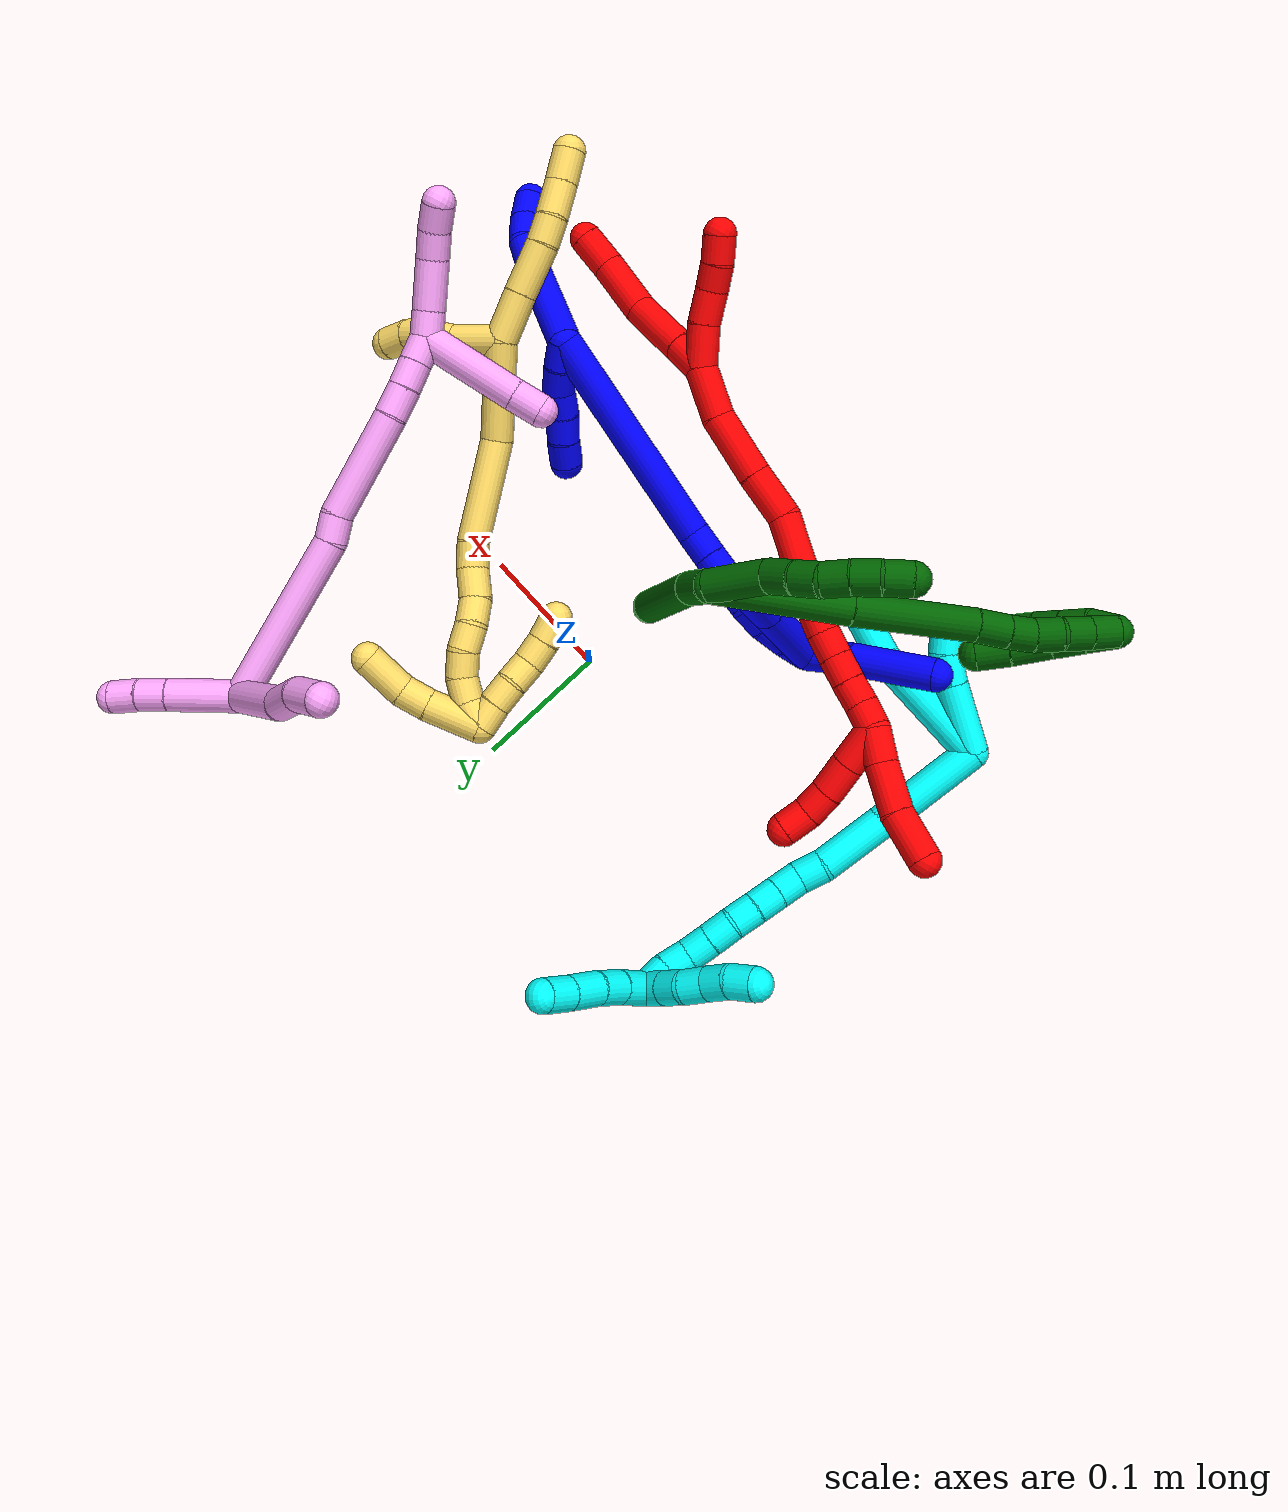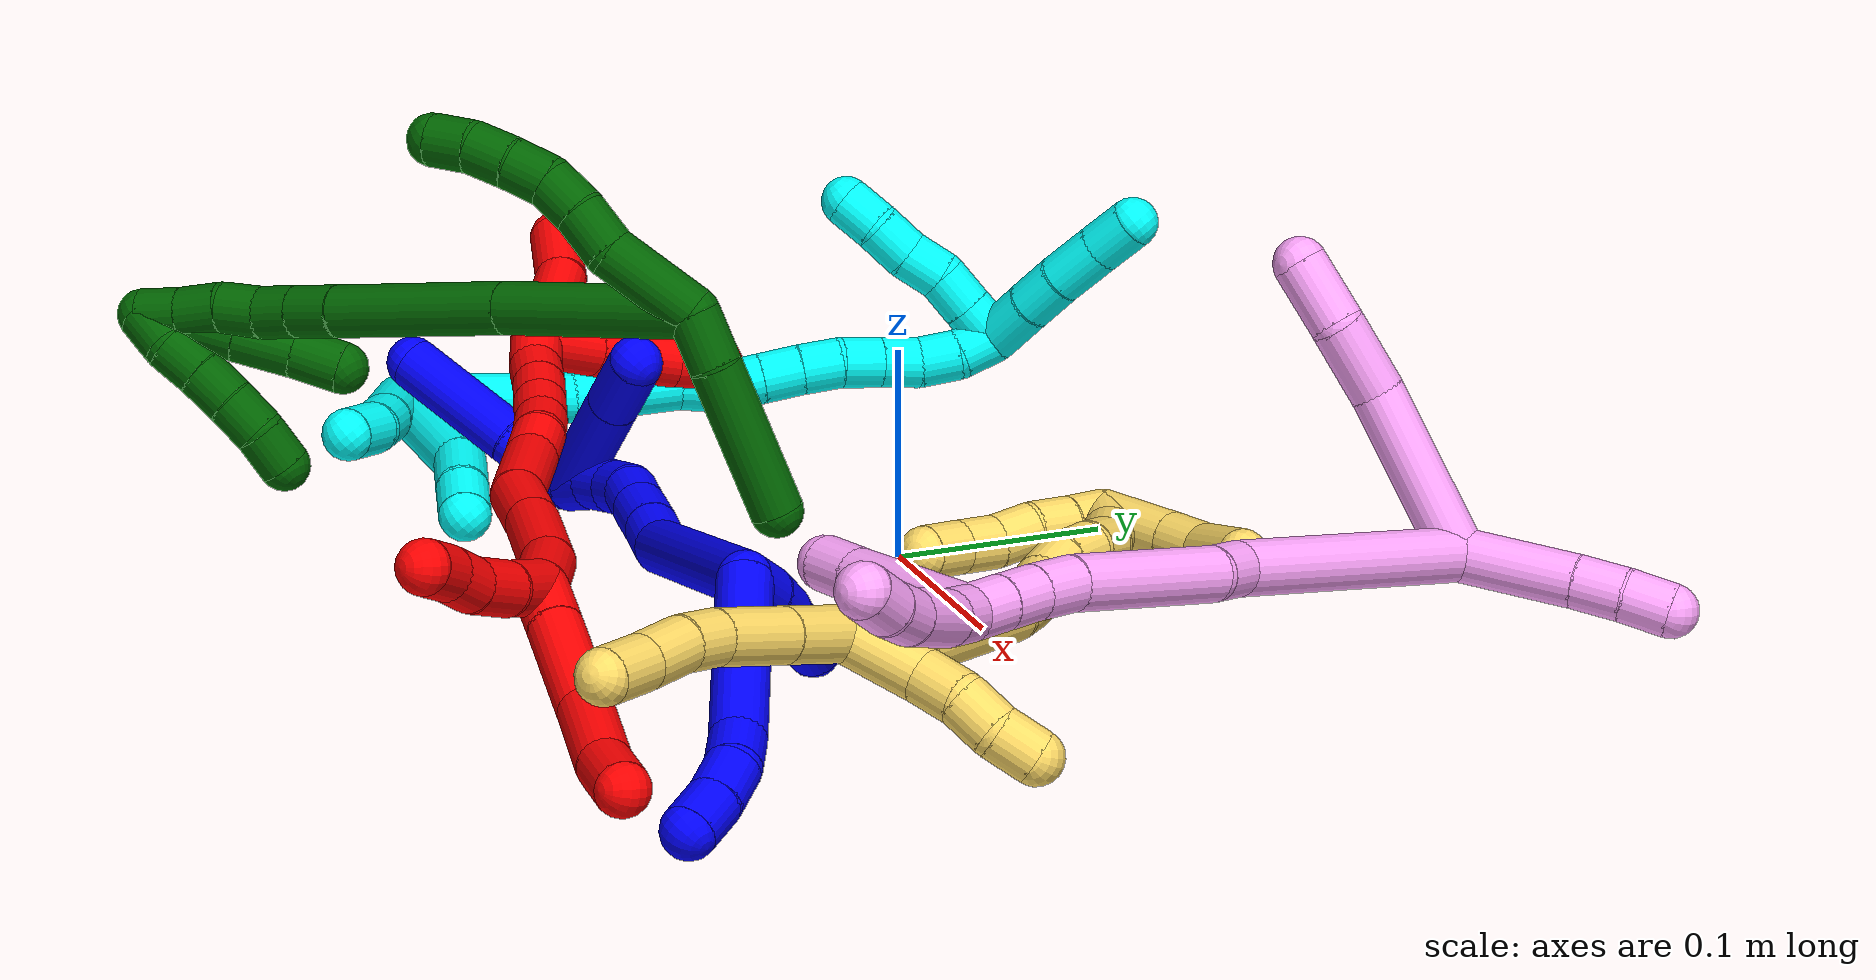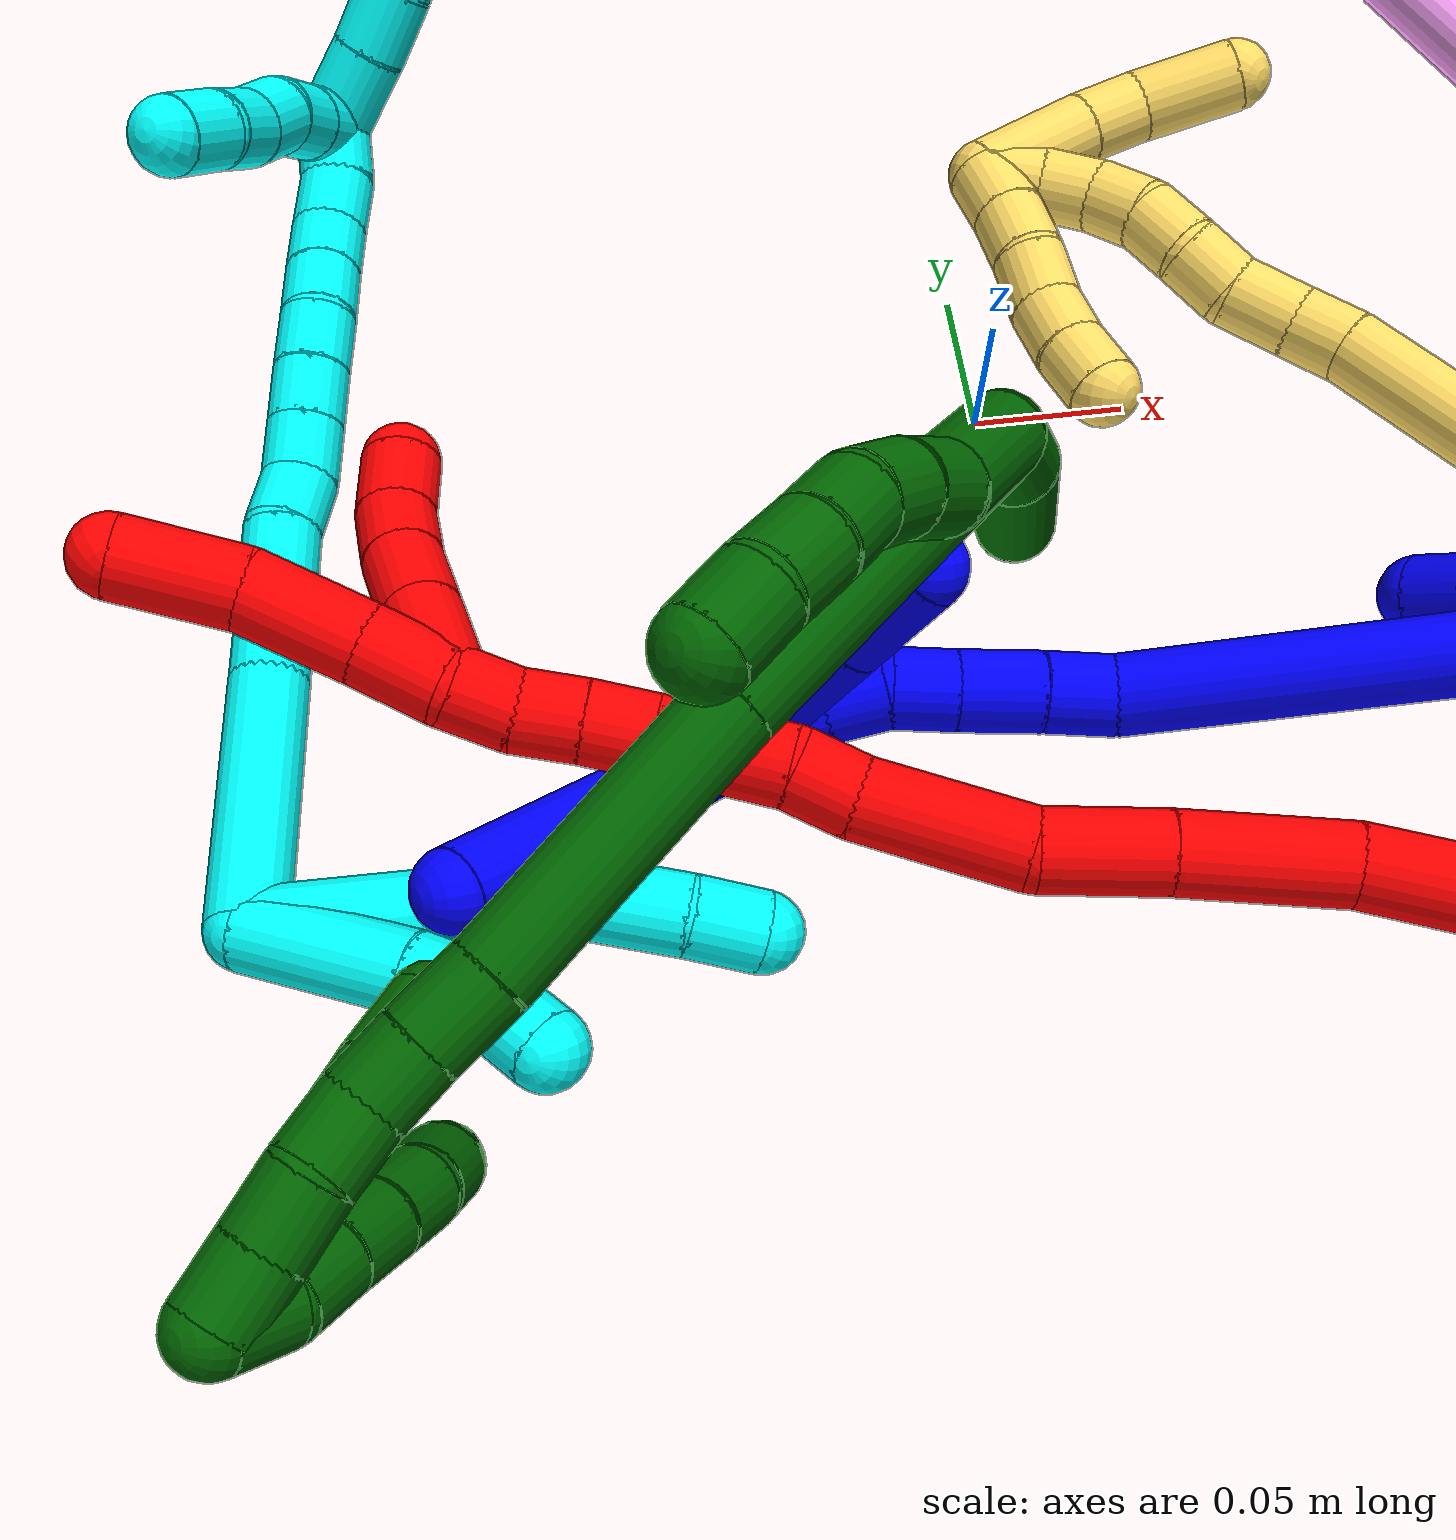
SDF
<sdf version="1.7">
 <world name="default">
  <plugin name="TubeGeneratorPlugin" filename="libtube_generator_plugin.so"/>
  <model name="photoneo_s_sensor">
   <static>1</static>
   <pose>0 0 2 1.57079 1.57079 3.14159</pose>
   <link name="link">
    <inertial><mass>0.1</mass></inertial>
    <sensor name="sensor" type="depth">
     <update_rate>30</update_rate>
     <camera>
      <horizontal_fov>1.22</horizontal_fov>
      <image><width>1920</width><height>1200</height><format>B8G8R8</format></image>
      <clip><near>0.1</near><far>4</far></clip>
      <depth_camera><output>points</output></depth_camera>
     </camera>
     <plugin name="camera_plugin" filename="libgazebo_ros_depth_camera.so">
      <baseline>0.2</baseline>
      <alwaysOn>1</alwaysOn>
      <updateRate>0.0</updateRate>
      <cameraName>camera_ir</cameraName>
      <imageTopicName>/camera/color/image_raw</imageTopicName>
      <cameraInfoTopicName>/camera/color/camera_info</cameraInfoTopicName>
      <depthImageTopicName>/camera/depth/image_raw</depthImageTopicName>
      <depthImageCameraInfoTopicName>/camera/depth/camera_info</depthImageCameraInfoTopicName>
      <pointCloudTopicName>/camera/depth/points</pointCloudTopicName>
      <frameName>fr_optical</frameName>
      <pointCloudCutoff>0.1</pointCloudCutoff>
      <pointCloudCutoffMax>2.0</pointCloudCutoffMax>
      <distortionK1>0</distortionK1>
      <distortionK2>0</distortionK2>
      <distortionK3>0</distortionK3>
      <distortionT1>0</distortionT1>
      <distortionT2>0</distortionT2>
      <CxPrime>0</CxPrime>
      <Cx>0</Cx>
      <Cy>0</Cy>
      <focalLength>0</focalLength>
      <hackBaseline>0</hackBaseline>
     </plugin>
    </sensor>
   </link>
  </model>
  <gravity>0 0 -9.8</gravity>
  <magnetic_field>6e-06 2.3e-05 -4.2e-05</magnetic_field>
  <atmosphere type="adiabatic"/>
  <physics name="default_physics" default="0" type="ode">
   <max_step_size>0.003</max_step_size>
   <real_time_factor>1</real_time_factor>
   <real_time_update_rate>1000</real_time_update_rate>
   <max_contacts>10000</max_contacts>
   <ode>
    <solver>
     <type>quick</type>
     <iters>100</iters>
     <sor>1.3</sor>
     <use_dynamic_moi_rescaling>0</use_dynamic_moi_rescaling>
    </solver>
    <constraints>
     <contact_max_correcting_vel>0</contact_max_correcting_vel>
     <contact_surface_layer>0.001</contact_surface_layer>
     <cfm>0</cfm>
     <erp>0.2</erp>
    </constraints>
   </ode>
  </physics>
  <scene><ambient>0.4 0.4 0.4 1</ambient><background>0.7 0.7 0.7 1</background><shadows>0</shadows></scene>
  <audio><device>default</device></audio>
  <spherical_coordinates>
   <surface_model>EARTH_WGS84</surface_model>
   <latitude_deg>0</latitude_deg>
   <longitude_deg>0</longitude_deg>
   <elevation>0</elevation>
   <heading_deg>0</heading_deg>
  </spherical_coordinates>
  <model name="bin">
   <static>1</static>
   <link name="bottom">
    <collision name="collision-bottom">
     <pose>0 0 -0.01 0 -0 0</pose>
     <geometry><box><size>0.8 0.6 0.02</size></box></geometry>
     <surface>
      <friction><ode><mu>100</mu><mu2>100</mu2></ode></friction>
      <contact><collide_bitmask>65535</collide_bitmask></contact>
     </surface>
    </collision>
   </link>
   <link name="west_wall">
    <collision name="collision-west_wall">
     <pose>-0.41 0 0.1 0 -0 0</pose>
     <geometry><box><size>0.02 0.6 0.2</size></box></geometry>
     <surface>
      <friction><ode><mu>100</mu><mu2>100</mu2></ode></friction>
      <contact><collide_bitmask>65535</collide_bitmask></contact>
     </surface>
    </collision>
   </link>
   <link name="east_wall">
    <collision name="collision-east_wall">
     <pose>0.41 0 0.1 0 -0 0</pose>
     <geometry><box><size>0.02 0.6 0.2</size></box></geometry>
     <surface>
      <friction><ode><mu>100</mu><mu2>100</mu2></ode></friction>
      <contact><collide_bitmask>65535</collide_bitmask></contact>
     </surface>
    </collision>
   </link>
   <link name="south_wall">
    <collision name="collision-south_wall">
     <pose>0 -0.31 0.1 0 -0 0</pose>
     <geometry><box><size>0.8 0.02 0.2</size></box></geometry>
     <surface>
      <friction><ode><mu>100</mu><mu2>100</mu2></ode></friction>
      <contact><collide_bitmask>65535</collide_bitmask></contact>
     </surface>
    </collision>
   </link>
   <link name="north_wall">
    <collision name="collision-north_wall">
     <pose>0 0.31 0.1 0 -0 0</pose>
     <geometry><box><size>0.8 0.02 0.2</size></box></geometry>
     <surface>
      <friction><ode><mu>100</mu><mu2>100</mu2></ode></friction>
      <contact><collide_bitmask>65535</collide_bitmask></contact>
     </surface>
    </collision>
   </link>
  </model>
  <model name="1">
   <static>0</static>
   <link name="1">
    <collision name="collision-cylinder-e_1_2_8">
     <pose>0.000642 0.02818 0.033808 -0.694857 0.014585 -0.005281</pose>
     <geometry><cylinder><radius>0.0125</radius><length>0.088034</length></cylinder></geometry>
     <surface>
      <friction><ode><mu>1.16</mu><mu2>1.16</mu2><slip1>0</slip1><slip2>0</slip2></ode></friction>
      <contact><ode><kp>1e+06</kp><kd>1</kd><max_vel>0</max_vel><min_depth>0.001</min_depth></ode></contact>
     </surface>
    </collision>
    <visual name="visual-cylinder-e_1_2_8">
     <pose>0.000642 0.02818 0.033808 -0.694857 0.014585 -0.005281</pose>
     <geometry><cylinder><radius>0.0125</radius><length>0.088034</length></cylinder></geometry>
     <material><ambient>0 0 1 1</ambient></material>
    </visual>
    <collision name="collision-cylinder-e_2_8_9">
     <pose>0.00405 0.063169 0.074747 -0.762281 0.273451 -0.110158</pose>
     <geometry><cylinder><radius>0.0125</radius><length>0.020482</length></cylinder></geometry>
     <surface>
      <friction><ode><mu>1.16</mu><mu2>1.16</mu2><slip1>0</slip1><slip2>0</slip2></ode></friction>
      <contact><ode><kp>1e+06</kp><kd>1</kd><max_vel>0</max_vel><min_depth>0.001</min_depth></ode></contact>
     </surface>
    </collision>
    <visual name="visual-cylinder-e_2_8_9">
     <pose>0.00405 0.063169 0.074747 -0.762281 0.273451 -0.110158</pose>
     <geometry><cylinder><radius>0.0125</radius><length>0.020482</length></cylinder></geometry>
     <material><ambient>0 0 1 1</ambient></material>
    </visual>
    <collision name="collision-cylinder-e_3_9_10">
     <pose>0.007851 0.07888 0.087102 -1.04013 0.099994 -0.057293</pose>
     <geometry><cylinder><radius>0.0125</radius><length>0.020744</length></cylinder></geometry>
     <surface>
      <friction><ode><mu>1.16</mu><mu2>1.16</mu2><slip1>0</slip1><slip2>0</slip2></ode></friction>
      <contact><ode><kp>1e+06</kp><kd>1</kd><max_vel>0</max_vel><min_depth>0.001</min_depth></ode></contact>
     </surface>
    </collision>
    <visual name="visual-cylinder-e_3_9_10">
     <pose>0.007851 0.07888 0.087102 -1.04013 0.099994 -0.057293</pose>
     <geometry><cylinder><radius>0.0125</radius><length>0.020744</length></cylinder></geometry>
     <material><ambient>0 0 1 1</ambient></material>
    </visual>
    <collision name="collision-cylinder-e_4_10_6">
     <pose>0.010407 0.097293 0.096165 -1.18717 0.147187 -0.099413</pose>
     <geometry><cylinder><radius>0.0125</radius><length>0.02074</length></cylinder></geometry>
     <surface>
      <friction><ode><mu>1.16</mu><mu2>1.16</mu2><slip1>0</slip1><slip2>0</slip2></ode></friction>
      <contact><ode><kp>1e+06</kp><kd>1</kd><max_vel>0</max_vel><min_depth>0.001</min_depth></ode></contact>
     </surface>
    </collision>
    <visual name="visual-cylinder-e_4_10_6">
     <pose>0.010407 0.097293 0.096165 -1.18717 0.147187 -0.099413</pose>
     <geometry><cylinder><radius>0.0125</radius><length>0.02074</length></cylinder></geometry>
     <material><ambient>0 0 1 1</ambient></material>
    </visual>
    <collision name="collision-cylinder-e_1_2_11">
     <pose>-0.008407 -0.005401 0.000381 1.50029 -0.998659 -0.94048</pose>
     <geometry><cylinder><radius>0.0125</radius><length>0.02</length></cylinder></geometry>
     <surface>
      <friction><ode><mu>1.16</mu><mu2>1.16</mu2><slip1>0</slip1><slip2>0</slip2></ode></friction>
      <contact><ode><kp>1e+06</kp><kd>1</kd><max_vel>0</max_vel><min_depth>0.001</min_depth></ode></contact>
     </surface>
    </collision>
    <visual name="visual-cylinder-e_1_2_11">
     <pose>-0.008407 -0.005401 0.000381 1.50029 -0.998659 -0.94048</pose>
     <geometry><cylinder><radius>0.0125</radius><length>0.02</length></cylinder></geometry>
     <material><ambient>0 0 1 1</ambient></material>
    </visual>
    <collision name="collision-cylinder-e_2_11_12">
     <pose>-0.025829 -0.015125 0.001004 1.51519 -1.12299 -1.07346</pose>
     <geometry><cylinder><radius>0.0125</radius><length>0.02</length></cylinder></geometry>
     <surface>
      <friction><ode><mu>1.16</mu><mu2>1.16</mu2><slip1>0</slip1><slip2>0</slip2></ode></friction>
      <contact><ode><kp>1e+06</kp><kd>1</kd><max_vel>0</max_vel><min_depth>0.001</min_depth></ode></contact>
     </surface>
    </collision>
    <visual name="visual-cylinder-e_2_11_12">
     <pose>-0.025829 -0.015125 0.001004 1.51519 -1.12299 -1.07346</pose>
     <geometry><cylinder><radius>0.0125</radius><length>0.02</length></cylinder></geometry>
     <material><ambient>0 0 1 1</ambient></material>
    </visual>
    <collision name="collision-cylinder-e_3_12_13">
     <pose>-0.043945 -0.023023 -0.000846 2.09995 -1.14385 -1.68573</pose>
     <geometry><cylinder><radius>0.0125</radius><length>0.02</length></cylinder></geometry>
     <surface>
      <friction><ode><mu>1.16</mu><mu2>1.16</mu2><slip1>0</slip1><slip2>0</slip2></ode></friction>
      <contact><ode><kp>1e+06</kp><kd>1</kd><max_vel>0</max_vel><min_depth>0.001</min_depth></ode></contact>
     </surface>
    </collision>
    <visual name="visual-cylinder-e_3_12_13">
     <pose>-0.043945 -0.023023 -0.000846 2.09995 -1.14385 -1.68573</pose>
     <geometry><cylinder><radius>0.0125</radius><length>0.02</length></cylinder></geometry>
     <material><ambient>0 0 1 1</ambient></material>
    </visual>
    <collision name="collision-cylinder-e_4_13_14">
     <pose>-0.061617 -0.031546 -0.004378 1.85433 -1.0293 -1.29182</pose>
     <geometry><cylinder><radius>0.0125</radius><length>0.02</length></cylinder></geometry>
     <surface>
      <friction><ode><mu>1.16</mu><mu2>1.16</mu2><slip1>0</slip1><slip2>0</slip2></ode></friction>
      <contact><ode><kp>1e+06</kp><kd>1</kd><max_vel>0</max_vel><min_depth>0.001</min_depth></ode></contact>
     </surface>
    </collision>
    <visual name="visual-cylinder-e_4_13_14">
     <pose>-0.061617 -0.031546 -0.004378 1.85433 -1.0293 -1.29182</pose>
     <geometry><cylinder><radius>0.0125</radius><length>0.02</length></cylinder></geometry>
     <material><ambient>0 0 1 1</ambient></material>
    </visual>
    <collision name="collision-cylinder-e_5_14_5">
     <pose>-0.079403 -0.040044 -0.007384 1.98575 -1.17237 -1.5888</pose>
     <geometry><cylinder><radius>0.0125</radius><length>0.02</length></cylinder></geometry>
     <surface>
      <friction><ode><mu>1.16</mu><mu2>1.16</mu2><slip1>0</slip1><slip2>0</slip2></ode></friction>
      <contact><ode><kp>1e+06</kp><kd>1</kd><max_vel>0</max_vel><min_depth>0.001</min_depth></ode></contact>
     </surface>
    </collision>
    <visual name="visual-cylinder-e_5_14_5">
     <pose>-0.079403 -0.040044 -0.007384 1.98575 -1.17237 -1.5888</pose>
     <geometry><cylinder><radius>0.0125</radius><length>0.02</length></cylinder></geometry>
     <material><ambient>0 0 1 1</ambient></material>
    </visual>
    <collision name="collision-cylinder-e_1_2_15">
     <pose>-0.059162 -0.021177 -0.058829 2.79605 -0.757774 -2.31537</pose>
     <geometry><cylinder><radius>0.0125</radius><length>0.172156</length></cylinder></geometry>
     <surface>
      <friction><ode><mu>1.16</mu><mu2>1.16</mu2><slip1>0</slip1><slip2>0</slip2></ode></friction>
      <contact><ode><kp>1e+06</kp><kd>1</kd><max_vel>0</max_vel><min_depth>0.001</min_depth></ode></contact>
     </surface>
    </collision>
    <visual name="visual-cylinder-e_1_2_15">
     <pose>-0.059162 -0.021177 -0.058829 2.79605 -0.757774 -2.31537</pose>
     <geometry><cylinder><radius>0.0125</radius><length>0.172156</length></cylinder></geometry>
     <material><ambient>0 0 1 1</ambient></material>
    </visual>
    <collision name="collision-cylinder-e_2_15_16">
     <pose>-0.122927 -0.046395 -0.126678 2.72054 -0.435867 -1.60644</pose>
     <geometry><cylinder><radius>0.0125</radius><length>0.021807</length></cylinder></geometry>
     <surface>
      <friction><ode><mu>1.16</mu><mu2>1.16</mu2><slip1>0</slip1><slip2>0</slip2></ode></friction>
      <contact><ode><kp>1e+06</kp><kd>1</kd><max_vel>0</max_vel><min_depth>0.001</min_depth></ode></contact>
     </surface>
    </collision>
    <visual name="visual-cylinder-e_2_15_16">
     <pose>-0.122927 -0.046395 -0.126678 2.72054 -0.435867 -1.60644</pose>
     <geometry><cylinder><radius>0.0125</radius><length>0.021807</length></cylinder></geometry>
     <material><ambient>0 0 1 1</ambient></material>
    </visual>
    <collision name="collision-cylinder-e_3_16_17">
     <pose>-0.133343 -0.054897 -0.146397 2.74638 -0.464814 -1.73732</pose>
     <geometry><cylinder><radius>0.0125</radius><length>0.025934</length></cylinder></geometry>
     <surface>
      <friction><ode><mu>1.16</mu><mu2>1.16</mu2><slip1>0</slip1><slip2>0</slip2></ode></friction>
      <contact><ode><kp>1e+06</kp><kd>1</kd><max_vel>0</max_vel><min_depth>0.001</min_depth></ode></contact>
     </surface>
    </collision>
    <visual name="visual-cylinder-e_3_16_17">
     <pose>-0.133343 -0.054897 -0.146397 2.74638 -0.464814 -1.73732</pose>
     <geometry><cylinder><radius>0.0125</radius><length>0.025934</length></cylinder></geometry>
     <material><ambient>0 0 1 1</ambient></material>
    </visual>
    <collision name="collision-cylinder-e_4_17_18">
     <pose>-0.143442 -0.062969 -0.165382 2.73089 -0.442771 -1.64822</pose>
     <geometry><cylinder><radius>0.0125</radius><length>0.020008</length></cylinder></geometry>
     <surface>
      <friction><ode><mu>1.16</mu><mu2>1.16</mu2><slip1>0</slip1><slip2>0</slip2></ode></friction>
      <contact><ode><kp>1e+06</kp><kd>1</kd><max_vel>0</max_vel><min_depth>0.001</min_depth></ode></contact>
     </surface>
    </collision>
    <visual name="visual-cylinder-e_4_17_18">
     <pose>-0.143442 -0.062969 -0.165382 2.73089 -0.442771 -1.64822</pose>
     <geometry><cylinder><radius>0.0125</radius><length>0.020008</length></cylinder></geometry>
     <material><ambient>0 0 1 1</ambient></material>
    </visual>
    <collision name="collision-cylinder-e_5_18_19">
     <pose>-0.154124 -0.06773 -0.181325 2.99218 -0.690449 -2.73122</pose>
     <geometry><cylinder><radius>0.0125</radius><length>0.020083</length></cylinder></geometry>
     <surface>
      <friction><ode><mu>1.16</mu><mu2>1.16</mu2><slip1>0</slip1><slip2>0</slip2></ode></friction>
      <contact><ode><kp>1e+06</kp><kd>1</kd><max_vel>0</max_vel><min_depth>0.001</min_depth></ode></contact>
     </surface>
    </collision>
    <visual name="visual-cylinder-e_5_18_19">
     <pose>-0.154124 -0.06773 -0.181325 2.99218 -0.690449 -2.73122</pose>
     <geometry><cylinder><radius>0.0125</radius><length>0.020083</length></cylinder></geometry>
     <material><ambient>0 0 1 1</ambient></material>
    </visual>
    <collision name="collision-cylinder-e_6_19_20">
     <pose>-0.1662 -0.068609 -0.19721 -3.10829 -0.60393 3.03477</pose>
     <geometry><cylinder><radius>0.0125</radius><length>0.020007</length></cylinder></geometry>
     <surface>
      <friction><ode><mu>1.16</mu><mu2>1.16</mu2><slip1>0</slip1><slip2>0</slip2></ode></friction>
      <contact><ode><kp>1e+06</kp><kd>1</kd><max_vel>0</max_vel><min_depth>0.001</min_depth></ode></contact>
     </surface>
    </collision>
    <visual name="visual-cylinder-e_6_19_20">
     <pose>-0.1662 -0.068609 -0.19721 -3.10829 -0.60393 3.03477</pose>
     <geometry><cylinder><radius>0.0125</radius><length>0.020007</length></cylinder></geometry>
     <material><ambient>0 0 1 1</ambient></material>
    </visual>
    <collision name="collision-cylinder-e_7_20_1">
     <pose>-0.178205 -0.066744 -0.213023 -2.93491 -0.684512 2.57506</pose>
     <geometry><cylinder><radius>0.0125</radius><length>0.020005</length></cylinder></geometry>
     <surface>
      <friction><ode><mu>1.16</mu><mu2>1.16</mu2><slip1>0</slip1><slip2>0</slip2></ode></friction>
      <contact><ode><kp>1e+06</kp><kd>1</kd><max_vel>0</max_vel><min_depth>0.001</min_depth></ode></contact>
     </surface>
    </collision>
    <visual name="visual-cylinder-e_7_20_1">
     <pose>-0.178205 -0.066744 -0.213023 -2.93491 -0.684512 2.57506</pose>
     <geometry><cylinder><radius>0.0125</radius><length>0.020005</length></cylinder></geometry>
     <material><ambient>0 0 1 1</ambient></material>
    </visual>
    <collision name="collision-cylinder-e_1_1_21">
     <pose>-0.181305 -0.061295 -0.23814 -2.92494 0.177706 -1.37264</pose>
     <geometry><cylinder><radius>0.0125</radius><length>0.036479</length></cylinder></geometry>
     <surface>
      <friction><ode><mu>1.16</mu><mu2>1.16</mu2><slip1>0</slip1><slip2>0</slip2></ode></friction>
      <contact><ode><kp>1e+06</kp><kd>1</kd><max_vel>0</max_vel><min_depth>0.001</min_depth></ode></contact>
     </surface>
    </collision>
    <visual name="visual-cylinder-e_1_1_21">
     <pose>-0.181305 -0.061295 -0.23814 -2.92494 0.177706 -1.37264</pose>
     <geometry><cylinder><radius>0.0125</radius><length>0.036479</length></cylinder></geometry>
     <material><ambient>0 0 1 1</ambient></material>
    </visual>
    <collision name="collision-cylinder-e_2_21_4">
     <pose>-0.174578 -0.051958 -0.28676 -2.96717 0.110499 -1.12802</pose>
     <geometry><cylinder><radius>0.0125</radius><length>0.063521</length></cylinder></geometry>
     <surface>
      <friction><ode><mu>1.16</mu><mu2>1.16</mu2><slip1>0</slip1><slip2>0</slip2></ode></friction>
      <contact><ode><kp>1e+06</kp><kd>1</kd><max_vel>0</max_vel><min_depth>0.001</min_depth></ode></contact>
     </surface>
    </collision>
    <visual name="visual-cylinder-e_2_21_4">
     <pose>-0.174578 -0.051958 -0.28676 -2.96717 0.110499 -1.12802</pose>
     <geometry><cylinder><radius>0.0125</radius><length>0.063521</length></cylinder></geometry>
     <material><ambient>0 0 1 1</ambient></material>
    </visual>
    <collision name="collision-cylinder-e_1_1_22">
     <pose>-0.152749 -0.07224 -0.21138 0.654836 1.21986 0.46607</pose>
     <geometry><cylinder><radius>0.0125</radius><length>0.067686</length></cylinder></geometry>
     <surface>
      <friction><ode><mu>1.16</mu><mu2>1.16</mu2><slip1>0</slip1><slip2>0</slip2></ode></friction>
      <contact><ode><kp>1e+06</kp><kd>1</kd><max_vel>0</max_vel><min_depth>0.001</min_depth></ode></contact>
     </surface>
    </collision>
    <visual name="visual-cylinder-e_1_1_22">
     <pose>-0.152749 -0.07224 -0.21138 0.654836 1.21986 0.46607</pose>
     <geometry><cylinder><radius>0.0125</radius><length>0.067686</length></cylinder></geometry>
     <material><ambient>0 0 1 1</ambient></material>
    </visual>
    <collision name="collision-cylinder-e_2_22_3">
     <pose>-0.105827 -0.082756 -0.197679 0.654259 1.2144 0.463038</pose>
     <geometry><cylinder><radius>0.0125</radius><length>0.032314</length></cylinder></geometry>
     <surface>
      <friction><ode><mu>1.16</mu><mu2>1.16</mu2><slip1>0</slip1><slip2>0</slip2></ode></friction>
      <contact><ode><kp>1e+06</kp><kd>1</kd><max_vel>0</max_vel><min_depth>0.001</min_depth></ode></contact>
     </surface>
    </collision>
    <visual name="visual-cylinder-e_2_22_3">
     <pose>-0.105827 -0.082756 -0.197679 0.654259 1.2144 0.463038</pose>
     <geometry><cylinder><radius>0.0125</radius><length>0.032314</length></cylinder></geometry>
     <material><ambient>0 0 1 1</ambient></material>
    </visual>
    <collision name="collision-sphere-3">
     <pose>-0.090685 -0.086187 -0.193206 0 -0 0</pose>
     <geometry><sphere><radius>0.0125</radius></sphere></geometry>
     <surface>
      <friction><ode><mu>1.16</mu><mu2>1.16</mu2><slip1>0</slip1><slip2>0</slip2></ode></friction>
      <contact><ode><kp>1e+06</kp><kd>1</kd><max_vel>0</max_vel><min_depth>0.001</min_depth></ode></contact>
     </surface>
    </collision>
    <visual name="visual-sphere-3">
     <pose>-0.090685 -0.086187 -0.193206 0 -0 0</pose>
     <geometry><sphere><radius>0.0125</radius></sphere></geometry>
     <material><ambient>0 0 1 1</ambient></material>
    </visual>
    <collision name="collision-sphere-22">
     <pose>-0.120969 -0.079325 -0.202152 0 -0 0</pose>
     <geometry><sphere><radius>0.0125</radius></sphere></geometry>
     <surface>
      <friction><ode><mu>1.16</mu><mu2>1.16</mu2><slip1>0</slip1><slip2>0</slip2></ode></friction>
      <contact><ode><kp>1e+06</kp><kd>1</kd><max_vel>0</max_vel><min_depth>0.001</min_depth></ode></contact>
     </surface>
    </collision>
    <visual name="visual-sphere-22">
     <pose>-0.120969 -0.079325 -0.202152 0 -0 0</pose>
     <geometry><sphere><radius>0.0125</radius></sphere></geometry>
     <material><ambient>0 0 1 1</ambient></material>
    </visual>
    <collision name="collision-sphere-4">
     <pose>-0.171076 -0.04648 -0.317848 0 -0 0</pose>
     <geometry><sphere><radius>0.0125</radius></sphere></geometry>
     <surface>
      <friction><ode><mu>1.16</mu><mu2>1.16</mu2><slip1>0</slip1><slip2>0</slip2></ode></friction>
      <contact><ode><kp>1e+06</kp><kd>1</kd><max_vel>0</max_vel><min_depth>0.001</min_depth></ode></contact>
     </surface>
    </collision>
    <visual name="visual-sphere-4">
     <pose>-0.171076 -0.04648 -0.317848 0 -0 0</pose>
     <geometry><sphere><radius>0.0125</radius></sphere></geometry>
     <material><ambient>0 0 1 1</ambient></material>
    </visual>
    <collision name="collision-sphere-21">
     <pose>-0.178081 -0.057436 -0.255673 0 -0 0</pose>
     <geometry><sphere><radius>0.0125</radius></sphere></geometry>
     <surface>
      <friction><ode><mu>1.16</mu><mu2>1.16</mu2><slip1>0</slip1><slip2>0</slip2></ode></friction>
      <contact><ode><kp>1e+06</kp><kd>1</kd><max_vel>0</max_vel><min_depth>0.001</min_depth></ode></contact>
     </surface>
    </collision>
    <visual name="visual-sphere-21">
     <pose>-0.178081 -0.057436 -0.255673 0 -0 0</pose>
     <geometry><sphere><radius>0.0125</radius></sphere></geometry>
     <material><ambient>0 0 1 1</ambient></material>
    </visual>
    <collision name="collision-sphere-1">
     <pose>-0.184529 -0.065154 -0.220607 0 -0 0</pose>
     <geometry><sphere><radius>0.0125</radius></sphere></geometry>
     <surface>
      <friction><ode><mu>1.16</mu><mu2>1.16</mu2><slip1>0</slip1><slip2>0</slip2></ode></friction>
      <contact><ode><kp>1e+06</kp><kd>1</kd><max_vel>0</max_vel><min_depth>0.001</min_depth></ode></contact>
     </surface>
    </collision>
    <visual name="visual-sphere-1">
     <pose>-0.184529 -0.065154 -0.220607 0 -0 0</pose>
     <geometry><sphere><radius>0.0125</radius></sphere></geometry>
     <material><ambient>0 0 1 1</ambient></material>
    </visual>
    <collision name="collision-sphere-11">
     <pose>-0.016815 -0.010802 0.000763 0 -0 0</pose>
     <geometry><sphere><radius>0.0125</radius></sphere></geometry>
     <surface>
      <friction><ode><mu>1.16</mu><mu2>1.16</mu2><slip1>0</slip1><slip2>0</slip2></ode></friction>
      <contact><ode><kp>1e+06</kp><kd>1</kd><max_vel>0</max_vel><min_depth>0.001</min_depth></ode></contact>
     </surface>
    </collision>
    <visual name="visual-sphere-11">
     <pose>-0.016815 -0.010802 0.000763 0 -0 0</pose>
     <geometry><sphere><radius>0.0125</radius></sphere></geometry>
     <material><ambient>0 0 1 1</ambient></material>
    </visual>
    <collision name="collision-sphere-6">
     <pose>0.011928 0.106805 0.100004 0 -0 0</pose>
     <geometry><sphere><radius>0.0125</radius></sphere></geometry>
     <surface>
      <friction><ode><mu>1.16</mu><mu2>1.16</mu2><slip1>0</slip1><slip2>0</slip2></ode></friction>
      <contact><ode><kp>1e+06</kp><kd>1</kd><max_vel>0</max_vel><min_depth>0.001</min_depth></ode></contact>
     </surface>
    </collision>
    <visual name="visual-sphere-6">
     <pose>0.011928 0.106805 0.100004 0 -0 0</pose>
     <geometry><sphere><radius>0.0125</radius></sphere></geometry>
     <material><ambient>0 0 1 1</ambient></material>
    </visual>
    <collision name="collision-sphere-10">
     <pose>0.008886 0.087781 0.092326 0 -0 0</pose>
     <geometry><sphere><radius>0.0125</radius></sphere></geometry>
     <surface>
      <friction><ode><mu>1.16</mu><mu2>1.16</mu2><slip1>0</slip1><slip2>0</slip2></ode></friction>
      <contact><ode><kp>1e+06</kp><kd>1</kd><max_vel>0</max_vel><min_depth>0.001</min_depth></ode></contact>
     </surface>
    </collision>
    <visual name="visual-sphere-10">
     <pose>0.008886 0.087781 0.092326 0 -0 0</pose>
     <geometry><sphere><radius>0.0125</radius></sphere></geometry>
     <material><ambient>0 0 1 1</ambient></material>
    </visual>
    <collision name="collision-sphere-9">
     <pose>0.006815 0.069979 0.081879 0 -0 0</pose>
     <geometry><sphere><radius>0.0125</radius></sphere></geometry>
     <surface>
      <friction><ode><mu>1.16</mu><mu2>1.16</mu2><slip1>0</slip1><slip2>0</slip2></ode></friction>
      <contact><ode><kp>1e+06</kp><kd>1</kd><max_vel>0</max_vel><min_depth>0.001</min_depth></ode></contact>
     </surface>
    </collision>
    <visual name="visual-sphere-9">
     <pose>0.006815 0.069979 0.081879 0 -0 0</pose>
     <geometry><sphere><radius>0.0125</radius></sphere></geometry>
     <material><ambient>0 0 1 1</ambient></material>
    </visual>
    <collision name="collision-sphere-2">
     <geometry><sphere><radius>0.0125</radius></sphere></geometry>
     <surface>
      <friction><ode><mu>1.16</mu><mu2>1.16</mu2><slip1>0</slip1><slip2>0</slip2></ode></friction>
      <contact><ode><kp>1e+06</kp><kd>1</kd><max_vel>0</max_vel><min_depth>0.001</min_depth></ode></contact>
     </surface>
    </collision>
    <visual name="visual-sphere-2">
     <geometry><sphere><radius>0.0125</radius></sphere></geometry>
     <material><ambient>0 0 1 1</ambient></material>
    </visual>
    <collision name="collision-sphere-19">
     <pose>-0.160519 -0.068883 -0.18898 0 -0 0</pose>
     <geometry><sphere><radius>0.0125</radius></sphere></geometry>
     <surface>
      <friction><ode><mu>1.16</mu><mu2>1.16</mu2><slip1>0</slip1><slip2>0</slip2></ode></friction>
      <contact><ode><kp>1e+06</kp><kd>1</kd><max_vel>0</max_vel><min_depth>0.001</min_depth></ode></contact>
     </surface>
    </collision>
    <visual name="visual-sphere-19">
     <pose>-0.160519 -0.068883 -0.18898 0 -0 0</pose>
     <geometry><sphere><radius>0.0125</radius></sphere></geometry>
     <material><ambient>0 0 1 1</ambient></material>
    </visual>
    <collision name="collision-sphere-8">
     <pose>0.001284 0.05636 0.067616 0 -0 0</pose>
     <geometry><sphere><radius>0.0125</radius></sphere></geometry>
     <surface>
      <friction><ode><mu>1.16</mu><mu2>1.16</mu2><slip1>0</slip1><slip2>0</slip2></ode></friction>
      <contact><ode><kp>1e+06</kp><kd>1</kd><max_vel>0</max_vel><min_depth>0.001</min_depth></ode></contact>
     </surface>
    </collision>
    <visual name="visual-sphere-8">
     <pose>0.001284 0.05636 0.067616 0 -0 0</pose>
     <geometry><sphere><radius>0.0125</radius></sphere></geometry>
     <material><ambient>0 0 1 1</ambient></material>
    </visual>
    <collision name="collision-sphere-12">
     <pose>-0.034843 -0.019448 0.001244 0 -0 0</pose>
     <geometry><sphere><radius>0.0125</radius></sphere></geometry>
     <surface>
      <friction><ode><mu>1.16</mu><mu2>1.16</mu2><slip1>0</slip1><slip2>0</slip2></ode></friction>
      <contact><ode><kp>1e+06</kp><kd>1</kd><max_vel>0</max_vel><min_depth>0.001</min_depth></ode></contact>
     </surface>
    </collision>
    <visual name="visual-sphere-12">
     <pose>-0.034843 -0.019448 0.001244 0 -0 0</pose>
     <geometry><sphere><radius>0.0125</radius></sphere></geometry>
     <material><ambient>0 0 1 1</ambient></material>
    </visual>
    <collision name="collision-sphere-13">
     <pose>-0.053048 -0.026597 -0.002937 0 -0 0</pose>
     <geometry><sphere><radius>0.0125</radius></sphere></geometry>
     <surface>
      <friction><ode><mu>1.16</mu><mu2>1.16</mu2><slip1>0</slip1><slip2>0</slip2></ode></friction>
      <contact><ode><kp>1e+06</kp><kd>1</kd><max_vel>0</max_vel><min_depth>0.001</min_depth></ode></contact>
     </surface>
    </collision>
    <visual name="visual-sphere-13">
     <pose>-0.053048 -0.026597 -0.002937 0 -0 0</pose>
     <geometry><sphere><radius>0.0125</radius></sphere></geometry>
     <material><ambient>0 0 1 1</ambient></material>
    </visual>
    <collision name="collision-sphere-14">
     <pose>-0.070186 -0.036494 -0.00582 0 -0 0</pose>
     <geometry><sphere><radius>0.0125</radius></sphere></geometry>
     <surface>
      <friction><ode><mu>1.16</mu><mu2>1.16</mu2><slip1>0</slip1><slip2>0</slip2></ode></friction>
      <contact><ode><kp>1e+06</kp><kd>1</kd><max_vel>0</max_vel><min_depth>0.001</min_depth></ode></contact>
     </surface>
    </collision>
    <visual name="visual-sphere-14">
     <pose>-0.070186 -0.036494 -0.00582 0 -0 0</pose>
     <geometry><sphere><radius>0.0125</radius></sphere></geometry>
     <material><ambient>0 0 1 1</ambient></material>
    </visual>
    <collision name="collision-sphere-5">
     <pose>-0.08862 -0.043595 -0.008948 0 -0 0</pose>
     <geometry><sphere><radius>0.0125</radius></sphere></geometry>
     <surface>
      <friction><ode><mu>1.16</mu><mu2>1.16</mu2><slip1>0</slip1><slip2>0</slip2></ode></friction>
      <contact><ode><kp>1e+06</kp><kd>1</kd><max_vel>0</max_vel><min_depth>0.001</min_depth></ode></contact>
     </surface>
    </collision>
    <visual name="visual-sphere-5">
     <pose>-0.08862 -0.043595 -0.008948 0 -0 0</pose>
     <geometry><sphere><radius>0.0125</radius></sphere></geometry>
     <material><ambient>0 0 1 1</ambient></material>
    </visual>
    <collision name="collision-sphere-15">
     <pose>-0.118324 -0.042355 -0.117657 0 -0 0</pose>
     <geometry><sphere><radius>0.0125</radius></sphere></geometry>
     <surface>
      <friction><ode><mu>1.16</mu><mu2>1.16</mu2><slip1>0</slip1><slip2>0</slip2></ode></friction>
      <contact><ode><kp>1e+06</kp><kd>1</kd><max_vel>0</max_vel><min_depth>0.001</min_depth></ode></contact>
     </surface>
    </collision>
    <visual name="visual-sphere-15">
     <pose>-0.118324 -0.042355 -0.117657 0 -0 0</pose>
     <geometry><sphere><radius>0.0125</radius></sphere></geometry>
     <material><ambient>0 0 1 1</ambient></material>
    </visual>
    <collision name="collision-sphere-16">
     <pose>-0.127531 -0.050435 -0.135699 0 -0 0</pose>
     <geometry><sphere><radius>0.0125</radius></sphere></geometry>
     <surface>
      <friction><ode><mu>1.16</mu><mu2>1.16</mu2><slip1>0</slip1><slip2>0</slip2></ode></friction>
      <contact><ode><kp>1e+06</kp><kd>1</kd><max_vel>0</max_vel><min_depth>0.001</min_depth></ode></contact>
     </surface>
    </collision>
    <visual name="visual-sphere-16">
     <pose>-0.127531 -0.050435 -0.135699 0 -0 0</pose>
     <geometry><sphere><radius>0.0125</radius></sphere></geometry>
     <material><ambient>0 0 1 1</ambient></material>
    </visual>
    <collision name="collision-sphere-17">
     <pose>-0.139156 -0.05936 -0.157094 0 -0 0</pose>
     <geometry><sphere><radius>0.0125</radius></sphere></geometry>
     <surface>
      <friction><ode><mu>1.16</mu><mu2>1.16</mu2><slip1>0</slip1><slip2>0</slip2></ode></friction>
      <contact><ode><kp>1e+06</kp><kd>1</kd><max_vel>0</max_vel><min_depth>0.001</min_depth></ode></contact>
     </surface>
    </collision>
    <visual name="visual-sphere-17">
     <pose>-0.139156 -0.05936 -0.157094 0 -0 0</pose>
     <geometry><sphere><radius>0.0125</radius></sphere></geometry>
     <material><ambient>0 0 1 1</ambient></material>
    </visual>
    <collision name="collision-sphere-18">
     <pose>-0.147728 -0.066578 -0.173669 0 -0 0</pose>
     <geometry><sphere><radius>0.0125</radius></sphere></geometry>
     <surface>
      <friction><ode><mu>1.16</mu><mu2>1.16</mu2><slip1>0</slip1><slip2>0</slip2></ode></friction>
      <contact><ode><kp>1e+06</kp><kd>1</kd><max_vel>0</max_vel><min_depth>0.001</min_depth></ode></contact>
     </surface>
    </collision>
    <visual name="visual-sphere-18">
     <pose>-0.147728 -0.066578 -0.173669 0 -0 0</pose>
     <geometry><sphere><radius>0.0125</radius></sphere></geometry>
     <material><ambient>0 0 1 1</ambient></material>
    </visual>
    <collision name="collision-sphere-20">
     <pose>-0.17188 -0.068334 -0.205439 0 -0 0</pose>
     <geometry><sphere><radius>0.0125</radius></sphere></geometry>
     <surface>
      <friction><ode><mu>1.16</mu><mu2>1.16</mu2><slip1>0</slip1><slip2>0</slip2></ode></friction>
      <contact><ode><kp>1e+06</kp><kd>1</kd><max_vel>0</max_vel><min_depth>0.001</min_depth></ode></contact>
     </surface>
    </collision>
    <visual name="visual-sphere-20">
     <pose>-0.17188 -0.068334 -0.205439 0 -0 0</pose>
     <geometry><sphere><radius>0.0125</radius></sphere></geometry>
     <material><ambient>0 0 1 1</ambient></material>
    </visual>
    <inertial>
     <pose>-0.086009 -0.025845 -0.095144 0 -0 0</pose>
     <mass>0.75</mass>
     <inertia>
      <ixx>-0.000402</ixx>
      <ixy>0</ixy>
      <ixz>0</ixz>
      <iyy>0.000169</iyy>
      <iyz>0</iyz>
      <izz>0.000327</izz>
     </inertia>
    </inertial>
   </link>
   <pose>0.181156 -0.142925 0.072046 -2.47162 -1.05894 -0.371353</pose>
  </model>
  <model name="2">
   <static>0</static>
   <link name="2">
    <collision name="collision-cylinder-e_1_2_8">
     <pose>0.0125 0.001582 -0.003201 -2.6826 1.29258 -2.54097</pose>
     <geometry><cylinder><radius>0.0125</radius><length>0.026001</length></cylinder></geometry>
     <surface>
      <friction><ode><mu>1.16</mu><mu2>1.16</mu2><slip1>0</slip1><slip2>0</slip2></ode></friction>
      <contact><ode><kp>1e+06</kp><kd>1</kd><max_vel>0</max_vel><min_depth>0.001</min_depth></ode></contact>
     </surface>
    </collision>
    <visual name="visual-cylinder-e_1_2_8">
     <pose>0.0125 0.001582 -0.003201 -2.6826 1.29258 -2.54097</pose>
     <geometry><cylinder><radius>0.0125</radius><length>0.026001</length></cylinder></geometry>
     <material><ambient>1 0 0 1</ambient></material>
    </visual>
    <collision name="collision-cylinder-e_2_8_9">
     <pose>0.049139 0.007112 -0.012097 -2.53534 1.29123 -2.35452</pose>
     <geometry><cylinder><radius>0.0125</radius><length>0.050227</length></cylinder></geometry>
     <surface>
      <friction><ode><mu>1.16</mu><mu2>1.16</mu2><slip1>0</slip1><slip2>0</slip2></ode></friction>
      <contact><ode><kp>1e+06</kp><kd>1</kd><max_vel>0</max_vel><min_depth>0.001</min_depth></ode></contact>
     </surface>
    </collision>
    <visual name="visual-cylinder-e_2_8_9">
     <pose>0.049139 0.007112 -0.012097 -2.53534 1.29123 -2.35452</pose>
     <geometry><cylinder><radius>0.0125</radius><length>0.050227</length></cylinder></geometry>
     <material><ambient>1 0 0 1</ambient></material>
    </visual>
    <collision name="collision-cylinder-e_3_9_10">
     <pose>0.094012 0.00978 -0.02642 2.9942 1.17259 2.92019</pose>
     <geometry><cylinder><radius>0.0125</radius><length>0.04499</length></cylinder></geometry>
     <surface>
      <friction><ode><mu>1.16</mu><mu2>1.16</mu2><slip1>0</slip1><slip2>0</slip2></ode></friction>
      <contact><ode><kp>1e+06</kp><kd>1</kd><max_vel>0</max_vel><min_depth>0.001</min_depth></ode></contact>
     </surface>
    </collision>
    <visual name="visual-cylinder-e_3_9_10">
     <pose>0.094012 0.00978 -0.02642 2.9942 1.17259 2.92019</pose>
     <geometry><cylinder><radius>0.0125</radius><length>0.04499</length></cylinder></geometry>
     <material><ambient>1 0 0 1</ambient></material>
    </visual>
    <collision name="collision-cylinder-e_4_10_6">
     <pose>0.12773 0.00486 -0.04008 2.51555 1.12463 2.19266</pose>
     <geometry><cylinder><radius>0.0125</radius><length>0.028783</length></cylinder></geometry>
     <surface>
      <friction><ode><mu>1.16</mu><mu2>1.16</mu2><slip1>0</slip1><slip2>0</slip2></ode></friction>
      <contact><ode><kp>1e+06</kp><kd>1</kd><max_vel>0</max_vel><min_depth>0.001</min_depth></ode></contact>
     </surface>
    </collision>
    <visual name="visual-cylinder-e_4_10_6">
     <pose>0.12773 0.00486 -0.04008 2.51555 1.12463 2.19266</pose>
     <geometry><cylinder><radius>0.0125</radius><length>0.028783</length></cylinder></geometry>
     <material><ambient>1 0 0 1</ambient></material>
    </visual>
    <collision name="collision-cylinder-e_1_2_11">
     <pose>0.006008 -0.004605 -0.01436 2.83127 0.379117 1.77364</pose>
     <geometry><cylinder><radius>0.0125</radius><length>0.032465</length></cylinder></geometry>
     <surface>
      <friction><ode><mu>1.16</mu><mu2>1.16</mu2><slip1>0</slip1><slip2>0</slip2></ode></friction>
      <contact><ode><kp>1e+06</kp><kd>1</kd><max_vel>0</max_vel><min_depth>0.001</min_depth></ode></contact>
     </surface>
    </collision>
    <visual name="visual-cylinder-e_1_2_11">
     <pose>0.006008 -0.004605 -0.01436 2.83127 0.379117 1.77364</pose>
     <geometry><cylinder><radius>0.0125</radius><length>0.032465</length></cylinder></geometry>
     <material><ambient>1 0 0 1</ambient></material>
    </visual>
    <collision name="collision-cylinder-e_2_11_12">
     <pose>0.014686 -0.012793 -0.041003 2.85779 0.205743 1.25149</pose>
     <geometry><cylinder><radius>0.0125</radius><length>0.026142</length></cylinder></geometry>
     <surface>
      <friction><ode><mu>1.16</mu><mu2>1.16</mu2><slip1>0</slip1><slip2>0</slip2></ode></friction>
      <contact><ode><kp>1e+06</kp><kd>1</kd><max_vel>0</max_vel><min_depth>0.001</min_depth></ode></contact>
     </surface>
    </collision>
    <visual name="visual-cylinder-e_2_11_12">
     <pose>0.014686 -0.012793 -0.041003 2.85779 0.205743 1.25149</pose>
     <geometry><cylinder><radius>0.0125</radius><length>0.026142</length></cylinder></geometry>
     <material><ambient>1 0 0 1</ambient></material>
    </visual>
    <collision name="collision-cylinder-e_3_12_13">
     <pose>0.018765 -0.021012 -0.062254 2.66445 0.138625 0.556121</pose>
     <geometry><cylinder><radius>0.0125</radius><length>0.020386</length></cylinder></geometry>
     <surface>
      <friction><ode><mu>1.16</mu><mu2>1.16</mu2><slip1>0</slip1><slip2>0</slip2></ode></friction>
      <contact><ode><kp>1e+06</kp><kd>1</kd><max_vel>0</max_vel><min_depth>0.001</min_depth></ode></contact>
     </surface>
    </collision>
    <visual name="visual-cylinder-e_3_12_13">
     <pose>0.018765 -0.021012 -0.062254 2.66445 0.138625 0.556121</pose>
     <geometry><cylinder><radius>0.0125</radius><length>0.020386</length></cylinder></geometry>
     <material><ambient>1 0 0 1</ambient></material>
    </visual>
    <collision name="collision-cylinder-e_4_13_5">
     <pose>0.023283 -0.029847 -0.080333 2.70969 0.300552 1.20827</pose>
     <geometry><cylinder><radius>0.0125</radius><length>0.021007</length></cylinder></geometry>
     <surface>
      <friction><ode><mu>1.16</mu><mu2>1.16</mu2><slip1>0</slip1><slip2>0</slip2></ode></friction>
      <contact><ode><kp>1e+06</kp><kd>1</kd><max_vel>0</max_vel><min_depth>0.001</min_depth></ode></contact>
     </surface>
    </collision>
    <visual name="visual-cylinder-e_4_13_5">
     <pose>0.023283 -0.029847 -0.080333 2.70969 0.300552 1.20827</pose>
     <geometry><cylinder><radius>0.0125</radius><length>0.021007</length></cylinder></geometry>
     <material><ambient>1 0 0 1</ambient></material>
    </visual>
    <collision name="collision-cylinder-e_1_2_14">
     <pose>-0.014431 0.004383 0.012816 -0.329553 -0.817055 0.143715</pose>
     <geometry><cylinder><radius>0.0125</radius><length>0.039583</length></cylinder></geometry>
     <surface>
      <friction><ode><mu>1.16</mu><mu2>1.16</mu2><slip1>0</slip1><slip2>0</slip2></ode></friction>
      <contact><ode><kp>1e+06</kp><kd>1</kd><max_vel>0</max_vel><min_depth>0.001</min_depth></ode></contact>
     </surface>
    </collision>
    <visual name="visual-cylinder-e_1_2_14">
     <pose>-0.014431 0.004383 0.012816 -0.329553 -0.817055 0.143715</pose>
     <geometry><cylinder><radius>0.0125</radius><length>0.039583</length></cylinder></geometry>
     <material><ambient>1 0 0 1</ambient></material>
    </visual>
    <collision name="collision-cylinder-e_2_14_15">
     <pose>-0.051049 0.014008 0.037277 -0.422931 -1.04853 0.247003</pose>
     <geometry><cylinder><radius>0.0125</radius><length>0.0512</length></cylinder></geometry>
     <surface>
      <friction><ode><mu>1.16</mu><mu2>1.16</mu2><slip1>0</slip1><slip2>0</slip2></ode></friction>
      <contact><ode><kp>1e+06</kp><kd>1</kd><max_vel>0</max_vel><min_depth>0.001</min_depth></ode></contact>
     </surface>
    </collision>
    <visual name="visual-cylinder-e_2_14_15">
     <pose>-0.051049 0.014008 0.037277 -0.422931 -1.04853 0.247003</pose>
     <geometry><cylinder><radius>0.0125</radius><length>0.0512</length></cylinder></geometry>
     <material><ambient>1 0 0 1</ambient></material>
    </visual>
    <collision name="collision-cylinder-e_3_15_16">
     <pose>-0.089954 0.023454 0.056639 -0.498834 -1.08687 0.305362</pose>
     <geometry><cylinder><radius>0.0125</radius><length>0.037775</length></cylinder></geometry>
     <surface>
      <friction><ode><mu>1.16</mu><mu2>1.16</mu2><slip1>0</slip1><slip2>0</slip2></ode></friction>
      <contact><ode><kp>1e+06</kp><kd>1</kd><max_vel>0</max_vel><min_depth>0.001</min_depth></ode></contact>
     </surface>
    </collision>
    <visual name="visual-cylinder-e_3_15_16">
     <pose>-0.089954 0.023454 0.056639 -0.498834 -1.08687 0.305362</pose>
     <geometry><cylinder><radius>0.0125</radius><length>0.037775</length></cylinder></geometry>
     <material><ambient>1 0 0 1</ambient></material>
    </visual>
    <collision name="collision-cylinder-e_4_16_17">
     <pose>-0.125578 0.031131 0.081275 -0.20248 -0.830511 0.089519</pose>
     <geometry><cylinder><radius>0.0125</radius><length>0.051214</length></cylinder></geometry>
     <surface>
      <friction><ode><mu>1.16</mu><mu2>1.16</mu2><slip1>0</slip1><slip2>0</slip2></ode></friction>
      <contact><ode><kp>1e+06</kp><kd>1</kd><max_vel>0</max_vel><min_depth>0.001</min_depth></ode></contact>
     </surface>
    </collision>
    <visual name="visual-cylinder-e_4_16_17">
     <pose>-0.125578 0.031131 0.081275 -0.20248 -0.830511 0.089519</pose>
     <geometry><cylinder><radius>0.0125</radius><length>0.051214</length></cylinder></geometry>
     <material><ambient>1 0 0 1</ambient></material>
    </visual>
    <collision name="collision-cylinder-e_5_17_18">
     <pose>-0.152021 0.033718 0.104753 0.134392 -0.850215 -0.060914</pose>
     <geometry><cylinder><radius>0.0125</radius><length>0.020063</length></cylinder></geometry>
     <surface>
      <friction><ode><mu>1.16</mu><mu2>1.16</mu2><slip1>0</slip1><slip2>0</slip2></ode></friction>
      <contact><ode><kp>1e+06</kp><kd>1</kd><max_vel>0</max_vel><min_depth>0.001</min_depth></ode></contact>
     </surface>
    </collision>
    <visual name="visual-cylinder-e_5_17_18">
     <pose>-0.152021 0.033718 0.104753 0.134392 -0.850215 -0.060914</pose>
     <geometry><cylinder><radius>0.0125</radius><length>0.020063</length></cylinder></geometry>
     <material><ambient>1 0 0 1</ambient></material>
    </visual>
    <collision name="collision-cylinder-e_6_18_19">
     <pose>-0.167455 0.034226 0.117389 -0.225642 -0.902474 0.109698</pose>
     <geometry><cylinder><radius>0.0125</radius><length>0.020122</length></cylinder></geometry>
     <surface>
      <friction><ode><mu>1.16</mu><mu2>1.16</mu2><slip1>0</slip1><slip2>0</slip2></ode></friction>
      <contact><ode><kp>1e+06</kp><kd>1</kd><max_vel>0</max_vel><min_depth>0.001</min_depth></ode></contact>
     </surface>
    </collision>
    <visual name="visual-cylinder-e_6_18_19">
     <pose>-0.167455 0.034226 0.117389 -0.225642 -0.902474 0.109698</pose>
     <geometry><cylinder><radius>0.0125</radius><length>0.020122</length></cylinder></geometry>
     <material><ambient>1 0 0 1</ambient></material>
    </visual>
    <collision name="collision-cylinder-e_7_19_20">
     <pose>-0.183828 0.03649 0.128733 -0.163667 -1.00873 0.090482</pose>
     <geometry><cylinder><radius>0.0125</radius><length>0.020035</length></cylinder></geometry>
     <surface>
      <friction><ode><mu>1.16</mu><mu2>1.16</mu2><slip1>0</slip1><slip2>0</slip2></ode></friction>
      <contact><ode><kp>1e+06</kp><kd>1</kd><max_vel>0</max_vel><min_depth>0.001</min_depth></ode></contact>
     </surface>
    </collision>
    <visual name="visual-cylinder-e_7_19_20">
     <pose>-0.183828 0.03649 0.128733 -0.163667 -1.00873 0.090482</pose>
     <geometry><cylinder><radius>0.0125</radius><length>0.020035</length></cylinder></geometry>
     <material><ambient>1 0 0 1</ambient></material>
    </visual>
    <collision name="collision-cylinder-e_8_20_21">
     <pose>-0.200748 0.038124 0.139306 -0.143026 -1.00513 0.078706</pose>
     <geometry><cylinder><radius>0.0125</radius><length>0.020004</length></cylinder></geometry>
     <surface>
      <friction><ode><mu>1.16</mu><mu2>1.16</mu2><slip1>0</slip1><slip2>0</slip2></ode></friction>
      <contact><ode><kp>1e+06</kp><kd>1</kd><max_vel>0</max_vel><min_depth>0.001</min_depth></ode></contact>
     </surface>
    </collision>
    <visual name="visual-cylinder-e_8_20_21">
     <pose>-0.200748 0.038124 0.139306 -0.143026 -1.00513 0.078706</pose>
     <geometry><cylinder><radius>0.0125</radius><length>0.020004</length></cylinder></geometry>
     <material><ambient>1 0 0 1</ambient></material>
    </visual>
    <collision name="collision-cylinder-e_9_21_22">
     <pose>-0.217913 0.039844 0.149415 -0.196346 -1.05914 0.115172</pose>
     <geometry><cylinder><radius>0.0125</radius><length>0.020004</length></cylinder></geometry>
     <surface>
      <friction><ode><mu>1.16</mu><mu2>1.16</mu2><slip1>0</slip1><slip2>0</slip2></ode></friction>
      <contact><ode><kp>1e+06</kp><kd>1</kd><max_vel>0</max_vel><min_depth>0.001</min_depth></ode></contact>
     </surface>
    </collision>
    <visual name="visual-cylinder-e_9_21_22">
     <pose>-0.217913 0.039844 0.149415 -0.196346 -1.05914 0.115172</pose>
     <geometry><cylinder><radius>0.0125</radius><length>0.020004</length></cylinder></geometry>
     <material><ambient>1 0 0 1</ambient></material>
    </visual>
    <collision name="collision-cylinder-e_10_22_1">
     <pose>-0.235151 0.039206 0.159212 0.308798 -1.01904 -0.173483</pose>
     <geometry><cylinder><radius>0.0125</radius><length>0.02</length></cylinder></geometry>
     <surface>
      <friction><ode><mu>1.16</mu><mu2>1.16</mu2><slip1>0</slip1><slip2>0</slip2></ode></friction>
      <contact><ode><kp>1e+06</kp><kd>1</kd><max_vel>0</max_vel><min_depth>0.001</min_depth></ode></contact>
     </surface>
    </collision>
    <visual name="visual-cylinder-e_10_22_1">
     <pose>-0.235151 0.039206 0.159212 0.308798 -1.01904 -0.173483</pose>
     <geometry><cylinder><radius>0.0125</radius><length>0.02</length></cylinder></geometry>
     <material><ambient>1 0 0 1</ambient></material>
    </visual>
    <collision name="collision-cylinder-e_1_1_23">
     <pose>-0.252769 0.037152 0.173389 0.050214 -0.780328 -0.020654</pose>
     <geometry><cylinder><radius>0.0125</radius><length>0.025874</length></cylinder></geometry>
     <surface>
      <friction><ode><mu>1.16</mu><mu2>1.16</mu2><slip1>0</slip1><slip2>0</slip2></ode></friction>
      <contact><ode><kp>1e+06</kp><kd>1</kd><max_vel>0</max_vel><min_depth>0.001</min_depth></ode></contact>
     </surface>
    </collision>
    <visual name="visual-cylinder-e_1_1_23">
     <pose>-0.252769 0.037152 0.173389 0.050214 -0.780328 -0.020654</pose>
     <geometry><cylinder><radius>0.0125</radius><length>0.025874</length></cylinder></geometry>
     <material><ambient>1 0 0 1</ambient></material>
    </visual>
    <collision name="collision-cylinder-e_2_23_24">
     <pose>-0.275938 0.034931 0.194357 0.14819 -0.86802 -0.068782</pose>
     <geometry><cylinder><radius>0.0125</radius><length>0.036874</length></cylinder></geometry>
     <surface>
      <friction><ode><mu>1.16</mu><mu2>1.16</mu2><slip1>0</slip1><slip2>0</slip2></ode></friction>
      <contact><ode><kp>1e+06</kp><kd>1</kd><max_vel>0</max_vel><min_depth>0.001</min_depth></ode></contact>
     </surface>
    </collision>
    <visual name="visual-cylinder-e_2_23_24">
     <pose>-0.275938 0.034931 0.194357 0.14819 -0.86802 -0.068782</pose>
     <geometry><cylinder><radius>0.0125</radius><length>0.036874</length></cylinder></geometry>
     <material><ambient>1 0 0 1</ambient></material>
    </visual>
    <collision name="collision-cylinder-e_3_24_4">
     <pose>-0.306616 0.03214 0.214509 0.12261 -1.10116 -0.075329</pose>
     <geometry><cylinder><radius>0.0125</radius><length>0.037252</length></cylinder></geometry>
     <surface>
      <friction><ode><mu>1.16</mu><mu2>1.16</mu2><slip1>0</slip1><slip2>0</slip2></ode></friction>
      <contact><ode><kp>1e+06</kp><kd>1</kd><max_vel>0</max_vel><min_depth>0.001</min_depth></ode></contact>
     </surface>
    </collision>
    <visual name="visual-cylinder-e_3_24_4">
     <pose>-0.306616 0.03214 0.214509 0.12261 -1.10116 -0.075329</pose>
     <geometry><cylinder><radius>0.0125</radius><length>0.037252</length></cylinder></geometry>
     <material><ambient>1 0 0 1</ambient></material>
    </visual>
    <collision name="collision-cylinder-e_1_1_25">
     <pose>-0.241757 0.039345 0.179951 -0.109566 0.120042 -0.006591</pose>
     <geometry><cylinder><radius>0.0125</radius><length>0.031909</length></cylinder></geometry>
     <surface>
      <friction><ode><mu>1.16</mu><mu2>1.16</mu2><slip1>0</slip1><slip2>0</slip2></ode></friction>
      <contact><ode><kp>1e+06</kp><kd>1</kd><max_vel>0</max_vel><min_depth>0.001</min_depth></ode></contact>
     </surface>
    </collision>
    <visual name="visual-cylinder-e_1_1_25">
     <pose>-0.241757 0.039345 0.179951 -0.109566 0.120042 -0.006591</pose>
     <geometry><cylinder><radius>0.0125</radius><length>0.031909</length></cylinder></geometry>
     <material><ambient>1 0 0 1</ambient></material>
    </visual>
    <collision name="collision-cylinder-e_2_25_26">
     <pose>-0.238334 0.042425 0.208513 -0.104748 0.116778 -0.006129</pose>
     <geometry><cylinder><radius>0.0125</radius><length>0.025952</length></cylinder></geometry>
     <surface>
      <friction><ode><mu>1.16</mu><mu2>1.16</mu2><slip1>0</slip1><slip2>0</slip2></ode></friction>
      <contact><ode><kp>1e+06</kp><kd>1</kd><max_vel>0</max_vel><min_depth>0.001</min_depth></ode></contact>
     </surface>
    </collision>
    <visual name="visual-cylinder-e_2_25_26">
     <pose>-0.238334 0.042425 0.208513 -0.104748 0.116778 -0.006129</pose>
     <geometry><cylinder><radius>0.0125</radius><length>0.025952</length></cylinder></geometry>
     <material><ambient>1 0 0 1</ambient></material>
    </visual>
    <collision name="collision-cylinder-e_3_26_27">
     <pose>-0.234605 0.044026 0.231418 -0.025194 0.216267 -0.002735</pose>
     <geometry><cylinder><radius>0.0125</radius><length>0.020663</length></cylinder></geometry>
     <surface>
      <friction><ode><mu>1.16</mu><mu2>1.16</mu2><slip1>0</slip1><slip2>0</slip2></ode></friction>
      <contact><ode><kp>1e+06</kp><kd>1</kd><max_vel>0</max_vel><min_depth>0.001</min_depth></ode></contact>
     </surface>
    </collision>
    <visual name="visual-cylinder-e_3_26_27">
     <pose>-0.234605 0.044026 0.231418 -0.025194 0.216267 -0.002735</pose>
     <geometry><cylinder><radius>0.0125</radius><length>0.020663</length></cylinder></geometry>
     <material><ambient>1 0 0 1</ambient></material>
    </visual>
    <collision name="collision-cylinder-e_4_27_3">
     <pose>-0.228538 0.042328 0.251337 0.196077 0.3667 0.036472</pose>
     <geometry><cylinder><radius>0.0125</radius><length>0.021476</length></cylinder></geometry>
     <surface>
      <friction><ode><mu>1.16</mu><mu2>1.16</mu2><slip1>0</slip1><slip2>0</slip2></ode></friction>
      <contact><ode><kp>1e+06</kp><kd>1</kd><max_vel>0</max_vel><min_depth>0.001</min_depth></ode></contact>
     </surface>
    </collision>
    <visual name="visual-cylinder-e_4_27_3">
     <pose>-0.228538 0.042328 0.251337 0.196077 0.3667 0.036472</pose>
     <geometry><cylinder><radius>0.0125</radius><length>0.021476</length></cylinder></geometry>
     <material><ambient>1 0 0 1</ambient></material>
    </visual>
    <collision name="collision-sphere-3">
     <pose>-0.224688 0.040375 0.261169 0 -0 0</pose>
     <geometry><sphere><radius>0.0125</radius></sphere></geometry>
     <surface>
      <friction><ode><mu>1.16</mu><mu2>1.16</mu2><slip1>0</slip1><slip2>0</slip2></ode></friction>
      <contact><ode><kp>1e+06</kp><kd>1</kd><max_vel>0</max_vel><min_depth>0.001</min_depth></ode></contact>
     </surface>
    </collision>
    <visual name="visual-sphere-3">
     <pose>-0.224688 0.040375 0.261169 0 -0 0</pose>
     <geometry><sphere><radius>0.0125</radius></sphere></geometry>
     <material><ambient>1 0 0 1</ambient></material>
    </visual>
    <collision name="collision-sphere-27">
     <pose>-0.232388 0.04428 0.241505 0 -0 0</pose>
     <geometry><sphere><radius>0.0125</radius></sphere></geometry>
     <surface>
      <friction><ode><mu>1.16</mu><mu2>1.16</mu2><slip1>0</slip1><slip2>0</slip2></ode></friction>
      <contact><ode><kp>1e+06</kp><kd>1</kd><max_vel>0</max_vel><min_depth>0.001</min_depth></ode></contact>
     </surface>
    </collision>
    <visual name="visual-sphere-27">
     <pose>-0.232388 0.04428 0.241505 0 -0 0</pose>
     <geometry><sphere><radius>0.0125</radius></sphere></geometry>
     <material><ambient>1 0 0 1</ambient></material>
    </visual>
    <collision name="collision-sphere-26">
     <pose>-0.236822 0.043772 0.22133 0 -0 0</pose>
     <geometry><sphere><radius>0.0125</radius></sphere></geometry>
     <surface>
      <friction><ode><mu>1.16</mu><mu2>1.16</mu2><slip1>0</slip1><slip2>0</slip2></ode></friction>
      <contact><ode><kp>1e+06</kp><kd>1</kd><max_vel>0</max_vel><min_depth>0.001</min_depth></ode></contact>
     </surface>
    </collision>
    <visual name="visual-sphere-26">
     <pose>-0.236822 0.043772 0.22133 0 -0 0</pose>
     <geometry><sphere><radius>0.0125</radius></sphere></geometry>
     <material><ambient>1 0 0 1</ambient></material>
    </visual>
    <collision name="collision-sphere-25">
     <pose>-0.239846 0.041077 0.195696 0 -0 0</pose>
     <geometry><sphere><radius>0.0125</radius></sphere></geometry>
     <surface>
      <friction><ode><mu>1.16</mu><mu2>1.16</mu2><slip1>0</slip1><slip2>0</slip2></ode></friction>
      <contact><ode><kp>1e+06</kp><kd>1</kd><max_vel>0</max_vel><min_depth>0.001</min_depth></ode></contact>
     </surface>
    </collision>
    <visual name="visual-sphere-25">
     <pose>-0.239846 0.041077 0.195696 0 -0 0</pose>
     <geometry><sphere><radius>0.0125</radius></sphere></geometry>
     <material><ambient>1 0 0 1</ambient></material>
    </visual>
    <collision name="collision-sphere-4">
     <pose>-0.323225 0.031109 0.222876 0 -0 0</pose>
     <geometry><sphere><radius>0.0125</radius></sphere></geometry>
     <surface>
      <friction><ode><mu>1.16</mu><mu2>1.16</mu2><slip1>0</slip1><slip2>0</slip2></ode></friction>
      <contact><ode><kp>1e+06</kp><kd>1</kd><max_vel>0</max_vel><min_depth>0.001</min_depth></ode></contact>
     </surface>
    </collision>
    <visual name="visual-sphere-4">
     <pose>-0.323225 0.031109 0.222876 0 -0 0</pose>
     <geometry><sphere><radius>0.0125</radius></sphere></geometry>
     <material><ambient>1 0 0 1</ambient></material>
    </visual>
    <collision name="collision-sphere-24">
     <pose>-0.290007 0.033171 0.206143 0 -0 0</pose>
     <geometry><sphere><radius>0.0125</radius></sphere></geometry>
     <surface>
      <friction><ode><mu>1.16</mu><mu2>1.16</mu2><slip1>0</slip1><slip2>0</slip2></ode></friction>
      <contact><ode><kp>1e+06</kp><kd>1</kd><max_vel>0</max_vel><min_depth>0.001</min_depth></ode></contact>
     </surface>
    </collision>
    <visual name="visual-sphere-24">
     <pose>-0.290007 0.033171 0.206143 0 -0 0</pose>
     <geometry><sphere><radius>0.0125</radius></sphere></geometry>
     <material><ambient>1 0 0 1</ambient></material>
    </visual>
    <collision name="collision-sphere-23">
     <pose>-0.26187 0.03669 0.182572 0 -0 0</pose>
     <geometry><sphere><radius>0.0125</radius></sphere></geometry>
     <surface>
      <friction><ode><mu>1.16</mu><mu2>1.16</mu2><slip1>0</slip1><slip2>0</slip2></ode></friction>
      <contact><ode><kp>1e+06</kp><kd>1</kd><max_vel>0</max_vel><min_depth>0.001</min_depth></ode></contact>
     </surface>
    </collision>
    <visual name="visual-sphere-23">
     <pose>-0.26187 0.03669 0.182572 0 -0 0</pose>
     <geometry><sphere><radius>0.0125</radius></sphere></geometry>
     <material><ambient>1 0 0 1</ambient></material>
    </visual>
    <collision name="collision-sphere-1">
     <pose>-0.243667 0.037613 0.164206 0 -0 0</pose>
     <geometry><sphere><radius>0.0125</radius></sphere></geometry>
     <surface>
      <friction><ode><mu>1.16</mu><mu2>1.16</mu2><slip1>0</slip1><slip2>0</slip2></ode></friction>
      <contact><ode><kp>1e+06</kp><kd>1</kd><max_vel>0</max_vel><min_depth>0.001</min_depth></ode></contact>
     </surface>
    </collision>
    <visual name="visual-sphere-1">
     <pose>-0.243667 0.037613 0.164206 0 -0 0</pose>
     <geometry><sphere><radius>0.0125</radius></sphere></geometry>
     <material><ambient>1 0 0 1</ambient></material>
    </visual>
    <collision name="collision-sphere-22">
     <pose>-0.226635 0.040799 0.154218 0 -0 0</pose>
     <geometry><sphere><radius>0.0125</radius></sphere></geometry>
     <surface>
      <friction><ode><mu>1.16</mu><mu2>1.16</mu2><slip1>0</slip1><slip2>0</slip2></ode></friction>
      <contact><ode><kp>1e+06</kp><kd>1</kd><max_vel>0</max_vel><min_depth>0.001</min_depth></ode></contact>
     </surface>
    </collision>
    <visual name="visual-sphere-22">
     <pose>-0.226635 0.040799 0.154218 0 -0 0</pose>
     <geometry><sphere><radius>0.0125</radius></sphere></geometry>
     <material><ambient>1 0 0 1</ambient></material>
    </visual>
    <collision name="collision-sphere-21">
     <pose>-0.209192 0.038888 0.144612 0 -0 0</pose>
     <geometry><sphere><radius>0.0125</radius></sphere></geometry>
     <surface>
      <friction><ode><mu>1.16</mu><mu2>1.16</mu2><slip1>0</slip1><slip2>0</slip2></ode></friction>
      <contact><ode><kp>1e+06</kp><kd>1</kd><max_vel>0</max_vel><min_depth>0.001</min_depth></ode></contact>
     </surface>
    </collision>
    <visual name="visual-sphere-21">
     <pose>-0.209192 0.038888 0.144612 0 -0 0</pose>
     <geometry><sphere><radius>0.0125</radius></sphere></geometry>
     <material><ambient>1 0 0 1</ambient></material>
    </visual>
    <collision name="collision-sphere-11">
     <pose>0.012015 -0.00921 -0.02872 0 -0 0</pose>
     <geometry><sphere><radius>0.0125</radius></sphere></geometry>
     <surface>
      <friction><ode><mu>1.16</mu><mu2>1.16</mu2><slip1>0</slip1><slip2>0</slip2></ode></friction>
      <contact><ode><kp>1e+06</kp><kd>1</kd><max_vel>0</max_vel><min_depth>0.001</min_depth></ode></contact>
     </surface>
    </collision>
    <visual name="visual-sphere-11">
     <pose>0.012015 -0.00921 -0.02872 0 -0 0</pose>
     <geometry><sphere><radius>0.0125</radius></sphere></geometry>
     <material><ambient>1 0 0 1</ambient></material>
    </visual>
    <collision name="collision-sphere-6">
     <pose>0.140712 0.001221 -0.045112 0 -0 0</pose>
     <geometry><sphere><radius>0.0125</radius></sphere></geometry>
     <surface>
      <friction><ode><mu>1.16</mu><mu2>1.16</mu2><slip1>0</slip1><slip2>0</slip2></ode></friction>
      <contact><ode><kp>1e+06</kp><kd>1</kd><max_vel>0</max_vel><min_depth>0.001</min_depth></ode></contact>
     </surface>
    </collision>
    <visual name="visual-sphere-6">
     <pose>0.140712 0.001221 -0.045112 0 -0 0</pose>
     <geometry><sphere><radius>0.0125</radius></sphere></geometry>
     <material><ambient>1 0 0 1</ambient></material>
    </visual>
    <collision name="collision-sphere-10">
     <pose>0.114747 0.008499 -0.035048 0 -0 0</pose>
     <geometry><sphere><radius>0.0125</radius></sphere></geometry>
     <surface>
      <friction><ode><mu>1.16</mu><mu2>1.16</mu2><slip1>0</slip1><slip2>0</slip2></ode></friction>
      <contact><ode><kp>1e+06</kp><kd>1</kd><max_vel>0</max_vel><min_depth>0.001</min_depth></ode></contact>
     </surface>
    </collision>
    <visual name="visual-sphere-10">
     <pose>0.114747 0.008499 -0.035048 0 -0 0</pose>
     <geometry><sphere><radius>0.0125</radius></sphere></geometry>
     <material><ambient>1 0 0 1</ambient></material>
    </visual>
    <collision name="collision-sphere-9">
     <pose>0.073277 0.011061 -0.017791 0 -0 0</pose>
     <geometry><sphere><radius>0.0125</radius></sphere></geometry>
     <surface>
      <friction><ode><mu>1.16</mu><mu2>1.16</mu2><slip1>0</slip1><slip2>0</slip2></ode></friction>
      <contact><ode><kp>1e+06</kp><kd>1</kd><max_vel>0</max_vel><min_depth>0.001</min_depth></ode></contact>
     </surface>
    </collision>
    <visual name="visual-sphere-9">
     <pose>0.073277 0.011061 -0.017791 0 -0 0</pose>
     <geometry><sphere><radius>0.0125</radius></sphere></geometry>
     <material><ambient>1 0 0 1</ambient></material>
    </visual>
    <collision name="collision-sphere-2">
     <geometry><sphere><radius>0.0125</radius></sphere></geometry>
     <surface>
      <friction><ode><mu>1.16</mu><mu2>1.16</mu2><slip1>0</slip1><slip2>0</slip2></ode></friction>
      <contact><ode><kp>1e+06</kp><kd>1</kd><max_vel>0</max_vel><min_depth>0.001</min_depth></ode></contact>
     </surface>
    </collision>
    <visual name="visual-sphere-2">
     <geometry><sphere><radius>0.0125</radius></sphere></geometry>
     <material><ambient>1 0 0 1</ambient></material>
    </visual>
    <collision name="collision-sphere-19">
     <pose>-0.175352 0.03562 0.123465 0 -0 0</pose>
     <geometry><sphere><radius>0.0125</radius></sphere></geometry>
     <surface>
      <friction><ode><mu>1.16</mu><mu2>1.16</mu2><slip1>0</slip1><slip2>0</slip2></ode></friction>
      <contact><ode><kp>1e+06</kp><kd>1</kd><max_vel>0</max_vel><min_depth>0.001</min_depth></ode></contact>
     </surface>
    </collision>
    <visual name="visual-sphere-19">
     <pose>-0.175352 0.03562 0.123465 0 -0 0</pose>
     <geometry><sphere><radius>0.0125</radius></sphere></geometry>
     <material><ambient>1 0 0 1</ambient></material>
    </visual>
    <collision name="collision-sphere-8">
     <pose>0.025001 0.003164 -0.006402 0 -0 0</pose>
     <geometry><sphere><radius>0.0125</radius></sphere></geometry>
     <surface>
      <friction><ode><mu>1.16</mu><mu2>1.16</mu2><slip1>0</slip1><slip2>0</slip2></ode></friction>
      <contact><ode><kp>1e+06</kp><kd>1</kd><max_vel>0</max_vel><min_depth>0.001</min_depth></ode></contact>
     </surface>
    </collision>
    <visual name="visual-sphere-8">
     <pose>0.025001 0.003164 -0.006402 0 -0 0</pose>
     <geometry><sphere><radius>0.0125</radius></sphere></geometry>
     <material><ambient>1 0 0 1</ambient></material>
    </visual>
    <collision name="collision-sphere-12">
     <pose>0.017356 -0.016376 -0.053287 0 -0 0</pose>
     <geometry><sphere><radius>0.0125</radius></sphere></geometry>
     <surface>
      <friction><ode><mu>1.16</mu><mu2>1.16</mu2><slip1>0</slip1><slip2>0</slip2></ode></friction>
      <contact><ode><kp>1e+06</kp><kd>1</kd><max_vel>0</max_vel><min_depth>0.001</min_depth></ode></contact>
     </surface>
    </collision>
    <visual name="visual-sphere-12">
     <pose>0.017356 -0.016376 -0.053287 0 -0 0</pose>
     <geometry><sphere><radius>0.0125</radius></sphere></geometry>
     <material><ambient>1 0 0 1</ambient></material>
    </visual>
    <collision name="collision-sphere-13">
     <pose>0.020173 -0.025648 -0.071222 0 -0 0</pose>
     <geometry><sphere><radius>0.0125</radius></sphere></geometry>
     <surface>
      <friction><ode><mu>1.16</mu><mu2>1.16</mu2><slip1>0</slip1><slip2>0</slip2></ode></friction>
      <contact><ode><kp>1e+06</kp><kd>1</kd><max_vel>0</max_vel><min_depth>0.001</min_depth></ode></contact>
     </surface>
    </collision>
    <visual name="visual-sphere-13">
     <pose>0.020173 -0.025648 -0.071222 0 -0 0</pose>
     <geometry><sphere><radius>0.0125</radius></sphere></geometry>
     <material><ambient>1 0 0 1</ambient></material>
    </visual>
    <collision name="collision-sphere-5">
     <pose>0.026392 -0.034047 -0.089444 0 -0 0</pose>
     <geometry><sphere><radius>0.0125</radius></sphere></geometry>
     <surface>
      <friction><ode><mu>1.16</mu><mu2>1.16</mu2><slip1>0</slip1><slip2>0</slip2></ode></friction>
      <contact><ode><kp>1e+06</kp><kd>1</kd><max_vel>0</max_vel><min_depth>0.001</min_depth></ode></contact>
     </surface>
    </collision>
    <visual name="visual-sphere-5">
     <pose>0.026392 -0.034047 -0.089444 0 -0 0</pose>
     <geometry><sphere><radius>0.0125</radius></sphere></geometry>
     <material><ambient>1 0 0 1</ambient></material>
    </visual>
    <collision name="collision-sphere-14">
     <pose>-0.028862 0.008767 0.025632 0 -0 0</pose>
     <geometry><sphere><radius>0.0125</radius></sphere></geometry>
     <surface>
      <friction><ode><mu>1.16</mu><mu2>1.16</mu2><slip1>0</slip1><slip2>0</slip2></ode></friction>
      <contact><ode><kp>1e+06</kp><kd>1</kd><max_vel>0</max_vel><min_depth>0.001</min_depth></ode></contact>
     </surface>
    </collision>
    <visual name="visual-sphere-14">
     <pose>-0.028862 0.008767 0.025632 0 -0 0</pose>
     <geometry><sphere><radius>0.0125</radius></sphere></geometry>
     <material><ambient>1 0 0 1</ambient></material>
    </visual>
    <collision name="collision-sphere-15">
     <pose>-0.073236 0.01925 0.048922 0 -0 0</pose>
     <geometry><sphere><radius>0.0125</radius></sphere></geometry>
     <surface>
      <friction><ode><mu>1.16</mu><mu2>1.16</mu2><slip1>0</slip1><slip2>0</slip2></ode></friction>
      <contact><ode><kp>1e+06</kp><kd>1</kd><max_vel>0</max_vel><min_depth>0.001</min_depth></ode></contact>
     </surface>
    </collision>
    <visual name="visual-sphere-15">
     <pose>-0.073236 0.01925 0.048922 0 -0 0</pose>
     <geometry><sphere><radius>0.0125</radius></sphere></geometry>
     <material><ambient>1 0 0 1</ambient></material>
    </visual>
    <collision name="collision-sphere-16">
     <pose>-0.106673 0.027658 0.064356 0 -0 0</pose>
     <geometry><sphere><radius>0.0125</radius></sphere></geometry>
     <surface>
      <friction><ode><mu>1.16</mu><mu2>1.16</mu2><slip1>0</slip1><slip2>0</slip2></ode></friction>
      <contact><ode><kp>1e+06</kp><kd>1</kd><max_vel>0</max_vel><min_depth>0.001</min_depth></ode></contact>
     </surface>
    </collision>
    <visual name="visual-sphere-16">
     <pose>-0.106673 0.027658 0.064356 0 -0 0</pose>
     <geometry><sphere><radius>0.0125</radius></sphere></geometry>
     <material><ambient>1 0 0 1</ambient></material>
    </visual>
    <collision name="collision-sphere-17">
     <pose>-0.144483 0.034604 0.098194 0 -0 0</pose>
     <geometry><sphere><radius>0.0125</radius></sphere></geometry>
     <surface>
      <friction><ode><mu>1.16</mu><mu2>1.16</mu2><slip1>0</slip1><slip2>0</slip2></ode></friction>
      <contact><ode><kp>1e+06</kp><kd>1</kd><max_vel>0</max_vel><min_depth>0.001</min_depth></ode></contact>
     </surface>
    </collision>
    <visual name="visual-sphere-17">
     <pose>-0.144483 0.034604 0.098194 0 -0 0</pose>
     <geometry><sphere><radius>0.0125</radius></sphere></geometry>
     <material><ambient>1 0 0 1</ambient></material>
    </visual>
    <collision name="collision-sphere-18">
     <pose>-0.159559 0.032831 0.111312 0 -0 0</pose>
     <geometry><sphere><radius>0.0125</radius></sphere></geometry>
     <surface>
      <friction><ode><mu>1.16</mu><mu2>1.16</mu2><slip1>0</slip1><slip2>0</slip2></ode></friction>
      <contact><ode><kp>1e+06</kp><kd>1</kd><max_vel>0</max_vel><min_depth>0.001</min_depth></ode></contact>
     </surface>
    </collision>
    <visual name="visual-sphere-18">
     <pose>-0.159559 0.032831 0.111312 0 -0 0</pose>
     <geometry><sphere><radius>0.0125</radius></sphere></geometry>
     <material><ambient>1 0 0 1</ambient></material>
    </visual>
    <collision name="collision-sphere-20">
     <pose>-0.192304 0.03736 0.134 0 -0 0</pose>
     <geometry><sphere><radius>0.0125</radius></sphere></geometry>
     <surface>
      <friction><ode><mu>1.16</mu><mu2>1.16</mu2><slip1>0</slip1><slip2>0</slip2></ode></friction>
      <contact><ode><kp>1e+06</kp><kd>1</kd><max_vel>0</max_vel><min_depth>0.001</min_depth></ode></contact>
     </surface>
    </collision>
    <visual name="visual-sphere-20">
     <pose>-0.192304 0.03736 0.134 0 -0 0</pose>
     <geometry><sphere><radius>0.0125</radius></sphere></geometry>
     <material><ambient>1 0 0 1</ambient></material>
    </visual>
    <inertial>
     <pose>-0.101117 0.019829 0.077559 0 -0 0</pose>
     <mass>0.75</mass>
     <inertia><ixx>3.9e-05</ixx><ixy>0</ixy><ixz>0</ixz><iyy>0.000107</iyy><iyz>0</iyz><izz>2.9e-05</izz></inertia>
    </inertial>
   </link>
   <pose>0.101951 -0.20806 0.049549 -1.75762 0.323631 0.22456</pose>
  </model>
  <model name="3">
   <static>0</static>
   <link name="3">
    <collision name="collision-cylinder-e_1_2_8">
     <pose>0.043577 0.004981 -0.019403 -2.89033 1.1399 -2.75246</pose>
     <geometry><cylinder><radius>0.0125</radius><length>0.095922</length></cylinder></geometry>
     <surface>
      <friction><ode><mu>1.16</mu><mu2>1.16</mu2><slip1>0</slip1><slip2>0</slip2></ode></friction>
      <contact><ode><kp>1e+06</kp><kd>1</kd><max_vel>0</max_vel><min_depth>0.001</min_depth></ode></contact>
     </surface>
    </collision>
    <visual name="visual-cylinder-e_1_2_8">
     <pose>0.043577 0.004981 -0.019403 -2.89033 1.1399 -2.75246</pose>
     <geometry><cylinder><radius>0.0125</radius><length>0.095922</length></cylinder></geometry>
     <material><ambient>0.003922 1 0.996078 1</ambient></material>
    </visual>
    <collision name="collision-cylinder-e_2_8_9">
     <pose>0.102071 0.007515 -0.043701 2.67805 1.21924 2.48978</pose>
     <geometry><cylinder><radius>0.0125</radius><length>0.031779</length></cylinder></geometry>
     <surface>
      <friction><ode><mu>1.16</mu><mu2>1.16</mu2><slip1>0</slip1><slip2>0</slip2></ode></friction>
      <contact><ode><kp>1e+06</kp><kd>1</kd><max_vel>0</max_vel><min_depth>0.001</min_depth></ode></contact>
     </surface>
    </collision>
    <visual name="visual-cylinder-e_2_8_9">
     <pose>0.102071 0.007515 -0.043701 2.67805 1.21924 2.48978</pose>
     <geometry><cylinder><radius>0.0125</radius><length>0.031779</length></cylinder></geometry>
     <material><ambient>0.003922 1 0.996078 1</ambient></material>
    </visual>
    <collision name="collision-cylinder-e_3_9_6">
     <pose>0.126772 0.002509 -0.053292 2.64262 1.07051 2.32994</pose>
     <geometry><cylinder><radius>0.0125</radius><length>0.022299</length></cylinder></geometry>
     <surface>
      <friction><ode><mu>1.16</mu><mu2>1.16</mu2><slip1>0</slip1><slip2>0</slip2></ode></friction>
      <contact><ode><kp>1e+06</kp><kd>1</kd><max_vel>0</max_vel><min_depth>0.001</min_depth></ode></contact>
     </surface>
    </collision>
    <visual name="visual-cylinder-e_3_9_6">
     <pose>0.126772 0.002509 -0.053292 2.64262 1.07051 2.32994</pose>
     <geometry><cylinder><radius>0.0125</radius><length>0.022299</length></cylinder></geometry>
     <material><ambient>0.003922 1 0.996078 1</ambient></material>
    </visual>
    <collision name="collision-cylinder-e_1_2_10">
     <pose>0.0265 -0.003639 -0.000748 1.77363 1.43152 1.63526</pose>
     <geometry><cylinder><radius>0.0125</radius><length>0.053519</length></cylinder></geometry>
     <surface>
      <friction><ode><mu>1.16</mu><mu2>1.16</mu2><slip1>0</slip1><slip2>0</slip2></ode></friction>
      <contact><ode><kp>1e+06</kp><kd>1</kd><max_vel>0</max_vel><min_depth>0.001</min_depth></ode></contact>
     </surface>
    </collision>
    <visual name="visual-cylinder-e_1_2_10">
     <pose>0.0265 -0.003639 -0.000748 1.77363 1.43152 1.63526</pose>
     <geometry><cylinder><radius>0.0125</radius><length>0.053519</length></cylinder></geometry>
     <material><ambient>0.003922 1 0.996078 1</ambient></material>
    </visual>
    <collision name="collision-cylinder-e_2_10_11">
     <pose>0.064219 -0.009768 -0.001286 1.48623 1.35159 1.2698</pose>
     <geometry><cylinder><radius>0.0125</radius><length>0.022987</length></cylinder></geometry>
     <surface>
      <friction><ode><mu>1.16</mu><mu2>1.16</mu2><slip1>0</slip1><slip2>0</slip2></ode></friction>
      <contact><ode><kp>1e+06</kp><kd>1</kd><max_vel>0</max_vel><min_depth>0.001</min_depth></ode></contact>
     </surface>
    </collision>
    <visual name="visual-cylinder-e_2_10_11">
     <pose>0.064219 -0.009768 -0.001286 1.48623 1.35159 1.2698</pose>
     <geometry><cylinder><radius>0.0125</radius><length>0.022987</length></cylinder></geometry>
     <material><ambient>0.003922 1 0.996078 1</ambient></material>
    </visual>
    <collision name="collision-cylinder-e_3_11_5">
     <pose>0.085776 -0.017138 0.00163 1.06472 1.07594 0.676015</pose>
     <geometry><cylinder><radius>0.0125</radius><length>0.023494</length></cylinder></geometry>
     <surface>
      <friction><ode><mu>1.16</mu><mu2>1.16</mu2><slip1>0</slip1><slip2>0</slip2></ode></friction>
      <contact><ode><kp>1e+06</kp><kd>1</kd><max_vel>0</max_vel><min_depth>0.001</min_depth></ode></contact>
     </surface>
    </collision>
    <visual name="visual-cylinder-e_3_11_5">
     <pose>0.085776 -0.017138 0.00163 1.06472 1.07594 0.676015</pose>
     <geometry><cylinder><radius>0.0125</radius><length>0.023494</length></cylinder></geometry>
     <material><ambient>0.003922 1 0.996078 1</ambient></material>
    </visual>
    <collision name="collision-cylinder-e_1_2_12">
     <pose>-0.011441 0.031924 -0.025971 -2.25373 -0.271159 0.558668</pose>
     <geometry><cylinder><radius>0.0125</radius><length>0.085429</length></cylinder></geometry>
     <surface>
      <friction><ode><mu>1.16</mu><mu2>1.16</mu2><slip1>0</slip1><slip2>0</slip2></ode></friction>
      <contact><ode><kp>1e+06</kp><kd>1</kd><max_vel>0</max_vel><min_depth>0.001</min_depth></ode></contact>
     </surface>
    </collision>
    <visual name="visual-cylinder-e_1_2_12">
     <pose>-0.011441 0.031924 -0.025971 -2.25373 -0.271159 0.558668</pose>
     <geometry><cylinder><radius>0.0125</radius><length>0.085429</length></cylinder></geometry>
     <material><ambient>0.003922 1 0.996078 1</ambient></material>
    </visual>
    <collision name="collision-cylinder-e_2_12_13">
     <pose>-0.02857 0.08603 -0.06599 -2.13537 -0.213327 0.384298</pose>
     <geometry><cylinder><radius>0.0125</radius><length>0.05373</length></cylinder></geometry>
     <surface>
      <friction><ode><mu>1.16</mu><mu2>1.16</mu2><slip1>0</slip1><slip2>0</slip2></ode></friction>
      <contact><ode><kp>1e+06</kp><kd>1</kd><max_vel>0</max_vel><min_depth>0.001</min_depth></ode></contact>
     </surface>
    </collision>
    <visual name="visual-cylinder-e_2_12_13">
     <pose>-0.02857 0.08603 -0.06599 -2.13537 -0.213327 0.384298</pose>
     <geometry><cylinder><radius>0.0125</radius><length>0.05373</length></cylinder></geometry>
     <material><ambient>0.003922 1 0.996078 1</ambient></material>
    </visual>
    <collision name="collision-cylinder-e_3_13_14">
     <pose>-0.035227 0.115662 -0.087139 -2.33209 -0.093942 0.21857</pose>
     <geometry><cylinder><radius>0.0125</radius><length>0.020674</length></cylinder></geometry>
     <surface>
      <friction><ode><mu>1.16</mu><mu2>1.16</mu2><slip1>0</slip1><slip2>0</slip2></ode></friction>
      <contact><ode><kp>1e+06</kp><kd>1</kd><max_vel>0</max_vel><min_depth>0.001</min_depth></ode></contact>
     </surface>
    </collision>
    <visual name="visual-cylinder-e_3_13_14">
     <pose>-0.035227 0.115662 -0.087139 -2.33209 -0.093942 0.21857</pose>
     <geometry><cylinder><radius>0.0125</radius><length>0.020674</length></cylinder></geometry>
     <material><ambient>0.003922 1 0.996078 1</ambient></material>
    </visual>
    <collision name="collision-cylinder-e_4_14_15">
     <pose>-0.037512 0.132016 -0.098682 -2.03368 -0.131445 0.21201</pose>
     <geometry><cylinder><radius>0.0125</radius><length>0.020075</length></cylinder></geometry>
     <surface>
      <friction><ode><mu>1.16</mu><mu2>1.16</mu2><slip1>0</slip1><slip2>0</slip2></ode></friction>
      <contact><ode><kp>1e+06</kp><kd>1</kd><max_vel>0</max_vel><min_depth>0.001</min_depth></ode></contact>
     </surface>
    </collision>
    <visual name="visual-cylinder-e_4_14_15">
     <pose>-0.037512 0.132016 -0.098682 -2.03368 -0.131445 0.21201</pose>
     <geometry><cylinder><radius>0.0125</radius><length>0.020075</length></cylinder></geometry>
     <material><ambient>0.003922 1 0.996078 1</ambient></material>
    </visual>
    <collision name="collision-cylinder-e_5_15_16">
     <pose>-0.040174 0.149808 -0.107563 -2.03391 -0.134635 0.217186</pose>
     <geometry><cylinder><radius>0.0125</radius><length>0.020049</length></cylinder></geometry>
     <surface>
      <friction><ode><mu>1.16</mu><mu2>1.16</mu2><slip1>0</slip1><slip2>0</slip2></ode></friction>
      <contact><ode><kp>1e+06</kp><kd>1</kd><max_vel>0</max_vel><min_depth>0.001</min_depth></ode></contact>
     </surface>
    </collision>
    <visual name="visual-cylinder-e_5_15_16">
     <pose>-0.040174 0.149808 -0.107563 -2.03391 -0.134635 0.217186</pose>
     <geometry><cylinder><radius>0.0125</radius><length>0.020049</length></cylinder></geometry>
     <material><ambient>0.003922 1 0.996078 1</ambient></material>
    </visual>
    <collision name="collision-cylinder-e_6_16_17">
     <pose>-0.042936 0.167344 -0.116853 -2.08209 -0.141949 0.241633</pose>
     <geometry><cylinder><radius>0.0125</radius><length>0.020037</length></cylinder></geometry>
     <surface>
      <friction><ode><mu>1.16</mu><mu2>1.16</mu2><slip1>0</slip1><slip2>0</slip2></ode></friction>
      <contact><ode><kp>1e+06</kp><kd>1</kd><max_vel>0</max_vel><min_depth>0.001</min_depth></ode></contact>
     </surface>
    </collision>
    <visual name="visual-cylinder-e_6_16_17">
     <pose>-0.042936 0.167344 -0.116853 -2.08209 -0.141949 0.241633</pose>
     <geometry><cylinder><radius>0.0125</radius><length>0.020037</length></cylinder></geometry>
     <material><ambient>0.003922 1 0.996078 1</ambient></material>
    </visual>
    <collision name="collision-cylinder-e_7_17_18">
     <pose>-0.046854 0.183509 -0.127811 -2.25304 -0.252743 0.521641</pose>
     <geometry><cylinder><radius>0.0125</radius><length>0.02</length></cylinder></geometry>
     <surface>
      <friction><ode><mu>1.16</mu><mu2>1.16</mu2><slip1>0</slip1><slip2>0</slip2></ode></friction>
      <contact><ode><kp>1e+06</kp><kd>1</kd><max_vel>0</max_vel><min_depth>0.001</min_depth></ode></contact>
     </surface>
    </collision>
    <visual name="visual-cylinder-e_7_17_18">
     <pose>-0.046854 0.183509 -0.127811 -2.25304 -0.252743 0.521641</pose>
     <geometry><cylinder><radius>0.0125</radius><length>0.02</length></cylinder></geometry>
     <material><ambient>0.003922 1 0.996078 1</ambient></material>
    </visual>
    <collision name="collision-cylinder-e_8_18_19">
     <pose>-0.05172 0.198463 -0.140168 -2.26963 -0.238716 0.503907</pose>
     <geometry><cylinder><radius>0.0125</radius><length>0.020002</length></cylinder></geometry>
     <surface>
      <friction><ode><mu>1.16</mu><mu2>1.16</mu2><slip1>0</slip1><slip2>0</slip2></ode></friction>
      <contact><ode><kp>1e+06</kp><kd>1</kd><max_vel>0</max_vel><min_depth>0.001</min_depth></ode></contact>
     </surface>
    </collision>
    <visual name="visual-cylinder-e_8_18_19">
     <pose>-0.05172 0.198463 -0.140168 -2.26963 -0.238716 0.503907</pose>
     <geometry><cylinder><radius>0.0125</radius><length>0.020002</length></cylinder></geometry>
     <material><ambient>0.003922 1 0.996078 1</ambient></material>
    </visual>
    <collision name="collision-cylinder-e_9_19_20">
     <pose>-0.05494 0.214719 -0.151062 -2.05553 -0.085685 0.141816</pose>
     <geometry><cylinder><radius>0.0125</radius><length>0.020001</length></cylinder></geometry>
     <surface>
      <friction><ode><mu>1.16</mu><mu2>1.16</mu2><slip1>0</slip1><slip2>0</slip2></ode></friction>
      <contact><ode><kp>1e+06</kp><kd>1</kd><max_vel>0</max_vel><min_depth>0.001</min_depth></ode></contact>
     </surface>
    </collision>
    <visual name="visual-cylinder-e_9_19_20">
     <pose>-0.05494 0.214719 -0.151062 -2.05553 -0.085685 0.141816</pose>
     <geometry><cylinder><radius>0.0125</radius><length>0.020001</length></cylinder></geometry>
     <material><ambient>0.003922 1 0.996078 1</ambient></material>
    </visual>
    <collision name="collision-cylinder-e_10_20_1">
     <pose>-0.057903 0.233034 -0.158016 -1.80943 -0.212276 0.269484</pose>
     <geometry><cylinder><radius>0.0125</radius><length>0.020003</length></cylinder></geometry>
     <surface>
      <friction><ode><mu>1.16</mu><mu2>1.16</mu2><slip1>0</slip1><slip2>0</slip2></ode></friction>
      <contact><ode><kp>1e+06</kp><kd>1</kd><max_vel>0</max_vel><min_depth>0.001</min_depth></ode></contact>
     </surface>
    </collision>
    <visual name="visual-cylinder-e_10_20_1">
     <pose>-0.057903 0.233034 -0.158016 -1.80943 -0.212276 0.269484</pose>
     <geometry><cylinder><radius>0.0125</radius><length>0.020003</length></cylinder></geometry>
     <material><ambient>0.003922 1 0.996078 1</ambient></material>
    </visual>
    <collision name="collision-cylinder-e_1_1_21">
     <pose>-0.052143 0.254415 -0.159265 -1.48169 0.583081 -0.535755</pose>
     <geometry><cylinder><radius>0.0125</radius><length>0.028579</length></cylinder></geometry>
     <surface>
      <friction><ode><mu>1.16</mu><mu2>1.16</mu2><slip1>0</slip1><slip2>0</slip2></ode></friction>
      <contact><ode><kp>1e+06</kp><kd>1</kd><max_vel>0</max_vel><min_depth>0.001</min_depth></ode></contact>
     </surface>
    </collision>
    <visual name="visual-cylinder-e_1_1_21">
     <pose>-0.052143 0.254415 -0.159265 -1.48169 0.583081 -0.535755</pose>
     <geometry><cylinder><radius>0.0125</radius><length>0.028579</length></cylinder></geometry>
     <material><ambient>0.003922 1 0.996078 1</ambient></material>
    </visual>
    <collision name="collision-cylinder-e_2_21_22">
     <pose>-0.038849 0.276012 -0.157514 -1.49995 0.508288 -0.474831</pose>
     <geometry><cylinder><radius>0.0125</radius><length>0.022298</length></cylinder></geometry>
     <surface>
      <friction><ode><mu>1.16</mu><mu2>1.16</mu2><slip1>0</slip1><slip2>0</slip2></ode></friction>
      <contact><ode><kp>1e+06</kp><kd>1</kd><max_vel>0</max_vel><min_depth>0.001</min_depth></ode></contact>
     </surface>
    </collision>
    <visual name="visual-cylinder-e_2_21_22">
     <pose>-0.038849 0.276012 -0.157514 -1.49995 0.508288 -0.474831</pose>
     <geometry><cylinder><radius>0.0125</radius><length>0.022298</length></cylinder></geometry>
     <material><ambient>0.003922 1 0.996078 1</ambient></material>
    </visual>
    <collision name="collision-cylinder-e_3_22_23">
     <pose>-0.027937 0.297871 -0.156633 -1.55503 0.424254 -0.417808</pose>
     <geometry><cylinder><radius>0.0125</radius><length>0.026655</length></cylinder></geometry>
     <surface>
      <friction><ode><mu>1.16</mu><mu2>1.16</mu2><slip1>0</slip1><slip2>0</slip2></ode></friction>
      <contact><ode><kp>1e+06</kp><kd>1</kd><max_vel>0</max_vel><min_depth>0.001</min_depth></ode></contact>
     </surface>
    </collision>
    <visual name="visual-cylinder-e_3_22_23">
     <pose>-0.027937 0.297871 -0.156633 -1.55503 0.424254 -0.417808</pose>
     <geometry><cylinder><radius>0.0125</radius><length>0.026655</length></cylinder></geometry>
     <material><ambient>0.003922 1 0.996078 1</ambient></material>
    </visual>
    <collision name="collision-cylinder-e_4_23_4">
     <pose>-0.017396 0.320048 -0.156368 -1.56345 0.466677 -0.463383</pose>
     <geometry><cylinder><radius>0.0125</radius><length>0.022468</length></cylinder></geometry>
     <surface>
      <friction><ode><mu>1.16</mu><mu2>1.16</mu2><slip1>0</slip1><slip2>0</slip2></ode></friction>
      <contact><ode><kp>1e+06</kp><kd>1</kd><max_vel>0</max_vel><min_depth>0.001</min_depth></ode></contact>
     </surface>
    </collision>
    <visual name="visual-cylinder-e_4_23_4">
     <pose>-0.017396 0.320048 -0.156368 -1.56345 0.466677 -0.463383</pose>
     <geometry><cylinder><radius>0.0125</radius><length>0.022468</length></cylinder></geometry>
     <material><ambient>0.003922 1 0.996078 1</ambient></material>
    </visual>
    <collision name="collision-cylinder-e_1_1_24">
     <pose>-0.059556 0.242064 -0.150348 0.047065 0.045473 0.00107</pose>
     <geometry><cylinder><radius>0.0125</radius><length>0.02</length></cylinder></geometry>
     <surface>
      <friction><ode><mu>1.16</mu><mu2>1.16</mu2><slip1>0</slip1><slip2>0</slip2></ode></friction>
      <contact><ode><kp>1e+06</kp><kd>1</kd><max_vel>0</max_vel><min_depth>0.001</min_depth></ode></contact>
     </surface>
    </collision>
    <visual name="visual-cylinder-e_1_1_24">
     <pose>-0.059556 0.242064 -0.150348 0.047065 0.045473 0.00107</pose>
     <geometry><cylinder><radius>0.0125</radius><length>0.02</length></cylinder></geometry>
     <material><ambient>0.003922 1 0.996078 1</ambient></material>
    </visual>
    <collision name="collision-cylinder-e_2_24_25">
     <pose>-0.0584 0.241399 -0.130396 0.01956 0.070241 0.000687</pose>
     <geometry><cylinder><radius>0.0125</radius><length>0.02</length></cylinder></geometry>
     <surface>
      <friction><ode><mu>1.16</mu><mu2>1.16</mu2><slip1>0</slip1><slip2>0</slip2></ode></friction>
      <contact><ode><kp>1e+06</kp><kd>1</kd><max_vel>0</max_vel><min_depth>0.001</min_depth></ode></contact>
     </surface>
    </collision>
    <visual name="visual-cylinder-e_2_24_25">
     <pose>-0.0584 0.241399 -0.130396 0.01956 0.070241 0.000687</pose>
     <geometry><cylinder><radius>0.0125</radius><length>0.02</length></cylinder></geometry>
     <material><ambient>0.003922 1 0.996078 1</ambient></material>
    </visual>
    <collision name="collision-cylinder-e_3_25_26">
     <pose>-0.057774 0.238006 -0.110948 0.325511 -0.007641 -0.001255</pose>
     <geometry><cylinder><radius>0.0125</radius><length>0.02</length></cylinder></geometry>
     <surface>
      <friction><ode><mu>1.16</mu><mu2>1.16</mu2><slip1>0</slip1><slip2>0</slip2></ode></friction>
      <contact><ode><kp>1e+06</kp><kd>1</kd><max_vel>0</max_vel><min_depth>0.001</min_depth></ode></contact>
     </surface>
    </collision>
    <visual name="visual-cylinder-e_3_25_26">
     <pose>-0.057774 0.238006 -0.110948 0.325511 -0.007641 -0.001255</pose>
     <geometry><cylinder><radius>0.0125</radius><length>0.02</length></cylinder></geometry>
     <material><ambient>0.003922 1 0.996078 1</ambient></material>
    </visual>
    <collision name="collision-cylinder-e_4_26_27">
     <pose>-0.057333 0.233364 -0.091592 0.145106 0.051801 0.003766</pose>
     <geometry><cylinder><radius>0.0125</radius><length>0.02</length></cylinder></geometry>
     <surface>
      <friction><ode><mu>1.16</mu><mu2>1.16</mu2><slip1>0</slip1><slip2>0</slip2></ode></friction>
      <contact><ode><kp>1e+06</kp><kd>1</kd><max_vel>0</max_vel><min_depth>0.001</min_depth></ode></contact>
     </surface>
    </collision>
    <visual name="visual-cylinder-e_4_26_27">
     <pose>-0.057333 0.233364 -0.091592 0.145106 0.051801 0.003766</pose>
     <geometry><cylinder><radius>0.0125</radius><length>0.02</length></cylinder></geometry>
     <material><ambient>0.003922 1 0.996078 1</ambient></material>
    </visual>
    <collision name="collision-cylinder-e_5_27_3">
     <pose>-0.058693 0.229933 -0.072092 0.203745 -0.188949 -0.019373</pose>
     <geometry><cylinder><radius>0.0125</radius><length>0.02</length></cylinder></geometry>
     <surface>
      <friction><ode><mu>1.16</mu><mu2>1.16</mu2><slip1>0</slip1><slip2>0</slip2></ode></friction>
      <contact><ode><kp>1e+06</kp><kd>1</kd><max_vel>0</max_vel><min_depth>0.001</min_depth></ode></contact>
     </surface>
    </collision>
    <visual name="visual-cylinder-e_5_27_3">
     <pose>-0.058693 0.229933 -0.072092 0.203745 -0.188949 -0.019373</pose>
     <geometry><cylinder><radius>0.0125</radius><length>0.02</length></cylinder></geometry>
     <material><ambient>0.003922 1 0.996078 1</ambient></material>
    </visual>
    <collision name="collision-sphere-3">
     <pose>-0.060571 0.227945 -0.062473 0 -0 0</pose>
     <geometry><sphere><radius>0.0125</radius></sphere></geometry>
     <surface>
      <friction><ode><mu>1.16</mu><mu2>1.16</mu2><slip1>0</slip1><slip2>0</slip2></ode></friction>
      <contact><ode><kp>1e+06</kp><kd>1</kd><max_vel>0</max_vel><min_depth>0.001</min_depth></ode></contact>
     </surface>
    </collision>
    <visual name="visual-sphere-3">
     <pose>-0.060571 0.227945 -0.062473 0 -0 0</pose>
     <geometry><sphere><radius>0.0125</radius></sphere></geometry>
     <material><ambient>0.003922 1 0.996078 1</ambient></material>
    </visual>
    <collision name="collision-sphere-27">
     <pose>-0.056815 0.23192 -0.08171 0 -0 0</pose>
     <geometry><sphere><radius>0.0125</radius></sphere></geometry>
     <surface>
      <friction><ode><mu>1.16</mu><mu2>1.16</mu2><slip1>0</slip1><slip2>0</slip2></ode></friction>
      <contact><ode><kp>1e+06</kp><kd>1</kd><max_vel>0</max_vel><min_depth>0.001</min_depth></ode></contact>
     </surface>
    </collision>
    <visual name="visual-sphere-27">
     <pose>-0.056815 0.23192 -0.08171 0 -0 0</pose>
     <geometry><sphere><radius>0.0125</radius></sphere></geometry>
     <material><ambient>0.003922 1 0.996078 1</ambient></material>
    </visual>
    <collision name="collision-sphere-26">
     <pose>-0.05785 0.234808 -0.101474 0 -0 0</pose>
     <geometry><sphere><radius>0.0125</radius></sphere></geometry>
     <surface>
      <friction><ode><mu>1.16</mu><mu2>1.16</mu2><slip1>0</slip1><slip2>0</slip2></ode></friction>
      <contact><ode><kp>1e+06</kp><kd>1</kd><max_vel>0</max_vel><min_depth>0.001</min_depth></ode></contact>
     </surface>
    </collision>
    <visual name="visual-sphere-26">
     <pose>-0.05785 0.234808 -0.101474 0 -0 0</pose>
     <geometry><sphere><radius>0.0125</radius></sphere></geometry>
     <material><ambient>0.003922 1 0.996078 1</ambient></material>
    </visual>
    <collision name="collision-sphere-25">
     <pose>-0.057698 0.241204 -0.120423 0 -0 0</pose>
     <geometry><sphere><radius>0.0125</radius></sphere></geometry>
     <surface>
      <friction><ode><mu>1.16</mu><mu2>1.16</mu2><slip1>0</slip1><slip2>0</slip2></ode></friction>
      <contact><ode><kp>1e+06</kp><kd>1</kd><max_vel>0</max_vel><min_depth>0.001</min_depth></ode></contact>
     </surface>
    </collision>
    <visual name="visual-sphere-25">
     <pose>-0.057698 0.241204 -0.120423 0 -0 0</pose>
     <geometry><sphere><radius>0.0125</radius></sphere></geometry>
     <material><ambient>0.003922 1 0.996078 1</ambient></material>
    </visual>
    <collision name="collision-sphere-24">
     <pose>-0.059101 0.241594 -0.14037 0 -0 0</pose>
     <geometry><sphere><radius>0.0125</radius></sphere></geometry>
     <surface>
      <friction><ode><mu>1.16</mu><mu2>1.16</mu2><slip1>0</slip1><slip2>0</slip2></ode></friction>
      <contact><ode><kp>1e+06</kp><kd>1</kd><max_vel>0</max_vel><min_depth>0.001</min_depth></ode></contact>
     </surface>
    </collision>
    <visual name="visual-sphere-24">
     <pose>-0.059101 0.241594 -0.14037 0 -0 0</pose>
     <geometry><sphere><radius>0.0125</radius></sphere></geometry>
     <material><ambient>0.003922 1 0.996078 1</ambient></material>
    </visual>
    <collision name="collision-sphere-4">
     <pose>-0.012342 0.33008 -0.156294 0 -0 0</pose>
     <geometry><sphere><radius>0.0125</radius></sphere></geometry>
     <surface>
      <friction><ode><mu>1.16</mu><mu2>1.16</mu2><slip1>0</slip1><slip2>0</slip2></ode></friction>
      <contact><ode><kp>1e+06</kp><kd>1</kd><max_vel>0</max_vel><min_depth>0.001</min_depth></ode></contact>
     </surface>
    </collision>
    <visual name="visual-sphere-4">
     <pose>-0.012342 0.33008 -0.156294 0 -0 0</pose>
     <geometry><sphere><radius>0.0125</radius></sphere></geometry>
     <material><ambient>0.003922 1 0.996078 1</ambient></material>
    </visual>
    <collision name="collision-sphere-23">
     <pose>-0.022451 0.310015 -0.156442 0 -0 0</pose>
     <geometry><sphere><radius>0.0125</radius></sphere></geometry>
     <surface>
      <friction><ode><mu>1.16</mu><mu2>1.16</mu2><slip1>0</slip1><slip2>0</slip2></ode></friction>
      <contact><ode><kp>1e+06</kp><kd>1</kd><max_vel>0</max_vel><min_depth>0.001</min_depth></ode></contact>
     </surface>
    </collision>
    <visual name="visual-sphere-23">
     <pose>-0.022451 0.310015 -0.156442 0 -0 0</pose>
     <geometry><sphere><radius>0.0125</radius></sphere></geometry>
     <material><ambient>0.003922 1 0.996078 1</ambient></material>
    </visual>
    <collision name="collision-sphere-22">
     <pose>-0.033423 0.285727 -0.156825 0 -0 0</pose>
     <geometry><sphere><radius>0.0125</radius></sphere></geometry>
     <surface>
      <friction><ode><mu>1.16</mu><mu2>1.16</mu2><slip1>0</slip1><slip2>0</slip2></ode></friction>
      <contact><ode><kp>1e+06</kp><kd>1</kd><max_vel>0</max_vel><min_depth>0.001</min_depth></ode></contact>
     </surface>
    </collision>
    <visual name="visual-sphere-22">
     <pose>-0.033423 0.285727 -0.156825 0 -0 0</pose>
     <geometry><sphere><radius>0.0125</radius></sphere></geometry>
     <material><ambient>0.003922 1 0.996078 1</ambient></material>
    </visual>
    <collision name="collision-sphere-21">
     <pose>-0.044275 0.266296 -0.158204 0 -0 0</pose>
     <geometry><sphere><radius>0.0125</radius></sphere></geometry>
     <surface>
      <friction><ode><mu>1.16</mu><mu2>1.16</mu2><slip1>0</slip1><slip2>0</slip2></ode></friction>
      <contact><ode><kp>1e+06</kp><kd>1</kd><max_vel>0</max_vel><min_depth>0.001</min_depth></ode></contact>
     </surface>
    </collision>
    <visual name="visual-sphere-21">
     <pose>-0.044275 0.266296 -0.158204 0 -0 0</pose>
     <geometry><sphere><radius>0.0125</radius></sphere></geometry>
     <material><ambient>0.003922 1 0.996078 1</ambient></material>
    </visual>
    <collision name="collision-sphere-1">
     <pose>-0.06001 0.242534 -0.160327 0 -0 0</pose>
     <geometry><sphere><radius>0.0125</radius></sphere></geometry>
     <surface>
      <friction><ode><mu>1.16</mu><mu2>1.16</mu2><slip1>0</slip1><slip2>0</slip2></ode></friction>
      <contact><ode><kp>1e+06</kp><kd>1</kd><max_vel>0</max_vel><min_depth>0.001</min_depth></ode></contact>
     </surface>
    </collision>
    <visual name="visual-sphere-1">
     <pose>-0.06001 0.242534 -0.160327 0 -0 0</pose>
     <geometry><sphere><radius>0.0125</radius></sphere></geometry>
     <material><ambient>0.003922 1 0.996078 1</ambient></material>
    </visual>
    <collision name="collision-sphere-11">
     <pose>0.075438 -0.012258 -0.001075 0 -0 0</pose>
     <geometry><sphere><radius>0.0125</radius></sphere></geometry>
     <surface>
      <friction><ode><mu>1.16</mu><mu2>1.16</mu2><slip1>0</slip1><slip2>0</slip2></ode></friction>
      <contact><ode><kp>1e+06</kp><kd>1</kd><max_vel>0</max_vel><min_depth>0.001</min_depth></ode></contact>
     </surface>
    </collision>
    <visual name="visual-sphere-11">
     <pose>0.075438 -0.012258 -0.001075 0 -0 0</pose>
     <geometry><sphere><radius>0.0125</radius></sphere></geometry>
     <material><ambient>0.003922 1 0.996078 1</ambient></material>
    </visual>
    <collision name="collision-sphere-10">
     <pose>0.053001 -0.007278 -0.001497 0 -0 0</pose>
     <geometry><sphere><radius>0.0125</radius></sphere></geometry>
     <surface>
      <friction><ode><mu>1.16</mu><mu2>1.16</mu2><slip1>0</slip1><slip2>0</slip2></ode></friction>
      <contact><ode><kp>1e+06</kp><kd>1</kd><max_vel>0</max_vel><min_depth>0.001</min_depth></ode></contact>
     </surface>
    </collision>
    <visual name="visual-sphere-10">
     <pose>0.053001 -0.007278 -0.001497 0 -0 0</pose>
     <geometry><sphere><radius>0.0125</radius></sphere></geometry>
     <material><ambient>0.003922 1 0.996078 1</ambient></material>
    </visual>
    <collision name="collision-sphere-6">
     <pose>0.136555 -5e-05 -0.057988 0 -0 0</pose>
     <geometry><sphere><radius>0.0125</radius></sphere></geometry>
     <surface>
      <friction><ode><mu>1.16</mu><mu2>1.16</mu2><slip1>0</slip1><slip2>0</slip2></ode></friction>
      <contact><ode><kp>1e+06</kp><kd>1</kd><max_vel>0</max_vel><min_depth>0.001</min_depth></ode></contact>
     </surface>
    </collision>
    <visual name="visual-sphere-6">
     <pose>0.136555 -5e-05 -0.057988 0 -0 0</pose>
     <geometry><sphere><radius>0.0125</radius></sphere></geometry>
     <material><ambient>0.003922 1 0.996078 1</ambient></material>
    </visual>
    <collision name="collision-sphere-9">
     <pose>0.116989 0.005068 -0.048595 0 -0 0</pose>
     <geometry><sphere><radius>0.0125</radius></sphere></geometry>
     <surface>
      <friction><ode><mu>1.16</mu><mu2>1.16</mu2><slip1>0</slip1><slip2>0</slip2></ode></friction>
      <contact><ode><kp>1e+06</kp><kd>1</kd><max_vel>0</max_vel><min_depth>0.001</min_depth></ode></contact>
     </surface>
    </collision>
    <visual name="visual-sphere-9">
     <pose>0.116989 0.005068 -0.048595 0 -0 0</pose>
     <geometry><sphere><radius>0.0125</radius></sphere></geometry>
     <material><ambient>0.003922 1 0.996078 1</ambient></material>
    </visual>
    <collision name="collision-sphere-2">
     <geometry><sphere><radius>0.0125</radius></sphere></geometry>
     <surface>
      <friction><ode><mu>1.16</mu><mu2>1.16</mu2><slip1>0</slip1><slip2>0</slip2></ode></friction>
      <contact><ode><kp>1e+06</kp><kd>1</kd><max_vel>0</max_vel><min_depth>0.001</min_depth></ode></contact>
     </surface>
    </collision>
    <visual name="visual-sphere-2">
     <geometry><sphere><radius>0.0125</radius></sphere></geometry>
     <material><ambient>0.003922 1 0.996078 1</ambient></material>
    </visual>
    <collision name="collision-sphere-19">
     <pose>-0.054085 0.205903 -0.146419 0 -0 0</pose>
     <geometry><sphere><radius>0.0125</radius></sphere></geometry>
     <surface>
      <friction><ode><mu>1.16</mu><mu2>1.16</mu2><slip1>0</slip1><slip2>0</slip2></ode></friction>
      <contact><ode><kp>1e+06</kp><kd>1</kd><max_vel>0</max_vel><min_depth>0.001</min_depth></ode></contact>
     </surface>
    </collision>
    <visual name="visual-sphere-19">
     <pose>-0.054085 0.205903 -0.146419 0 -0 0</pose>
     <geometry><sphere><radius>0.0125</radius></sphere></geometry>
     <material><ambient>0.003922 1 0.996078 1</ambient></material>
    </visual>
    <collision name="collision-sphere-8">
     <pose>0.087154 0.009961 -0.038807 0 -0 0</pose>
     <geometry><sphere><radius>0.0125</radius></sphere></geometry>
     <surface>
      <friction><ode><mu>1.16</mu><mu2>1.16</mu2><slip1>0</slip1><slip2>0</slip2></ode></friction>
      <contact><ode><kp>1e+06</kp><kd>1</kd><max_vel>0</max_vel><min_depth>0.001</min_depth></ode></contact>
     </surface>
    </collision>
    <visual name="visual-sphere-8">
     <pose>0.087154 0.009961 -0.038807 0 -0 0</pose>
     <geometry><sphere><radius>0.0125</radius></sphere></geometry>
     <material><ambient>0.003922 1 0.996078 1</ambient></material>
    </visual>
    <collision name="collision-sphere-5">
     <pose>0.096113 -0.022017 0.004334 0 -0 0</pose>
     <geometry><sphere><radius>0.0125</radius></sphere></geometry>
     <surface>
      <friction><ode><mu>1.16</mu><mu2>1.16</mu2><slip1>0</slip1><slip2>0</slip2></ode></friction>
      <contact><ode><kp>1e+06</kp><kd>1</kd><max_vel>0</max_vel><min_depth>0.001</min_depth></ode></contact>
     </surface>
    </collision>
    <visual name="visual-sphere-5">
     <pose>0.096113 -0.022017 0.004334 0 -0 0</pose>
     <geometry><sphere><radius>0.0125</radius></sphere></geometry>
     <material><ambient>0.003922 1 0.996078 1</ambient></material>
    </visual>
    <collision name="collision-sphere-12">
     <pose>-0.022882 0.063848 -0.051942 0 -0 0</pose>
     <geometry><sphere><radius>0.0125</radius></sphere></geometry>
     <surface>
      <friction><ode><mu>1.16</mu><mu2>1.16</mu2><slip1>0</slip1><slip2>0</slip2></ode></friction>
      <contact><ode><kp>1e+06</kp><kd>1</kd><max_vel>0</max_vel><min_depth>0.001</min_depth></ode></contact>
     </surface>
    </collision>
    <visual name="visual-sphere-12">
     <pose>-0.022882 0.063848 -0.051942 0 -0 0</pose>
     <geometry><sphere><radius>0.0125</radius></sphere></geometry>
     <material><ambient>0.003922 1 0.996078 1</ambient></material>
    </visual>
    <collision name="collision-sphere-13">
     <pose>-0.034257 0.108212 -0.080039 0 -0 0</pose>
     <geometry><sphere><radius>0.0125</radius></sphere></geometry>
     <surface>
      <friction><ode><mu>1.16</mu><mu2>1.16</mu2><slip1>0</slip1><slip2>0</slip2></ode></friction>
      <contact><ode><kp>1e+06</kp><kd>1</kd><max_vel>0</max_vel><min_depth>0.001</min_depth></ode></contact>
     </surface>
    </collision>
    <visual name="visual-sphere-13">
     <pose>-0.034257 0.108212 -0.080039 0 -0 0</pose>
     <geometry><sphere><radius>0.0125</radius></sphere></geometry>
     <material><ambient>0.003922 1 0.996078 1</ambient></material>
    </visual>
    <collision name="collision-sphere-14">
     <pose>-0.036197 0.123113 -0.094238 0 -0 0</pose>
     <geometry><sphere><radius>0.0125</radius></sphere></geometry>
     <surface>
      <friction><ode><mu>1.16</mu><mu2>1.16</mu2><slip1>0</slip1><slip2>0</slip2></ode></friction>
      <contact><ode><kp>1e+06</kp><kd>1</kd><max_vel>0</max_vel><min_depth>0.001</min_depth></ode></contact>
     </surface>
    </collision>
    <visual name="visual-sphere-14">
     <pose>-0.036197 0.123113 -0.094238 0 -0 0</pose>
     <geometry><sphere><radius>0.0125</radius></sphere></geometry>
     <material><ambient>0.003922 1 0.996078 1</ambient></material>
    </visual>
    <collision name="collision-sphere-15">
     <pose>-0.038828 0.14092 -0.103125 0 -0 0</pose>
     <geometry><sphere><radius>0.0125</radius></sphere></geometry>
     <surface>
      <friction><ode><mu>1.16</mu><mu2>1.16</mu2><slip1>0</slip1><slip2>0</slip2></ode></friction>
      <contact><ode><kp>1e+06</kp><kd>1</kd><max_vel>0</max_vel><min_depth>0.001</min_depth></ode></contact>
     </surface>
    </collision>
    <visual name="visual-sphere-15">
     <pose>-0.038828 0.14092 -0.103125 0 -0 0</pose>
     <geometry><sphere><radius>0.0125</radius></sphere></geometry>
     <material><ambient>0.003922 1 0.996078 1</ambient></material>
    </visual>
    <collision name="collision-sphere-16">
     <pose>-0.041519 0.158695 -0.112001 0 -0 0</pose>
     <geometry><sphere><radius>0.0125</radius></sphere></geometry>
     <surface>
      <friction><ode><mu>1.16</mu><mu2>1.16</mu2><slip1>0</slip1><slip2>0</slip2></ode></friction>
      <contact><ode><kp>1e+06</kp><kd>1</kd><max_vel>0</max_vel><min_depth>0.001</min_depth></ode></contact>
     </surface>
    </collision>
    <visual name="visual-sphere-16">
     <pose>-0.041519 0.158695 -0.112001 0 -0 0</pose>
     <geometry><sphere><radius>0.0125</radius></sphere></geometry>
     <material><ambient>0.003922 1 0.996078 1</ambient></material>
    </visual>
    <collision name="collision-sphere-17">
     <pose>-0.044354 0.175994 -0.121706 0 -0 0</pose>
     <geometry><sphere><radius>0.0125</radius></sphere></geometry>
     <surface>
      <friction><ode><mu>1.16</mu><mu2>1.16</mu2><slip1>0</slip1><slip2>0</slip2></ode></friction>
      <contact><ode><kp>1e+06</kp><kd>1</kd><max_vel>0</max_vel><min_depth>0.001</min_depth></ode></contact>
     </surface>
    </collision>
    <visual name="visual-sphere-17">
     <pose>-0.044354 0.175994 -0.121706 0 -0 0</pose>
     <geometry><sphere><radius>0.0125</radius></sphere></geometry>
     <material><ambient>0.003922 1 0.996078 1</ambient></material>
    </visual>
    <collision name="collision-sphere-18">
     <pose>-0.049355 0.191024 -0.133917 0 -0 0</pose>
     <geometry><sphere><radius>0.0125</radius></sphere></geometry>
     <surface>
      <friction><ode><mu>1.16</mu><mu2>1.16</mu2><slip1>0</slip1><slip2>0</slip2></ode></friction>
      <contact><ode><kp>1e+06</kp><kd>1</kd><max_vel>0</max_vel><min_depth>0.001</min_depth></ode></contact>
     </surface>
    </collision>
    <visual name="visual-sphere-18">
     <pose>-0.049355 0.191024 -0.133917 0 -0 0</pose>
     <geometry><sphere><radius>0.0125</radius></sphere></geometry>
     <material><ambient>0.003922 1 0.996078 1</ambient></material>
    </visual>
    <collision name="collision-sphere-20">
     <pose>-0.055796 0.223534 -0.155705 0 -0 0</pose>
     <geometry><sphere><radius>0.0125</radius></sphere></geometry>
     <surface>
      <friction><ode><mu>1.16</mu><mu2>1.16</mu2><slip1>0</slip1><slip2>0</slip2></ode></friction>
      <contact><ode><kp>1e+06</kp><kd>1</kd><max_vel>0</max_vel><min_depth>0.001</min_depth></ode></contact>
     </surface>
    </collision>
    <visual name="visual-sphere-20">
     <pose>-0.055796 0.223534 -0.155705 0 -0 0</pose>
     <geometry><sphere><radius>0.0125</radius></sphere></geometry>
     <material><ambient>0.003922 1 0.996078 1</ambient></material>
    </visual>
    <inertial>
     <pose>-0.005407 0.116727 -0.075888 0 -0 0</pose>
     <mass>0.75</mass>
     <inertia>
      <ixx>9.6e-05</ixx>
      <ixy>0</ixy>
      <ixz>0</ixz>
      <iyy>0.000122</iyy>
      <iyz>0</iyz>
      <izz>-0.000161</izz>
     </inertia>
    </inertial>
   </link>
   <pose>-0.244239 -0.161522 0.018595 0.670891 -0.271947 -0.354287</pose>
  </model>
  <model name="4">
   <static>0</static>
   <link name="4">
    <collision name="collision-cylinder-e_1_2_8">
     <pose>-0.004478 0.0389 -0.011441 -1.85685 -0.109999 0.146895</pose>
     <geometry><cylinder><radius>0.0125</radius><length>0.081588</length></cylinder></geometry>
     <surface>
      <friction><ode><mu>1.16</mu><mu2>1.16</mu2><slip1>0</slip1><slip2>0</slip2></ode></friction>
      <contact><ode><kp>1e+06</kp><kd>1</kd><max_vel>0</max_vel><min_depth>0.001</min_depth></ode></contact>
     </surface>
    </collision>
    <visual name="visual-cylinder-e_1_2_8">
     <pose>-0.004478 0.0389 -0.011441 -1.85685 -0.109999 0.146895</pose>
     <geometry><cylinder><radius>0.0125</radius><length>0.081588</length></cylinder></geometry>
     <material><ambient>1 0.65098 0.996078 1</ambient></material>
    </visual>
    <collision name="collision-cylinder-e_2_8_9">
     <pose>-0.012767 0.093305 -0.03163 -2.08446 -0.210848 0.358501</pose>
     <geometry><cylinder><radius>0.0125</radius><length>0.036412</length></cylinder></geometry>
     <surface>
      <friction><ode><mu>1.16</mu><mu2>1.16</mu2><slip1>0</slip1><slip2>0</slip2></ode></friction>
      <contact><ode><kp>1e+06</kp><kd>1</kd><max_vel>0</max_vel><min_depth>0.001</min_depth></ode></contact>
     </surface>
    </collision>
    <visual name="visual-cylinder-e_2_8_9">
     <pose>-0.012767 0.093305 -0.03163 -2.08446 -0.210848 0.358501</pose>
     <geometry><cylinder><radius>0.0125</radius><length>0.036412</length></cylinder></geometry>
     <material><ambient>1 0.65098 0.996078 1</ambient></material>
    </visual>
    <collision name="collision-cylinder-e_3_9_6">
     <pose>-0.016442 0.124209 -0.044721 -1.84565 0.008445 -0.011156</pose>
     <geometry><cylinder><radius>0.0125</radius><length>0.032</length></cylinder></geometry>
     <surface>
      <friction><ode><mu>1.16</mu><mu2>1.16</mu2><slip1>0</slip1><slip2>0</slip2></ode></friction>
      <contact><ode><kp>1e+06</kp><kd>1</kd><max_vel>0</max_vel><min_depth>0.001</min_depth></ode></contact>
     </surface>
    </collision>
    <visual name="visual-cylinder-e_3_9_6">
     <pose>-0.016442 0.124209 -0.044721 -1.84565 0.008445 -0.011156</pose>
     <geometry><cylinder><radius>0.0125</radius><length>0.032</length></cylinder></geometry>
     <material><ambient>1 0.65098 0.996078 1</ambient></material>
    </visual>
    <collision name="collision-cylinder-e_1_2_10">
     <pose>-0.018797 -0.016003 0.012612 0.903339 -0.745109 -0.374724</pose>
     <geometry><cylinder><radius>0.0125</radius><length>0.055443</length></cylinder></geometry>
     <surface>
      <friction><ode><mu>1.16</mu><mu2>1.16</mu2><slip1>0</slip1><slip2>0</slip2></ode></friction>
      <contact><ode><kp>1e+06</kp><kd>1</kd><max_vel>0</max_vel><min_depth>0.001</min_depth></ode></contact>
     </surface>
    </collision>
    <visual name="visual-cylinder-e_1_2_10">
     <pose>-0.018797 -0.016003 0.012612 0.903339 -0.745109 -0.374724</pose>
     <geometry><cylinder><radius>0.0125</radius><length>0.055443</length></cylinder></geometry>
     <material><ambient>1 0.65098 0.996078 1</ambient></material>
    </visual>
    <collision name="collision-cylinder-e_2_10_11">
     <pose>-0.044797 -0.038874 0.030624 0.904494 -0.689591 -0.345485</pose>
     <geometry><cylinder><radius>0.0125</radius><length>0.022647</length></cylinder></geometry>
     <surface>
      <friction><ode><mu>1.16</mu><mu2>1.16</mu2><slip1>0</slip1><slip2>0</slip2></ode></friction>
      <contact><ode><kp>1e+06</kp><kd>1</kd><max_vel>0</max_vel><min_depth>0.001</min_depth></ode></contact>
     </surface>
    </collision>
    <visual name="visual-cylinder-e_2_10_11">
     <pose>-0.044797 -0.038874 0.030624 0.904494 -0.689591 -0.345485</pose>
     <geometry><cylinder><radius>0.0125</radius><length>0.022647</length></cylinder></geometry>
     <material><ambient>1 0.65098 0.996078 1</ambient></material>
    </visual>
    <collision name="collision-cylinder-e_3_11_5">
     <pose>-0.057991 -0.052744 0.041949 0.868564 -0.578421 -0.274286</pose>
     <geometry><cylinder><radius>0.0125</radius><length>0.02191</length></cylinder></geometry>
     <surface>
      <friction><ode><mu>1.16</mu><mu2>1.16</mu2><slip1>0</slip1><slip2>0</slip2></ode></friction>
      <contact><ode><kp>1e+06</kp><kd>1</kd><max_vel>0</max_vel><min_depth>0.001</min_depth></ode></contact>
     </surface>
    </collision>
    <visual name="visual-cylinder-e_3_11_5">
     <pose>-0.057991 -0.052744 0.041949 0.868564 -0.578421 -0.274286</pose>
     <geometry><cylinder><radius>0.0125</radius><length>0.02191</length></cylinder></geometry>
     <material><ambient>1 0.65098 0.996078 1</ambient></material>
    </visual>
    <collision name="collision-cylinder-e_1_2_12">
     <pose>0.00208 0.003013 -0.066724 -3.09647 0.031125 -1.20753</pose>
     <geometry><cylinder><radius>0.0125</radius><length>0.133649</length></cylinder></geometry>
     <surface>
      <friction><ode><mu>1.16</mu><mu2>1.16</mu2><slip1>0</slip1><slip2>0</slip2></ode></friction>
      <contact><ode><kp>1e+06</kp><kd>1</kd><max_vel>0</max_vel><min_depth>0.001</min_depth></ode></contact>
     </surface>
    </collision>
    <visual name="visual-cylinder-e_1_2_12">
     <pose>0.00208 0.003013 -0.066724 -3.09647 0.031125 -1.20753</pose>
     <geometry><cylinder><radius>0.0125</radius><length>0.133649</length></cylinder></geometry>
     <material><ambient>1 0.65098 0.996078 1</ambient></material>
    </visual>
    <collision name="collision-cylinder-e_2_12_13">
     <pose>0.00204 0.004683 -0.143356 3.00689 -0.208846 -1.99787</pose>
     <geometry><cylinder><radius>0.0125</radius><length>0.020442</length></cylinder></geometry>
     <surface>
      <friction><ode><mu>1.16</mu><mu2>1.16</mu2><slip1>0</slip1><slip2>0</slip2></ode></friction>
      <contact><ode><kp>1e+06</kp><kd>1</kd><max_vel>0</max_vel><min_depth>0.001</min_depth></ode></contact>
     </surface>
    </collision>
    <visual name="visual-cylinder-e_2_12_13">
     <pose>0.00204 0.004683 -0.143356 3.00689 -0.208846 -1.99787</pose>
     <geometry><cylinder><radius>0.0125</radius><length>0.020442</length></cylinder></geometry>
     <material><ambient>1 0.65098 0.996078 1</ambient></material>
    </visual>
    <collision name="collision-cylinder-e_3_13_14">
     <pose>0.000264 0.004807 -0.194503 -3.10604 0.008309 -0.459171</pose>
     <geometry><cylinder><radius>0.0125</radius><length>0.082531</length></cylinder></geometry>
     <surface>
      <friction><ode><mu>1.16</mu><mu2>1.16</mu2><slip1>0</slip1><slip2>0</slip2></ode></friction>
      <contact><ode><kp>1e+06</kp><kd>1</kd><max_vel>0</max_vel><min_depth>0.001</min_depth></ode></contact>
     </surface>
    </collision>
    <visual name="visual-cylinder-e_3_13_14">
     <pose>0.000264 0.004807 -0.194503 -3.10604 0.008309 -0.459171</pose>
     <geometry><cylinder><radius>0.0125</radius><length>0.082531</length></cylinder></geometry>
     <material><ambient>1 0.65098 0.996078 1</ambient></material>
    </visual>
    <collision name="collision-cylinder-e_4_14_15">
     <pose>0.000835 0.005194 -0.247243 3.048 0.019728 0.415226</pose>
     <geometry><cylinder><radius>0.0125</radius><length>0.02311</length></cylinder></geometry>
     <surface>
      <friction><ode><mu>1.16</mu><mu2>1.16</mu2><slip1>0</slip1><slip2>0</slip2></ode></friction>
      <contact><ode><kp>1e+06</kp><kd>1</kd><max_vel>0</max_vel><min_depth>0.001</min_depth></ode></contact>
     </surface>
    </collision>
    <visual name="visual-cylinder-e_4_14_15">
     <pose>0.000835 0.005194 -0.247243 3.048 0.019728 0.415226</pose>
     <geometry><cylinder><radius>0.0125</radius><length>0.02311</length></cylinder></geometry>
     <material><ambient>1 0.65098 0.996078 1</ambient></material>
    </visual>
    <collision name="collision-cylinder-e_5_15_16">
     <pose>0.001115 0.002642 -0.268752 2.99548 0.005177 0.070714</pose>
     <geometry><cylinder><radius>0.0125</radius><length>0.02023</length></cylinder></geometry>
     <surface>
      <friction><ode><mu>1.16</mu><mu2>1.16</mu2><slip1>0</slip1><slip2>0</slip2></ode></friction>
      <contact><ode><kp>1e+06</kp><kd>1</kd><max_vel>0</max_vel><min_depth>0.001</min_depth></ode></contact>
     </surface>
    </collision>
    <visual name="visual-cylinder-e_5_15_16">
     <pose>0.001115 0.002642 -0.268752 2.99548 0.005177 0.070714</pose>
     <geometry><cylinder><radius>0.0125</radius><length>0.02023</length></cylinder></geometry>
     <material><ambient>1 0.65098 0.996078 1</ambient></material>
    </visual>
    <collision name="collision-cylinder-e_6_16_1">
     <pose>0.001375 -0.000291 -0.288669 2.99528 0.020764 0.281462</pose>
     <geometry><cylinder><radius>0.0125</radius><length>0.020039</length></cylinder></geometry>
     <surface>
      <friction><ode><mu>1.16</mu><mu2>1.16</mu2><slip1>0</slip1><slip2>0</slip2></ode></friction>
      <contact><ode><kp>1e+06</kp><kd>1</kd><max_vel>0</max_vel><min_depth>0.001</min_depth></ode></contact>
     </surface>
    </collision>
    <visual name="visual-cylinder-e_6_16_1">
     <pose>0.001375 -0.000291 -0.288669 2.99528 0.020764 0.281462</pose>
     <geometry><cylinder><radius>0.0125</radius><length>0.020039</length></cylinder></geometry>
     <material><ambient>1 0.65098 0.996078 1</ambient></material>
    </visual>
    <collision name="collision-cylinder-e_1_1_17">
     <pose>0.032881 0.020247 -0.295338 -1.42451 0.953078 -0.838604</pose>
     <geometry><cylinder><radius>0.0125</radius><length>0.076785</length></cylinder></geometry>
     <surface>
      <friction><ode><mu>1.16</mu><mu2>1.16</mu2><slip1>0</slip1><slip2>0</slip2></ode></friction>
      <contact><ode><kp>1e+06</kp><kd>1</kd><max_vel>0</max_vel><min_depth>0.001</min_depth></ode></contact>
     </surface>
    </collision>
    <visual name="visual-cylinder-e_1_1_17">
     <pose>0.032881 0.020247 -0.295338 -1.42451 0.953078 -0.838604</pose>
     <geometry><cylinder><radius>0.0125</radius><length>0.076785</length></cylinder></geometry>
     <material><ambient>1 0.65098 0.996078 1</ambient></material>
    </visual>
    <collision name="collision-cylinder-e_2_17_4">
     <pose>0.073439 0.049214 -0.291445 -1.47747 0.923576 -0.851144</pose>
     <geometry><cylinder><radius>0.0125</radius><length>0.023215</length></cylinder></geometry>
     <surface>
      <friction><ode><mu>1.16</mu><mu2>1.16</mu2><slip1>0</slip1><slip2>0</slip2></ode></friction>
      <contact><ode><kp>1e+06</kp><kd>1</kd><max_vel>0</max_vel><min_depth>0.001</min_depth></ode></contact>
     </surface>
    </collision>
    <visual name="visual-cylinder-e_2_17_4">
     <pose>0.073439 0.049214 -0.291445 -1.47747 0.923576 -0.851144</pose>
     <geometry><cylinder><radius>0.0125</radius><length>0.023215</length></cylinder></geometry>
     <material><ambient>1 0.65098 0.996078 1</ambient></material>
    </visual>
    <collision name="collision-cylinder-e_1_1_18">
     <pose>-0.001851 -0.003497 -0.307974 2.95793 -0.345049 -2.16925</pose>
     <geometry><cylinder><radius>0.0125</radius><length>0.020307</length></cylinder></geometry>
     <surface>
      <friction><ode><mu>1.16</mu><mu2>1.16</mu2><slip1>0</slip1><slip2>0</slip2></ode></friction>
      <contact><ode><kp>1e+06</kp><kd>1</kd><max_vel>0</max_vel><min_depth>0.001</min_depth></ode></contact>
     </surface>
    </collision>
    <visual name="visual-cylinder-e_1_1_18">
     <pose>-0.001851 -0.003497 -0.307974 2.95793 -0.345049 -2.16925</pose>
     <geometry><cylinder><radius>0.0125</radius><length>0.020307</length></cylinder></geometry>
     <material><ambient>1 0.65098 0.996078 1</ambient></material>
    </visual>
    <collision name="collision-cylinder-e_2_18_19">
     <pose>-0.012878 -0.006612 -0.334713 3.06276 -0.411448 -2.76804</pose>
     <geometry><cylinder><radius>0.0125</radius><length>0.037967</length></cylinder></geometry>
     <surface>
      <friction><ode><mu>1.16</mu><mu2>1.16</mu2><slip1>0</slip1><slip2>0</slip2></ode></friction>
      <contact><ode><kp>1e+06</kp><kd>1</kd><max_vel>0</max_vel><min_depth>0.001</min_depth></ode></contact>
     </surface>
    </collision>
    <visual name="visual-cylinder-e_2_18_19">
     <pose>-0.012878 -0.006612 -0.334713 3.06276 -0.411448 -2.76804</pose>
     <geometry><cylinder><radius>0.0125</radius><length>0.037967</length></cylinder></geometry>
     <material><ambient>1 0.65098 0.996078 1</ambient></material>
    </visual>
    <collision name="collision-cylinder-e_3_19_20">
     <pose>-0.025395 -0.007258 -0.361407 -3.06425 -0.483635 2.83039</pose>
     <geometry><cylinder><radius>0.0125</radius><length>0.021182</length></cylinder></geometry>
     <surface>
      <friction><ode><mu>1.16</mu><mu2>1.16</mu2><slip1>0</slip1><slip2>0</slip2></ode></friction>
      <contact><ode><kp>1e+06</kp><kd>1</kd><max_vel>0</max_vel><min_depth>0.001</min_depth></ode></contact>
     </surface>
    </collision>
    <visual name="visual-cylinder-e_3_19_20">
     <pose>-0.025395 -0.007258 -0.361407 -3.06425 -0.483635 2.83039</pose>
     <geometry><cylinder><radius>0.0125</radius><length>0.021182</length></cylinder></geometry>
     <material><ambient>1 0.65098 0.996078 1</ambient></material>
    </visual>
    <collision name="collision-cylinder-e_4_20_3">
     <pose>-0.034877 -0.004038 -0.379616 -2.86713 -0.459681 2.07519</pose>
     <geometry><cylinder><radius>0.0125</radius><length>0.020543</length></cylinder></geometry>
     <surface>
      <friction><ode><mu>1.16</mu><mu2>1.16</mu2><slip1>0</slip1><slip2>0</slip2></ode></friction>
      <contact><ode><kp>1e+06</kp><kd>1</kd><max_vel>0</max_vel><min_depth>0.001</min_depth></ode></contact>
     </surface>
    </collision>
    <visual name="visual-cylinder-e_4_20_3">
     <pose>-0.034877 -0.004038 -0.379616 -2.86713 -0.459681 2.07519</pose>
     <geometry><cylinder><radius>0.0125</radius><length>0.020543</length></cylinder></geometry>
     <material><ambient>1 0.65098 0.996078 1</ambient></material>
    </visual>
    <collision name="collision-sphere-3">
     <pose>-0.039434 -0.001543 -0.388477 0 -0 0</pose>
     <geometry><sphere><radius>0.0125</radius></sphere></geometry>
     <surface>
      <friction><ode><mu>1.16</mu><mu2>1.16</mu2><slip1>0</slip1><slip2>0</slip2></ode></friction>
      <contact><ode><kp>1e+06</kp><kd>1</kd><max_vel>0</max_vel><min_depth>0.001</min_depth></ode></contact>
     </surface>
    </collision>
    <visual name="visual-sphere-3">
     <pose>-0.039434 -0.001543 -0.388477 0 -0 0</pose>
     <geometry><sphere><radius>0.0125</radius></sphere></geometry>
     <material><ambient>1 0.65098 0.996078 1</ambient></material>
    </visual>
    <collision name="collision-sphere-20">
     <pose>-0.03032 -0.006533 -0.370755 0 -0 0</pose>
     <geometry><sphere><radius>0.0125</radius></sphere></geometry>
     <surface>
      <friction><ode><mu>1.16</mu><mu2>1.16</mu2><slip1>0</slip1><slip2>0</slip2></ode></friction>
      <contact><ode><kp>1e+06</kp><kd>1</kd><max_vel>0</max_vel><min_depth>0.001</min_depth></ode></contact>
     </surface>
    </collision>
    <visual name="visual-sphere-20">
     <pose>-0.03032 -0.006533 -0.370755 0 -0 0</pose>
     <geometry><sphere><radius>0.0125</radius></sphere></geometry>
     <material><ambient>1 0.65098 0.996078 1</ambient></material>
    </visual>
    <collision name="collision-sphere-19">
     <pose>-0.02047 -0.007982 -0.352058 0 -0 0</pose>
     <geometry><sphere><radius>0.0125</radius></sphere></geometry>
     <surface>
      <friction><ode><mu>1.16</mu><mu2>1.16</mu2><slip1>0</slip1><slip2>0</slip2></ode></friction>
      <contact><ode><kp>1e+06</kp><kd>1</kd><max_vel>0</max_vel><min_depth>0.001</min_depth></ode></contact>
     </surface>
    </collision>
    <visual name="visual-sphere-19">
     <pose>-0.02047 -0.007982 -0.352058 0 -0 0</pose>
     <geometry><sphere><radius>0.0125</radius></sphere></geometry>
     <material><ambient>1 0.65098 0.996078 1</ambient></material>
    </visual>
    <collision name="collision-sphere-11">
     <pose>-0.052002 -0.045741 0.036024 0 -0 0</pose>
     <geometry><sphere><radius>0.0125</radius></sphere></geometry>
     <surface>
      <friction><ode><mu>1.16</mu><mu2>1.16</mu2><slip1>0</slip1><slip2>0</slip2></ode></friction>
      <contact><ode><kp>1e+06</kp><kd>1</kd><max_vel>0</max_vel><min_depth>0.001</min_depth></ode></contact>
     </surface>
    </collision>
    <visual name="visual-sphere-11">
     <pose>-0.052002 -0.045741 0.036024 0 -0 0</pose>
     <geometry><sphere><radius>0.0125</radius></sphere></geometry>
     <material><ambient>1 0.65098 0.996078 1</ambient></material>
    </visual>
    <collision name="collision-sphere-10">
     <pose>-0.037593 -0.032006 0.025225 0 -0 0</pose>
     <geometry><sphere><radius>0.0125</radius></sphere></geometry>
     <surface>
      <friction><ode><mu>1.16</mu><mu2>1.16</mu2><slip1>0</slip1><slip2>0</slip2></ode></friction>
      <contact><ode><kp>1e+06</kp><kd>1</kd><max_vel>0</max_vel><min_depth>0.001</min_depth></ode></contact>
     </surface>
    </collision>
    <visual name="visual-sphere-10">
     <pose>-0.037593 -0.032006 0.025225 0 -0 0</pose>
     <geometry><sphere><radius>0.0125</radius></sphere></geometry>
     <material><ambient>1 0.65098 0.996078 1</ambient></material>
    </visual>
    <collision name="collision-sphere-6">
     <pose>-0.016307 0.139608 -0.049063 0 -0 0</pose>
     <geometry><sphere><radius>0.0125</radius></sphere></geometry>
     <surface>
      <friction><ode><mu>1.16</mu><mu2>1.16</mu2><slip1>0</slip1><slip2>0</slip2></ode></friction>
      <contact><ode><kp>1e+06</kp><kd>1</kd><max_vel>0</max_vel><min_depth>0.001</min_depth></ode></contact>
     </surface>
    </collision>
    <visual name="visual-sphere-6">
     <pose>-0.016307 0.139608 -0.049063 0 -0 0</pose>
     <geometry><sphere><radius>0.0125</radius></sphere></geometry>
     <material><ambient>1 0.65098 0.996078 1</ambient></material>
    </visual>
    <collision name="collision-sphere-9">
     <pose>-0.016577 0.10881 -0.040378 0 -0 0</pose>
     <geometry><sphere><radius>0.0125</radius></sphere></geometry>
     <surface>
      <friction><ode><mu>1.16</mu><mu2>1.16</mu2><slip1>0</slip1><slip2>0</slip2></ode></friction>
      <contact><ode><kp>1e+06</kp><kd>1</kd><max_vel>0</max_vel><min_depth>0.001</min_depth></ode></contact>
     </surface>
    </collision>
    <visual name="visual-sphere-9">
     <pose>-0.016577 0.10881 -0.040378 0 -0 0</pose>
     <geometry><sphere><radius>0.0125</radius></sphere></geometry>
     <material><ambient>1 0.65098 0.996078 1</ambient></material>
    </visual>
    <collision name="collision-sphere-2">
     <geometry><sphere><radius>0.0125</radius></sphere></geometry>
     <surface>
      <friction><ode><mu>1.16</mu><mu2>1.16</mu2><slip1>0</slip1><slip2>0</slip2></ode></friction>
      <contact><ode><kp>1e+06</kp><kd>1</kd><max_vel>0</max_vel><min_depth>0.001</min_depth></ode></contact>
     </surface>
    </collision>
    <visual name="visual-sphere-2">
     <geometry><sphere><radius>0.0125</radius></sphere></geometry>
     <material><ambient>1 0.65098 0.996078 1</ambient></material>
    </visual>
    <collision name="collision-sphere-8">
     <pose>-0.008956 0.077799 -0.022883 0 -0 0</pose>
     <geometry><sphere><radius>0.0125</radius></sphere></geometry>
     <surface>
      <friction><ode><mu>1.16</mu><mu2>1.16</mu2><slip1>0</slip1><slip2>0</slip2></ode></friction>
      <contact><ode><kp>1e+06</kp><kd>1</kd><max_vel>0</max_vel><min_depth>0.001</min_depth></ode></contact>
     </surface>
    </collision>
    <visual name="visual-sphere-8">
     <pose>-0.008956 0.077799 -0.022883 0 -0 0</pose>
     <geometry><sphere><radius>0.0125</radius></sphere></geometry>
     <material><ambient>1 0.65098 0.996078 1</ambient></material>
    </visual>
    <collision name="collision-sphere-5">
     <pose>-0.06398 -0.059747 0.047874 0 -0 0</pose>
     <geometry><sphere><radius>0.0125</radius></sphere></geometry>
     <surface>
      <friction><ode><mu>1.16</mu><mu2>1.16</mu2><slip1>0</slip1><slip2>0</slip2></ode></friction>
      <contact><ode><kp>1e+06</kp><kd>1</kd><max_vel>0</max_vel><min_depth>0.001</min_depth></ode></contact>
     </surface>
    </collision>
    <visual name="visual-sphere-5">
     <pose>-0.06398 -0.059747 0.047874 0 -0 0</pose>
     <geometry><sphere><radius>0.0125</radius></sphere></geometry>
     <material><ambient>1 0.65098 0.996078 1</ambient></material>
    </visual>
    <collision name="collision-sphere-12">
     <pose>0.004159 0.006026 -0.133448 0 -0 0</pose>
     <geometry><sphere><radius>0.0125</radius></sphere></geometry>
     <surface>
      <friction><ode><mu>1.16</mu><mu2>1.16</mu2><slip1>0</slip1><slip2>0</slip2></ode></friction>
      <contact><ode><kp>1e+06</kp><kd>1</kd><max_vel>0</max_vel><min_depth>0.001</min_depth></ode></contact>
     </surface>
    </collision>
    <visual name="visual-sphere-12">
     <pose>0.004159 0.006026 -0.133448 0 -0 0</pose>
     <geometry><sphere><radius>0.0125</radius></sphere></geometry>
     <material><ambient>1 0.65098 0.996078 1</ambient></material>
    </visual>
    <collision name="collision-sphere-13">
     <pose>-7.9e-05 0.00334 -0.153264 0 -0 0</pose>
     <geometry><sphere><radius>0.0125</radius></sphere></geometry>
     <surface>
      <friction><ode><mu>1.16</mu><mu2>1.16</mu2><slip1>0</slip1><slip2>0</slip2></ode></friction>
      <contact><ode><kp>1e+06</kp><kd>1</kd><max_vel>0</max_vel><min_depth>0.001</min_depth></ode></contact>
     </surface>
    </collision>
    <visual name="visual-sphere-13">
     <pose>-7.9e-05 0.00334 -0.153264 0 -0 0</pose>
     <geometry><sphere><radius>0.0125</radius></sphere></geometry>
     <material><ambient>1 0.65098 0.996078 1</ambient></material>
    </visual>
    <collision name="collision-sphere-14">
     <pose>0.000607 0.006274 -0.235741 0 -0 0</pose>
     <geometry><sphere><radius>0.0125</radius></sphere></geometry>
     <surface>
      <friction><ode><mu>1.16</mu><mu2>1.16</mu2><slip1>0</slip1><slip2>0</slip2></ode></friction>
      <contact><ode><kp>1e+06</kp><kd>1</kd><max_vel>0</max_vel><min_depth>0.001</min_depth></ode></contact>
     </surface>
    </collision>
    <visual name="visual-sphere-14">
     <pose>0.000607 0.006274 -0.235741 0 -0 0</pose>
     <geometry><sphere><radius>0.0125</radius></sphere></geometry>
     <material><ambient>1 0.65098 0.996078 1</ambient></material>
    </visual>
    <collision name="collision-sphere-15">
     <pose>0.001063 0.004114 -0.258745 0 -0 0</pose>
     <geometry><sphere><radius>0.0125</radius></sphere></geometry>
     <surface>
      <friction><ode><mu>1.16</mu><mu2>1.16</mu2><slip1>0</slip1><slip2>0</slip2></ode></friction>
      <contact><ode><kp>1e+06</kp><kd>1</kd><max_vel>0</max_vel><min_depth>0.001</min_depth></ode></contact>
     </surface>
    </collision>
    <visual name="visual-sphere-15">
     <pose>0.001063 0.004114 -0.258745 0 -0 0</pose>
     <geometry><sphere><radius>0.0125</radius></sphere></geometry>
     <material><ambient>1 0.65098 0.996078 1</ambient></material>
    </visual>
    <collision name="collision-sphere-16">
     <pose>0.001167 0.001169 -0.278759 0 -0 0</pose>
     <geometry><sphere><radius>0.0125</radius></sphere></geometry>
     <surface>
      <friction><ode><mu>1.16</mu><mu2>1.16</mu2><slip1>0</slip1><slip2>0</slip2></ode></friction>
      <contact><ode><kp>1e+06</kp><kd>1</kd><max_vel>0</max_vel><min_depth>0.001</min_depth></ode></contact>
     </surface>
    </collision>
    <visual name="visual-sphere-16">
     <pose>0.001167 0.001169 -0.278759 0 -0 0</pose>
     <geometry><sphere><radius>0.0125</radius></sphere></geometry>
     <material><ambient>1 0.65098 0.996078 1</ambient></material>
    </visual>
    <collision name="collision-sphere-1">
     <pose>0.001583 -0.001752 -0.298579 0 -0 0</pose>
     <geometry><sphere><radius>0.0125</radius></sphere></geometry>
     <surface>
      <friction><ode><mu>1.16</mu><mu2>1.16</mu2><slip1>0</slip1><slip2>0</slip2></ode></friction>
      <contact><ode><kp>1e+06</kp><kd>1</kd><max_vel>0</max_vel><min_depth>0.001</min_depth></ode></contact>
     </surface>
    </collision>
    <visual name="visual-sphere-1">
     <pose>0.001583 -0.001752 -0.298579 0 -0 0</pose>
     <geometry><sphere><radius>0.0125</radius></sphere></geometry>
     <material><ambient>1 0.65098 0.996078 1</ambient></material>
    </visual>
    <collision name="collision-sphere-18">
     <pose>-0.005285 -0.005242 -0.317368 0 -0 0</pose>
     <geometry><sphere><radius>0.0125</radius></sphere></geometry>
     <surface>
      <friction><ode><mu>1.16</mu><mu2>1.16</mu2><slip1>0</slip1><slip2>0</slip2></ode></friction>
      <contact><ode><kp>1e+06</kp><kd>1</kd><max_vel>0</max_vel><min_depth>0.001</min_depth></ode></contact>
     </surface>
    </collision>
    <visual name="visual-sphere-18">
     <pose>-0.005285 -0.005242 -0.317368 0 -0 0</pose>
     <geometry><sphere><radius>0.0125</radius></sphere></geometry>
     <material><ambient>1 0.65098 0.996078 1</ambient></material>
    </visual>
    <collision name="collision-sphere-17">
     <pose>0.064179 0.042246 -0.292097 0 -0 0</pose>
     <geometry><sphere><radius>0.0125</radius></sphere></geometry>
     <surface>
      <friction><ode><mu>1.16</mu><mu2>1.16</mu2><slip1>0</slip1><slip2>0</slip2></ode></friction>
      <contact><ode><kp>1e+06</kp><kd>1</kd><max_vel>0</max_vel><min_depth>0.001</min_depth></ode></contact>
     </surface>
    </collision>
    <visual name="visual-sphere-17">
     <pose>0.064179 0.042246 -0.292097 0 -0 0</pose>
     <geometry><sphere><radius>0.0125</radius></sphere></geometry>
     <material><ambient>1 0.65098 0.996078 1</ambient></material>
    </visual>
    <collision name="collision-sphere-4">
     <pose>0.082699 0.056182 -0.290792 0 -0 0</pose>
     <geometry><sphere><radius>0.0125</radius></sphere></geometry>
     <surface>
      <friction><ode><mu>1.16</mu><mu2>1.16</mu2><slip1>0</slip1><slip2>0</slip2></ode></friction>
      <contact><ode><kp>1e+06</kp><kd>1</kd><max_vel>0</max_vel><min_depth>0.001</min_depth></ode></contact>
     </surface>
    </collision>
    <visual name="visual-sphere-4">
     <pose>0.082699 0.056182 -0.290792 0 -0 0</pose>
     <geometry><sphere><radius>0.0125</radius></sphere></geometry>
     <material><ambient>1 0.65098 0.996078 1</ambient></material>
    </visual>
    <inertial>
     <pose>-0.002432 0.014432 -0.146533 0 -0 0</pose>
     <mass>0.75</mass>
     <inertia>
      <ixx>-3.2e-05</ixx>
      <ixy>0</ixy>
      <ixz>0</ixz>
      <iyy>-0.000302</iyy>
      <iyz>0</iyz>
      <izz>-0.000125</izz>
     </inertia>
    </inertial>
   </link>
   <pose>0.155368 0.208832 0.025959 1.77543 0.671144 -2.67823</pose>
  </model>
  <model name="5">
   <static>0</static>
   <link name="5">
    <collision name="collision-cylinder-e_1_2_8">
     <pose>-0.003518 -0.005043 0.017631 0.278567 -0.189536 -0.02665</pose>
     <geometry><cylinder><radius>0.0125</radius><length>0.037346</length></cylinder></geometry>
     <surface>
      <friction><ode><mu>1.16</mu><mu2>1.16</mu2><slip1>0</slip1><slip2>0</slip2></ode></friction>
      <contact><ode><kp>1e+06</kp><kd>1</kd><max_vel>0</max_vel><min_depth>0.001</min_depth></ode></contact>
     </surface>
    </collision>
    <visual name="visual-cylinder-e_1_2_8">
     <pose>-0.003518 -0.005043 0.017631 0.278567 -0.189536 -0.02665</pose>
     <geometry><cylinder><radius>0.0125</radius><length>0.037346</length></cylinder></geometry>
     <material><ambient>1 0.858824 0.4 1</ambient></material>
    </visual>
    <collision name="collision-cylinder-e_2_8_9">
     <pose>-0.011197 -0.015855 0.053796 0.301799 -0.211174 -0.032227</pose>
     <geometry><cylinder><radius>0.0125</radius><length>0.039703</length></cylinder></geometry>
     <surface>
      <friction><ode><mu>1.16</mu><mu2>1.16</mu2><slip1>0</slip1><slip2>0</slip2></ode></friction>
      <contact><ode><kp>1e+06</kp><kd>1</kd><max_vel>0</max_vel><min_depth>0.001</min_depth></ode></contact>
     </surface>
    </collision>
    <visual name="visual-cylinder-e_2_8_9">
     <pose>-0.011197 -0.015855 0.053796 0.301799 -0.211174 -0.032227</pose>
     <geometry><cylinder><radius>0.0125</radius><length>0.039703</length></cylinder></geometry>
     <material><ambient>1 0.858824 0.4 1</ambient></material>
    </visual>
    <collision name="collision-cylinder-e_3_9_10">
     <pose>-0.016152 -0.024972 0.082286 0.32432 -0.075433 -0.012346</pose>
     <geometry><cylinder><radius>0.0125</radius><length>0.021069</length></cylinder></geometry>
     <surface>
      <friction><ode><mu>1.16</mu><mu2>1.16</mu2><slip1>0</slip1><slip2>0</slip2></ode></friction>
      <contact><ode><kp>1e+06</kp><kd>1</kd><max_vel>0</max_vel><min_depth>0.001</min_depth></ode></contact>
     </surface>
    </collision>
    <visual name="visual-cylinder-e_3_9_10">
     <pose>-0.016152 -0.024972 0.082286 0.32432 -0.075433 -0.012346</pose>
     <geometry><cylinder><radius>0.0125</radius><length>0.021069</length></cylinder></geometry>
     <material><ambient>1 0.858824 0.4 1</ambient></material>
    </visual>
    <collision name="collision-cylinder-e_4_10_11">
     <pose>-0.016188 -0.033778 0.104458 0.420239 0.056591 0.012072</pose>
     <geometry><cylinder><radius>0.0125</radius><length>0.026802</length></cylinder></geometry>
     <surface>
      <friction><ode><mu>1.16</mu><mu2>1.16</mu2><slip1>0</slip1><slip2>0</slip2></ode></friction>
      <contact><ode><kp>1e+06</kp><kd>1</kd><max_vel>0</max_vel><min_depth>0.001</min_depth></ode></contact>
     </surface>
    </collision>
    <visual name="visual-cylinder-e_4_10_11">
     <pose>-0.016188 -0.033778 0.104458 0.420239 0.056591 0.012072</pose>
     <geometry><cylinder><radius>0.0125</radius><length>0.026802</length></cylinder></geometry>
     <material><ambient>1 0.858824 0.4 1</ambient></material>
    </visual>
    <collision name="collision-cylinder-e_5_11_6">
     <pose>-0.014943 -0.043607 0.128417 0.356291 0.038818 0.00699</pose>
     <geometry><cylinder><radius>0.0125</radius><length>0.025081</length></cylinder></geometry>
     <surface>
      <friction><ode><mu>1.16</mu><mu2>1.16</mu2><slip1>0</slip1><slip2>0</slip2></ode></friction>
      <contact><ode><kp>1e+06</kp><kd>1</kd><max_vel>0</max_vel><min_depth>0.001</min_depth></ode></contact>
     </surface>
    </collision>
    <visual name="visual-cylinder-e_5_11_6">
     <pose>-0.014943 -0.043607 0.128417 0.356291 0.038818 0.00699</pose>
     <geometry><cylinder><radius>0.0125</radius><length>0.025081</length></cylinder></geometry>
     <material><ambient>1 0.858824 0.4 1</ambient></material>
    </visual>
    <collision name="collision-cylinder-e_1_2_12">
     <pose>0.018549 0.004399 -0.002629 -2.10947 1.30124 -1.86056</pose>
     <geometry><cylinder><radius>0.0125</radius><length>0.038488</length></cylinder></geometry>
     <surface>
      <friction><ode><mu>1.16</mu><mu2>1.16</mu2><slip1>0</slip1><slip2>0</slip2></ode></friction>
      <contact><ode><kp>1e+06</kp><kd>1</kd><max_vel>0</max_vel><min_depth>0.001</min_depth></ode></contact>
     </surface>
    </collision>
    <visual name="visual-cylinder-e_1_2_12">
     <pose>0.018549 0.004399 -0.002629 -2.10947 1.30124 -1.86056</pose>
     <geometry><cylinder><radius>0.0125</radius><length>0.038488</length></cylinder></geometry>
     <material><ambient>1 0.858824 0.4 1</ambient></material>
    </visual>
    <collision name="collision-cylinder-e_2_12_13">
     <pose>0.047503 0.011117 -0.00453 -1.26682 1.34128 -1.05499</pose>
     <geometry><cylinder><radius>0.0125</radius><length>0.02137</length></cylinder></geometry>
     <surface>
      <friction><ode><mu>1.16</mu><mu2>1.16</mu2><slip1>0</slip1><slip2>0</slip2></ode></friction>
      <contact><ode><kp>1e+06</kp><kd>1</kd><max_vel>0</max_vel><min_depth>0.001</min_depth></ode></contact>
     </surface>
    </collision>
    <visual name="visual-cylinder-e_2_12_13">
     <pose>0.047503 0.011117 -0.00453 -1.26682 1.34128 -1.05499</pose>
     <geometry><cylinder><radius>0.0125</radius><length>0.02137</length></cylinder></geometry>
     <material><ambient>1 0.858824 0.4 1</ambient></material>
    </visual>
    <collision name="collision-cylinder-e_3_13_14">
     <pose>0.067823 0.013184 -0.005264 2.97042 1.4223 2.94307</pose>
     <geometry><cylinder><radius>0.0125</radius><length>0.020051</length></cylinder></geometry>
     <surface>
      <friction><ode><mu>1.16</mu><mu2>1.16</mu2><slip1>0</slip1><slip2>0</slip2></ode></friction>
      <contact><ode><kp>1e+06</kp><kd>1</kd><max_vel>0</max_vel><min_depth>0.001</min_depth></ode></contact>
     </surface>
    </collision>
    <visual name="visual-cylinder-e_3_13_14">
     <pose>0.067823 0.013184 -0.005264 2.97042 1.4223 2.94307</pose>
     <geometry><cylinder><radius>0.0125</radius><length>0.020051</length></cylinder></geometry>
     <material><ambient>1 0.858824 0.4 1</ambient></material>
    </visual>
    <collision name="collision-cylinder-e_4_14_5">
     <pose>0.086699 0.013765 -0.01119 -2.95701 1.10174 -2.8425</pose>
     <geometry><cylinder><radius>0.0125</radius><length>0.020091</length></cylinder></geometry>
     <surface>
      <friction><ode><mu>1.16</mu><mu2>1.16</mu2><slip1>0</slip1><slip2>0</slip2></ode></friction>
      <contact><ode><kp>1e+06</kp><kd>1</kd><max_vel>0</max_vel><min_depth>0.001</min_depth></ode></contact>
     </surface>
    </collision>
    <visual name="visual-cylinder-e_4_14_5">
     <pose>0.086699 0.013765 -0.01119 -2.95701 1.10174 -2.8425</pose>
     <geometry><cylinder><radius>0.0125</radius><length>0.020091</length></cylinder></geometry>
     <material><ambient>1 0.858824 0.4 1</ambient></material>
    </visual>
    <collision name="collision-cylinder-e_1_2_15">
     <pose>-0.000599 -0.001299 -0.037877 3.10731 -0.015809 -0.86419</pose>
     <geometry><cylinder><radius>0.0125</radius><length>0.075807</length></cylinder></geometry>
     <surface>
      <friction><ode><mu>1.16</mu><mu2>1.16</mu2><slip1>0</slip1><slip2>0</slip2></ode></friction>
      <contact><ode><kp>1e+06</kp><kd>1</kd><max_vel>0</max_vel><min_depth>0.001</min_depth></ode></contact>
     </surface>
    </collision>
    <visual name="visual-cylinder-e_1_2_15">
     <pose>-0.000599 -0.001299 -0.037877 3.10731 -0.015809 -0.86419</pose>
     <geometry><cylinder><radius>0.0125</radius><length>0.075807</length></cylinder></geometry>
     <material><ambient>1 0.858824 0.4 1</ambient></material>
    </visual>
    <collision name="collision-cylinder-e_2_15_16">
     <pose>-0.002598 0.009647 -0.113647 -2.82904 -0.035139 0.222127</pose>
     <geometry><cylinder><radius>0.0125</radius><length>0.079695</length></cylinder></geometry>
     <surface>
      <friction><ode><mu>1.16</mu><mu2>1.16</mu2><slip1>0</slip1><slip2>0</slip2></ode></friction>
      <contact><ode><kp>1e+06</kp><kd>1</kd><max_vel>0</max_vel><min_depth>0.001</min_depth></ode></contact>
     </surface>
    </collision>
    <visual name="visual-cylinder-e_2_15_16">
     <pose>-0.002598 0.009647 -0.113647 -2.82904 -0.035139 0.222127</pose>
     <geometry><cylinder><radius>0.0125</radius><length>0.079695</length></cylinder></geometry>
     <material><ambient>1 0.858824 0.4 1</ambient></material>
    </visual>
    <collision name="collision-cylinder-e_3_16_17">
     <pose>-0.006321 0.024223 -0.161141 -2.90347 -0.230934 1.53988</pose>
     <geometry><cylinder><radius>0.0125</radius><length>0.020298</length></cylinder></geometry>
     <surface>
      <friction><ode><mu>1.16</mu><mu2>1.16</mu2><slip1>0</slip1><slip2>0</slip2></ode></friction>
      <contact><ode><kp>1e+06</kp><kd>1</kd><max_vel>0</max_vel><min_depth>0.001</min_depth></ode></contact>
     </surface>
    </collision>
    <visual name="visual-cylinder-e_3_16_17">
     <pose>-0.006321 0.024223 -0.161141 -2.90347 -0.230934 1.53988</pose>
     <geometry><cylinder><radius>0.0125</radius><length>0.020298</length></cylinder></geometry>
     <material><ambient>1 0.858824 0.4 1</ambient></material>
    </visual>
    <collision name="collision-cylinder-e_4_17_18">
     <pose>-0.013676 0.030015 -0.181069 -2.81816 -0.432762 1.86469</pose>
     <geometry><cylinder><radius>0.0125</radius><length>0.023996</length></cylinder></geometry>
     <surface>
      <friction><ode><mu>1.16</mu><mu2>1.16</mu2><slip1>0</slip1><slip2>0</slip2></ode></friction>
      <contact><ode><kp>1e+06</kp><kd>1</kd><max_vel>0</max_vel><min_depth>0.001</min_depth></ode></contact>
     </surface>
    </collision>
    <visual name="visual-cylinder-e_4_17_18">
     <pose>-0.013676 0.030015 -0.181069 -2.81816 -0.432762 1.86469</pose>
     <geometry><cylinder><radius>0.0125</radius><length>0.023996</length></cylinder></geometry>
     <material><ambient>1 0.858824 0.4 1</ambient></material>
    </visual>
    <collision name="collision-cylinder-e_5_18_19">
     <pose>-0.021202 0.038543 -0.199665 -2.59186 -0.251769 0.843657</pose>
     <geometry><cylinder><radius>0.0125</radius><length>0.020028</length></cylinder></geometry>
     <surface>
      <friction><ode><mu>1.16</mu><mu2>1.16</mu2><slip1>0</slip1><slip2>0</slip2></ode></friction>
      <contact><ode><kp>1e+06</kp><kd>1</kd><max_vel>0</max_vel><min_depth>0.001</min_depth></ode></contact>
     </surface>
    </collision>
    <visual name="visual-cylinder-e_5_18_19">
     <pose>-0.021202 0.038543 -0.199665 -2.59186 -0.251769 0.843657</pose>
     <geometry><cylinder><radius>0.0125</radius><length>0.020028</length></cylinder></geometry>
     <material><ambient>1 0.858824 0.4 1</ambient></material>
    </visual>
    <collision name="collision-cylinder-e_6_19_20">
     <pose>-0.023913 0.047695 -0.217155 -2.72449 -0.021486 0.101445</pose>
     <geometry><cylinder><radius>0.0125</radius><length>0.020174</length></cylinder></geometry>
     <surface>
      <friction><ode><mu>1.16</mu><mu2>1.16</mu2><slip1>0</slip1><slip2>0</slip2></ode></friction>
      <contact><ode><kp>1e+06</kp><kd>1</kd><max_vel>0</max_vel><min_depth>0.001</min_depth></ode></contact>
     </surface>
    </collision>
    <visual name="visual-cylinder-e_6_19_20">
     <pose>-0.023913 0.047695 -0.217155 -2.72449 -0.021486 0.101445</pose>
     <geometry><cylinder><radius>0.0125</radius><length>0.020174</length></cylinder></geometry>
     <material><ambient>1 0.858824 0.4 1</ambient></material>
    </visual>
    <collision name="collision-cylinder-e_7_20_21">
     <pose>-0.025257 0.053173 -0.236213 -3.00098 -0.112936 1.3528</pose>
     <geometry><cylinder><radius>0.0125</radius><length>0.02</length></cylinder></geometry>
     <surface>
      <friction><ode><mu>1.16</mu><mu2>1.16</mu2><slip1>0</slip1><slip2>0</slip2></ode></friction>
      <contact><ode><kp>1e+06</kp><kd>1</kd><max_vel>0</max_vel><min_depth>0.001</min_depth></ode></contact>
     </surface>
    </collision>
    <visual name="visual-cylinder-e_7_20_21">
     <pose>-0.025257 0.053173 -0.236213 -3.00098 -0.112936 1.3528</pose>
     <geometry><cylinder><radius>0.0125</radius><length>0.02</length></cylinder></geometry>
     <material><ambient>1 0.858824 0.4 1</ambient></material>
    </visual>
    <collision name="collision-cylinder-e_8_21_22">
     <pose>-0.030796 0.05527 -0.254999 -3.0631 -0.456902 2.80697</pose>
     <geometry><cylinder><radius>0.0125</radius><length>0.020002</length></cylinder></geometry>
     <surface>
      <friction><ode><mu>1.16</mu><mu2>1.16</mu2><slip1>0</slip1><slip2>0</slip2></ode></friction>
      <contact><ode><kp>1e+06</kp><kd>1</kd><max_vel>0</max_vel><min_depth>0.001</min_depth></ode></contact>
     </surface>
    </collision>
    <visual name="visual-cylinder-e_8_21_22">
     <pose>-0.030796 0.05527 -0.254999 -3.0631 -0.456902 2.80697</pose>
     <geometry><cylinder><radius>0.0125</radius><length>0.020002</length></cylinder></geometry>
     <material><ambient>1 0.858824 0.4 1</ambient></material>
    </visual>
    <collision name="collision-cylinder-e_9_22_1">
     <pose>-0.041656 0.056289 -0.271584 -3.10037 -0.700661 3.02888</pose>
     <geometry><cylinder><radius>0.0125</radius><length>0.02</length></cylinder></geometry>
     <surface>
      <friction><ode><mu>1.16</mu><mu2>1.16</mu2><slip1>0</slip1><slip2>0</slip2></ode></friction>
      <contact><ode><kp>1e+06</kp><kd>1</kd><max_vel>0</max_vel><min_depth>0.001</min_depth></ode></contact>
     </surface>
    </collision>
    <visual name="visual-cylinder-e_9_22_1">
     <pose>-0.041656 0.056289 -0.271584 -3.10037 -0.700661 3.02888</pose>
     <geometry><cylinder><radius>0.0125</radius><length>0.02</length></cylinder></geometry>
     <material><ambient>1 0.858824 0.4 1</ambient></material>
    </visual>
    <collision name="collision-cylinder-e_1_1_23">
     <pose>-0.050517 0.051579 -0.270919 0.544205 -0.243765 -0.068328</pose>
     <geometry><cylinder><radius>0.0125</radius><length>0.02</length></cylinder></geometry>
     <surface>
      <friction><ode><mu>1.16</mu><mu2>1.16</mu2><slip1>0</slip1><slip2>0</slip2></ode></friction>
      <contact><ode><kp>1e+06</kp><kd>1</kd><max_vel>0</max_vel><min_depth>0.001</min_depth></ode></contact>
     </surface>
    </collision>
    <visual name="visual-cylinder-e_1_1_23">
     <pose>-0.050517 0.051579 -0.270919 0.544205 -0.243765 -0.068328</pose>
     <geometry><cylinder><radius>0.0125</radius><length>0.02</length></cylinder></geometry>
     <material><ambient>1 0.858824 0.4 1</ambient></material>
    </visual>
    <collision name="collision-cylinder-e_2_23_24">
     <pose>-0.0561 0.041279 -0.254736 0.589978 -0.322594 -0.0988</pose>
     <geometry><cylinder><radius>0.0125</radius><length>0.02</length></cylinder></geometry>
     <surface>
      <friction><ode><mu>1.16</mu><mu2>1.16</mu2><slip1>0</slip1><slip2>0</slip2></ode></friction>
      <contact><ode><kp>1e+06</kp><kd>1</kd><max_vel>0</max_vel><min_depth>0.001</min_depth></ode></contact>
     </surface>
    </collision>
    <visual name="visual-cylinder-e_2_23_24">
     <pose>-0.0561 0.041279 -0.254736 0.589978 -0.322594 -0.0988</pose>
     <geometry><cylinder><radius>0.0125</radius><length>0.02</length></cylinder></geometry>
     <material><ambient>1 0.858824 0.4 1</ambient></material>
    </visual>
    <collision name="collision-cylinder-e_3_24_25">
     <pose>-0.061637 0.02926 -0.239859 0.766933 -0.238854 -0.096748</pose>
     <geometry><cylinder><radius>0.0125</radius><length>0.02</length></cylinder></geometry>
     <surface>
      <friction><ode><mu>1.16</mu><mu2>1.16</mu2><slip1>0</slip1><slip2>0</slip2></ode></friction>
      <contact><ode><kp>1e+06</kp><kd>1</kd><max_vel>0</max_vel><min_depth>0.001</min_depth></ode></contact>
     </surface>
    </collision>
    <visual name="visual-cylinder-e_3_24_25">
     <pose>-0.061637 0.02926 -0.239859 0.766933 -0.238854 -0.096748</pose>
     <geometry><cylinder><radius>0.0125</radius><length>0.02</length></cylinder></geometry>
     <material><ambient>1 0.858824 0.4 1</ambient></material>
    </visual>
    <collision name="collision-cylinder-e_4_25_26">
     <pose>-0.066795 0.017663 -0.224578 0.530003 -0.283007 -0.077282</pose>
     <geometry><cylinder><radius>0.0125</radius><length>0.02</length></cylinder></geometry>
     <surface>
      <friction><ode><mu>1.16</mu><mu2>1.16</mu2><slip1>0</slip1><slip2>0</slip2></ode></friction>
      <contact><ode><kp>1e+06</kp><kd>1</kd><max_vel>0</max_vel><min_depth>0.001</min_depth></ode></contact>
     </surface>
    </collision>
    <visual name="visual-cylinder-e_4_25_26">
     <pose>-0.066795 0.017663 -0.224578 0.530003 -0.283007 -0.077282</pose>
     <geometry><cylinder><radius>0.0125</radius><length>0.02</length></cylinder></geometry>
     <material><ambient>1 0.858824 0.4 1</ambient></material>
    </visual>
    <collision name="collision-cylinder-e_5_26_4">
     <pose>-0.071524 0.00864 -0.207413 0.438933 -0.194855 -0.043595</pose>
     <geometry><cylinder><radius>0.0125</radius><length>0.02</length></cylinder></geometry>
     <surface>
      <friction><ode><mu>1.16</mu><mu2>1.16</mu2><slip1>0</slip1><slip2>0</slip2></ode></friction>
      <contact><ode><kp>1e+06</kp><kd>1</kd><max_vel>0</max_vel><min_depth>0.001</min_depth></ode></contact>
     </surface>
    </collision>
    <visual name="visual-cylinder-e_5_26_4">
     <pose>-0.071524 0.00864 -0.207413 0.438933 -0.194855 -0.043595</pose>
     <geometry><cylinder><radius>0.0125</radius><length>0.02</length></cylinder></geometry>
     <material><ambient>1 0.858824 0.4 1</ambient></material>
    </visual>
    <collision name="collision-cylinder-e_1_1_27">
     <pose>-0.029568 0.064724 -0.273619 -0.966811 1.08167 -0.610804</pose>
     <geometry><cylinder><radius>0.0125</radius><length>0.041994</length></cylinder></geometry>
     <surface>
      <friction><ode><mu>1.16</mu><mu2>1.16</mu2><slip1>0</slip1><slip2>0</slip2></ode></friction>
      <contact><ode><kp>1e+06</kp><kd>1</kd><max_vel>0</max_vel><min_depth>0.001</min_depth></ode></contact>
     </surface>
    </collision>
    <visual name="visual-cylinder-e_1_1_27">
     <pose>-0.029568 0.064724 -0.273619 -0.966811 1.08167 -0.610804</pose>
     <geometry><cylinder><radius>0.0125</radius><length>0.041994</length></cylinder></geometry>
     <material><ambient>1 0.858824 0.4 1</ambient></material>
    </visual>
    <collision name="collision-cylinder-e_2_27_28">
     <pose>-0.001347 0.076924 -0.26379 -0.767923 1.02566 -0.44737</pose>
     <geometry><cylinder><radius>0.0125</radius><length>0.022657</length></cylinder></geometry>
     <surface>
      <friction><ode><mu>1.16</mu><mu2>1.16</mu2><slip1>0</slip1><slip2>0</slip2></ode></friction>
      <contact><ode><kp>1e+06</kp><kd>1</kd><max_vel>0</max_vel><min_depth>0.001</min_depth></ode></contact>
     </surface>
    </collision>
    <visual name="visual-cylinder-e_2_27_28">
     <pose>-0.001347 0.076924 -0.26379 -0.767923 1.02566 -0.44737</pose>
     <geometry><cylinder><radius>0.0125</radius><length>0.022657</length></cylinder></geometry>
     <material><ambient>1 0.858824 0.4 1</ambient></material>
    </visual>
    <collision name="collision-cylinder-e_3_28_3">
     <pose>0.020089 0.087933 -0.248324 -0.552342 0.72713 -0.214835</pose>
     <geometry><cylinder><radius>0.0125</radius><length>0.035349</length></cylinder></geometry>
     <surface>
      <friction><ode><mu>1.16</mu><mu2>1.16</mu2><slip1>0</slip1><slip2>0</slip2></ode></friction>
      <contact><ode><kp>1e+06</kp><kd>1</kd><max_vel>0</max_vel><min_depth>0.001</min_depth></ode></contact>
     </surface>
    </collision>
    <visual name="visual-cylinder-e_3_28_3">
     <pose>0.020089 0.087933 -0.248324 -0.552342 0.72713 -0.214835</pose>
     <geometry><cylinder><radius>0.0125</radius><length>0.035349</length></cylinder></geometry>
     <material><ambient>1 0.858824 0.4 1</ambient></material>
    </visual>
    <collision name="collision-sphere-3">
     <pose>0.031837 0.094861 -0.237083 0 -0 0</pose>
     <geometry><sphere><radius>0.0125</radius></sphere></geometry>
     <surface>
      <friction><ode><mu>1.16</mu><mu2>1.16</mu2><slip1>0</slip1><slip2>0</slip2></ode></friction>
      <contact><ode><kp>1e+06</kp><kd>1</kd><max_vel>0</max_vel><min_depth>0.001</min_depth></ode></contact>
     </surface>
    </collision>
    <visual name="visual-sphere-3">
     <pose>0.031837 0.094861 -0.237083 0 -0 0</pose>
     <geometry><sphere><radius>0.0125</radius></sphere></geometry>
     <material><ambient>1 0.858824 0.4 1</ambient></material>
    </visual>
    <collision name="collision-sphere-28">
     <pose>0.00834 0.081005 -0.259565 0 -0 0</pose>
     <geometry><sphere><radius>0.0125</radius></sphere></geometry>
     <surface>
      <friction><ode><mu>1.16</mu><mu2>1.16</mu2><slip1>0</slip1><slip2>0</slip2></ode></friction>
      <contact><ode><kp>1e+06</kp><kd>1</kd><max_vel>0</max_vel><min_depth>0.001</min_depth></ode></contact>
     </surface>
    </collision>
    <visual name="visual-sphere-28">
     <pose>0.00834 0.081005 -0.259565 0 -0 0</pose>
     <geometry><sphere><radius>0.0125</radius></sphere></geometry>
     <material><ambient>1 0.858824 0.4 1</ambient></material>
    </visual>
    <collision name="collision-sphere-27">
     <pose>-0.011033 0.072844 -0.268016 0 -0 0</pose>
     <geometry><sphere><radius>0.0125</radius></sphere></geometry>
     <surface>
      <friction><ode><mu>1.16</mu><mu2>1.16</mu2><slip1>0</slip1><slip2>0</slip2></ode></friction>
      <contact><ode><kp>1e+06</kp><kd>1</kd><max_vel>0</max_vel><min_depth>0.001</min_depth></ode></contact>
     </surface>
    </collision>
    <visual name="visual-sphere-27">
     <pose>-0.011033 0.072844 -0.268016 0 -0 0</pose>
     <geometry><sphere><radius>0.0125</radius></sphere></geometry>
     <material><ambient>1 0.858824 0.4 1</ambient></material>
    </visual>
    <collision name="collision-sphere-4">
     <pose>-0.07346 0.00447 -0.198532 0 -0 0</pose>
     <geometry><sphere><radius>0.0125</radius></sphere></geometry>
     <surface>
      <friction><ode><mu>1.16</mu><mu2>1.16</mu2><slip1>0</slip1><slip2>0</slip2></ode></friction>
      <contact><ode><kp>1e+06</kp><kd>1</kd><max_vel>0</max_vel><min_depth>0.001</min_depth></ode></contact>
     </surface>
    </collision>
    <visual name="visual-sphere-4">
     <pose>-0.07346 0.00447 -0.198532 0 -0 0</pose>
     <geometry><sphere><radius>0.0125</radius></sphere></geometry>
     <material><ambient>1 0.858824 0.4 1</ambient></material>
    </visual>
    <collision name="collision-sphere-26">
     <pose>-0.069587 0.012809 -0.216294 0 -0 0</pose>
     <geometry><sphere><radius>0.0125</radius></sphere></geometry>
     <surface>
      <friction><ode><mu>1.16</mu><mu2>1.16</mu2><slip1>0</slip1><slip2>0</slip2></ode></friction>
      <contact><ode><kp>1e+06</kp><kd>1</kd><max_vel>0</max_vel><min_depth>0.001</min_depth></ode></contact>
     </surface>
    </collision>
    <visual name="visual-sphere-26">
     <pose>-0.069587 0.012809 -0.216294 0 -0 0</pose>
     <geometry><sphere><radius>0.0125</radius></sphere></geometry>
     <material><ambient>1 0.858824 0.4 1</ambient></material>
    </visual>
    <collision name="collision-sphere-25">
     <pose>-0.064003 0.022518 -0.232863 0 -0 0</pose>
     <geometry><sphere><radius>0.0125</radius></sphere></geometry>
     <surface>
      <friction><ode><mu>1.16</mu><mu2>1.16</mu2><slip1>0</slip1><slip2>0</slip2></ode></friction>
      <contact><ode><kp>1e+06</kp><kd>1</kd><max_vel>0</max_vel><min_depth>0.001</min_depth></ode></contact>
     </surface>
    </collision>
    <visual name="visual-sphere-25">
     <pose>-0.064003 0.022518 -0.232863 0 -0 0</pose>
     <geometry><sphere><radius>0.0125</radius></sphere></geometry>
     <material><ambient>1 0.858824 0.4 1</ambient></material>
    </visual>
    <collision name="collision-sphere-24">
     <pose>-0.059271 0.036002 -0.246855 0 -0 0</pose>
     <geometry><sphere><radius>0.0125</radius></sphere></geometry>
     <surface>
      <friction><ode><mu>1.16</mu><mu2>1.16</mu2><slip1>0</slip1><slip2>0</slip2></ode></friction>
      <contact><ode><kp>1e+06</kp><kd>1</kd><max_vel>0</max_vel><min_depth>0.001</min_depth></ode></contact>
     </surface>
    </collision>
    <visual name="visual-sphere-24">
     <pose>-0.059271 0.036002 -0.246855 0 -0 0</pose>
     <geometry><sphere><radius>0.0125</radius></sphere></geometry>
     <material><ambient>1 0.858824 0.4 1</ambient></material>
    </visual>
    <collision name="collision-sphere-23">
     <pose>-0.05293 0.046555 -0.262617 0 -0 0</pose>
     <geometry><sphere><radius>0.0125</radius></sphere></geometry>
     <surface>
      <friction><ode><mu>1.16</mu><mu2>1.16</mu2><slip1>0</slip1><slip2>0</slip2></ode></friction>
      <contact><ode><kp>1e+06</kp><kd>1</kd><max_vel>0</max_vel><min_depth>0.001</min_depth></ode></contact>
     </surface>
    </collision>
    <visual name="visual-sphere-23">
     <pose>-0.05293 0.046555 -0.262617 0 -0 0</pose>
     <geometry><sphere><radius>0.0125</radius></sphere></geometry>
     <material><ambient>1 0.858824 0.4 1</ambient></material>
    </visual>
    <collision name="collision-sphere-1">
     <pose>-0.048103 0.056604 -0.279222 0 -0 0</pose>
     <geometry><sphere><radius>0.0125</radius></sphere></geometry>
     <surface>
      <friction><ode><mu>1.16</mu><mu2>1.16</mu2><slip1>0</slip1><slip2>0</slip2></ode></friction>
      <contact><ode><kp>1e+06</kp><kd>1</kd><max_vel>0</max_vel><min_depth>0.001</min_depth></ode></contact>
     </surface>
    </collision>
    <visual name="visual-sphere-1">
     <pose>-0.048103 0.056604 -0.279222 0 -0 0</pose>
     <geometry><sphere><radius>0.0125</radius></sphere></geometry>
     <material><ambient>1 0.858824 0.4 1</ambient></material>
    </visual>
    <collision name="collision-sphere-22">
     <pose>-0.035208 0.055974 -0.263946 0 -0 0</pose>
     <geometry><sphere><radius>0.0125</radius></sphere></geometry>
     <surface>
      <friction><ode><mu>1.16</mu><mu2>1.16</mu2><slip1>0</slip1><slip2>0</slip2></ode></friction>
      <contact><ode><kp>1e+06</kp><kd>1</kd><max_vel>0</max_vel><min_depth>0.001</min_depth></ode></contact>
     </surface>
    </collision>
    <visual name="visual-sphere-22">
     <pose>-0.035208 0.055974 -0.263946 0 -0 0</pose>
     <geometry><sphere><radius>0.0125</radius></sphere></geometry>
     <material><ambient>1 0.858824 0.4 1</ambient></material>
    </visual>
    <collision name="collision-sphere-21">
     <pose>-0.026384 0.054566 -0.246051 0 -0 0</pose>
     <geometry><sphere><radius>0.0125</radius></sphere></geometry>
     <surface>
      <friction><ode><mu>1.16</mu><mu2>1.16</mu2><slip1>0</slip1><slip2>0</slip2></ode></friction>
      <contact><ode><kp>1e+06</kp><kd>1</kd><max_vel>0</max_vel><min_depth>0.001</min_depth></ode></contact>
     </surface>
    </collision>
    <visual name="visual-sphere-21">
     <pose>-0.026384 0.054566 -0.246051 0 -0 0</pose>
     <geometry><sphere><radius>0.0125</radius></sphere></geometry>
     <material><ambient>1 0.858824 0.4 1</ambient></material>
    </visual>
    <collision name="collision-sphere-6">
     <pose>-0.014457 -0.047978 0.140162 0 -0 0</pose>
     <geometry><sphere><radius>0.0125</radius></sphere></geometry>
     <surface>
      <friction><ode><mu>1.16</mu><mu2>1.16</mu2><slip1>0</slip1><slip2>0</slip2></ode></friction>
      <contact><ode><kp>1e+06</kp><kd>1</kd><max_vel>0</max_vel><min_depth>0.001</min_depth></ode></contact>
     </surface>
    </collision>
    <visual name="visual-sphere-6">
     <pose>-0.014457 -0.047978 0.140162 0 -0 0</pose>
     <geometry><sphere><radius>0.0125</radius></sphere></geometry>
     <material><ambient>1 0.858824 0.4 1</ambient></material>
    </visual>
    <collision name="collision-sphere-11">
     <pose>-0.01543 -0.039236 0.116673 0 -0 0</pose>
     <geometry><sphere><radius>0.0125</radius></sphere></geometry>
     <surface>
      <friction><ode><mu>1.16</mu><mu2>1.16</mu2><slip1>0</slip1><slip2>0</slip2></ode></friction>
      <contact><ode><kp>1e+06</kp><kd>1</kd><max_vel>0</max_vel><min_depth>0.001</min_depth></ode></contact>
     </surface>
    </collision>
    <visual name="visual-sphere-11">
     <pose>-0.01543 -0.039236 0.116673 0 -0 0</pose>
     <geometry><sphere><radius>0.0125</radius></sphere></geometry>
     <material><ambient>1 0.858824 0.4 1</ambient></material>
    </visual>
    <collision name="collision-sphere-10">
     <pose>-0.016946 -0.028319 0.092243 0 -0 0</pose>
     <geometry><sphere><radius>0.0125</radius></sphere></geometry>
     <surface>
      <friction><ode><mu>1.16</mu><mu2>1.16</mu2><slip1>0</slip1><slip2>0</slip2></ode></friction>
      <contact><ode><kp>1e+06</kp><kd>1</kd><max_vel>0</max_vel><min_depth>0.001</min_depth></ode></contact>
     </surface>
    </collision>
    <visual name="visual-sphere-10">
     <pose>-0.016946 -0.028319 0.092243 0 -0 0</pose>
     <geometry><sphere><radius>0.0125</radius></sphere></geometry>
     <material><ambient>1 0.858824 0.4 1</ambient></material>
    </visual>
    <collision name="collision-sphere-9">
     <pose>-0.015358 -0.021624 0.072329 0 -0 0</pose>
     <geometry><sphere><radius>0.0125</radius></sphere></geometry>
     <surface>
      <friction><ode><mu>1.16</mu><mu2>1.16</mu2><slip1>0</slip1><slip2>0</slip2></ode></friction>
      <contact><ode><kp>1e+06</kp><kd>1</kd><max_vel>0</max_vel><min_depth>0.001</min_depth></ode></contact>
     </surface>
    </collision>
    <visual name="visual-sphere-9">
     <pose>-0.015358 -0.021624 0.072329 0 -0 0</pose>
     <geometry><sphere><radius>0.0125</radius></sphere></geometry>
     <material><ambient>1 0.858824 0.4 1</ambient></material>
    </visual>
    <collision name="collision-sphere-2">
     <geometry><sphere><radius>0.0125</radius></sphere></geometry>
     <surface>
      <friction><ode><mu>1.16</mu><mu2>1.16</mu2><slip1>0</slip1><slip2>0</slip2></ode></friction>
      <contact><ode><kp>1e+06</kp><kd>1</kd><max_vel>0</max_vel><min_depth>0.001</min_depth></ode></contact>
     </surface>
    </collision>
    <visual name="visual-sphere-2">
     <geometry><sphere><radius>0.0125</radius></sphere></geometry>
     <material><ambient>1 0.858824 0.4 1</ambient></material>
    </visual>
    <collision name="collision-sphere-19">
     <pose>-0.023697 0.04361 -0.207935 0 -0 0</pose>
     <geometry><sphere><radius>0.0125</radius></sphere></geometry>
     <surface>
      <friction><ode><mu>1.16</mu><mu2>1.16</mu2><slip1>0</slip1><slip2>0</slip2></ode></friction>
      <contact><ode><kp>1e+06</kp><kd>1</kd><max_vel>0</max_vel><min_depth>0.001</min_depth></ode></contact>
     </surface>
    </collision>
    <visual name="visual-sphere-19">
     <pose>-0.023697 0.04361 -0.207935 0 -0 0</pose>
     <geometry><sphere><radius>0.0125</radius></sphere></geometry>
     <material><ambient>1 0.858824 0.4 1</ambient></material>
    </visual>
    <collision name="collision-sphere-8">
     <pose>-0.007036 -0.010085 0.035263 0 -0 0</pose>
     <geometry><sphere><radius>0.0125</radius></sphere></geometry>
     <surface>
      <friction><ode><mu>1.16</mu><mu2>1.16</mu2><slip1>0</slip1><slip2>0</slip2></ode></friction>
      <contact><ode><kp>1e+06</kp><kd>1</kd><max_vel>0</max_vel><min_depth>0.001</min_depth></ode></contact>
     </surface>
    </collision>
    <visual name="visual-sphere-8">
     <pose>-0.007036 -0.010085 0.035263 0 -0 0</pose>
     <geometry><sphere><radius>0.0125</radius></sphere></geometry>
     <material><ambient>1 0.858824 0.4 1</ambient></material>
    </visual>
    <collision name="collision-sphere-12">
     <pose>0.037098 0.008798 -0.005258 0 -0 0</pose>
     <geometry><sphere><radius>0.0125</radius></sphere></geometry>
     <surface>
      <friction><ode><mu>1.16</mu><mu2>1.16</mu2><slip1>0</slip1><slip2>0</slip2></ode></friction>
      <contact><ode><kp>1e+06</kp><kd>1</kd><max_vel>0</max_vel><min_depth>0.001</min_depth></ode></contact>
     </surface>
    </collision>
    <visual name="visual-sphere-12">
     <pose>0.037098 0.008798 -0.005258 0 -0 0</pose>
     <geometry><sphere><radius>0.0125</radius></sphere></geometry>
     <material><ambient>1 0.858824 0.4 1</ambient></material>
    </visual>
    <collision name="collision-sphere-13">
     <pose>0.057907 0.013437 -0.003803 0 -0 0</pose>
     <geometry><sphere><radius>0.0125</radius></sphere></geometry>
     <surface>
      <friction><ode><mu>1.16</mu><mu2>1.16</mu2><slip1>0</slip1><slip2>0</slip2></ode></friction>
      <contact><ode><kp>1e+06</kp><kd>1</kd><max_vel>0</max_vel><min_depth>0.001</min_depth></ode></contact>
     </surface>
    </collision>
    <visual name="visual-sphere-13">
     <pose>0.057907 0.013437 -0.003803 0 -0 0</pose>
     <geometry><sphere><radius>0.0125</radius></sphere></geometry>
     <material><ambient>1 0.858824 0.4 1</ambient></material>
    </visual>
    <collision name="collision-sphere-14">
     <pose>0.077738 0.012931 -0.006726 0 -0 0</pose>
     <geometry><sphere><radius>0.0125</radius></sphere></geometry>
     <surface>
      <friction><ode><mu>1.16</mu><mu2>1.16</mu2><slip1>0</slip1><slip2>0</slip2></ode></friction>
      <contact><ode><kp>1e+06</kp><kd>1</kd><max_vel>0</max_vel><min_depth>0.001</min_depth></ode></contact>
     </surface>
    </collision>
    <visual name="visual-sphere-14">
     <pose>0.077738 0.012931 -0.006726 0 -0 0</pose>
     <geometry><sphere><radius>0.0125</radius></sphere></geometry>
     <material><ambient>1 0.858824 0.4 1</ambient></material>
    </visual>
    <collision name="collision-sphere-5">
     <pose>0.095659 0.014598 -0.015654 0 -0 0</pose>
     <geometry><sphere><radius>0.0125</radius></sphere></geometry>
     <surface>
      <friction><ode><mu>1.16</mu><mu2>1.16</mu2><slip1>0</slip1><slip2>0</slip2></ode></friction>
      <contact><ode><kp>1e+06</kp><kd>1</kd><max_vel>0</max_vel><min_depth>0.001</min_depth></ode></contact>
     </surface>
    </collision>
    <visual name="visual-sphere-5">
     <pose>0.095659 0.014598 -0.015654 0 -0 0</pose>
     <geometry><sphere><radius>0.0125</radius></sphere></geometry>
     <material><ambient>1 0.858824 0.4 1</ambient></material>
    </visual>
    <collision name="collision-sphere-15">
     <pose>-0.001198 -0.002598 -0.075753 0 -0 0</pose>
     <geometry><sphere><radius>0.0125</radius></sphere></geometry>
     <surface>
      <friction><ode><mu>1.16</mu><mu2>1.16</mu2><slip1>0</slip1><slip2>0</slip2></ode></friction>
      <contact><ode><kp>1e+06</kp><kd>1</kd><max_vel>0</max_vel><min_depth>0.001</min_depth></ode></contact>
     </surface>
    </collision>
    <visual name="visual-sphere-15">
     <pose>-0.001198 -0.002598 -0.075753 0 -0 0</pose>
     <geometry><sphere><radius>0.0125</radius></sphere></geometry>
     <material><ambient>1 0.858824 0.4 1</ambient></material>
    </visual>
    <collision name="collision-sphere-16">
     <pose>-0.003998 0.021892 -0.15154 0 -0 0</pose>
     <geometry><sphere><radius>0.0125</radius></sphere></geometry>
     <surface>
      <friction><ode><mu>1.16</mu><mu2>1.16</mu2><slip1>0</slip1><slip2>0</slip2></ode></friction>
      <contact><ode><kp>1e+06</kp><kd>1</kd><max_vel>0</max_vel><min_depth>0.001</min_depth></ode></contact>
     </surface>
    </collision>
    <visual name="visual-sphere-16">
     <pose>-0.003998 0.021892 -0.15154 0 -0 0</pose>
     <geometry><sphere><radius>0.0125</radius></sphere></geometry>
     <material><ambient>1 0.858824 0.4 1</ambient></material>
    </visual>
    <collision name="collision-sphere-17">
     <pose>-0.008644 0.026553 -0.170742 0 -0 0</pose>
     <geometry><sphere><radius>0.0125</radius></sphere></geometry>
     <surface>
      <friction><ode><mu>1.16</mu><mu2>1.16</mu2><slip1>0</slip1><slip2>0</slip2></ode></friction>
      <contact><ode><kp>1e+06</kp><kd>1</kd><max_vel>0</max_vel><min_depth>0.001</min_depth></ode></contact>
     </surface>
    </collision>
    <visual name="visual-sphere-17">
     <pose>-0.008644 0.026553 -0.170742 0 -0 0</pose>
     <geometry><sphere><radius>0.0125</radius></sphere></geometry>
     <material><ambient>1 0.858824 0.4 1</ambient></material>
    </visual>
    <collision name="collision-sphere-18">
     <pose>-0.018708 0.033476 -0.191396 0 -0 0</pose>
     <geometry><sphere><radius>0.0125</radius></sphere></geometry>
     <surface>
      <friction><ode><mu>1.16</mu><mu2>1.16</mu2><slip1>0</slip1><slip2>0</slip2></ode></friction>
      <contact><ode><kp>1e+06</kp><kd>1</kd><max_vel>0</max_vel><min_depth>0.001</min_depth></ode></contact>
     </surface>
    </collision>
    <visual name="visual-sphere-18">
     <pose>-0.018708 0.033476 -0.191396 0 -0 0</pose>
     <geometry><sphere><radius>0.0125</radius></sphere></geometry>
     <material><ambient>1 0.858824 0.4 1</ambient></material>
    </visual>
    <collision name="collision-sphere-20">
     <pose>-0.02413 0.051781 -0.226375 0 -0 0</pose>
     <geometry><sphere><radius>0.0125</radius></sphere></geometry>
     <surface>
      <friction><ode><mu>1.16</mu><mu2>1.16</mu2><slip1>0</slip1><slip2>0</slip2></ode></friction>
      <contact><ode><kp>1e+06</kp><kd>1</kd><max_vel>0</max_vel><min_depth>0.001</min_depth></ode></contact>
     </surface>
    </collision>
    <visual name="visual-sphere-20">
     <pose>-0.02413 0.051781 -0.226375 0 -0 0</pose>
     <geometry><sphere><radius>0.0125</radius></sphere></geometry>
     <material><ambient>1 0.858824 0.4 1</ambient></material>
    </visual>
    <inertial>
     <pose>-0.009544 0.020072 -0.111141 0 -0 0</pose>
     <mass>0.75</mass>
     <inertia>
      <ixx>8.9e-05</ixx>
      <ixy>0</ixy>
      <ixz>0</ixz>
      <iyy>-3.7e-05</iyy>
      <iyz>0</iyz>
      <izz>-2.8e-05</izz>
     </inertia>
    </inertial>
   </link>
   <pose>0.217628 -0.11145 0.055554 1.11052 0.492673 0.494599</pose>
  </model>
  <model name="6">
   <static>0</static>
   <link name="6">
    <collision name="collision-cylinder-e_1_2_8">
     <pose>0.001472 -0.007943 0.021973 0.346887 0.062901 0.011024</pose>
     <geometry><cylinder><radius>0.0125</radius><length>0.046822</length></cylinder></geometry>
     <surface>
      <friction><ode><mu>1.16</mu><mu2>1.16</mu2><slip1>0</slip1><slip2>0</slip2></ode></friction>
      <contact><ode><kp>1e+06</kp><kd>1</kd><max_vel>0</max_vel><min_depth>0.001</min_depth></ode></contact>
     </surface>
    </collision>
    <visual name="visual-cylinder-e_1_2_8">
     <pose>0.001472 -0.007943 0.021973 0.346887 0.062901 0.011024</pose>
     <geometry><cylinder><radius>0.0125</radius><length>0.046822</length></cylinder></geometry>
     <material><ambient>0 0.392157 0.003922 1</ambient></material>
    </visual>
    <collision name="collision-cylinder-e_2_8_9">
     <pose>0.003701 -0.016408 0.055449 0.045272 0.065752 0.001489</pose>
     <geometry><cylinder><radius>0.0125</radius><length>0.023079</length></cylinder></geometry>
     <surface>
      <friction><ode><mu>1.16</mu><mu2>1.16</mu2><slip1>0</slip1><slip2>0</slip2></ode></friction>
      <contact><ode><kp>1e+06</kp><kd>1</kd><max_vel>0</max_vel><min_depth>0.001</min_depth></ode></contact>
     </surface>
    </collision>
    <visual name="visual-cylinder-e_2_8_9">
     <pose>0.003701 -0.016408 0.055449 0.045272 0.065752 0.001489</pose>
     <geometry><cylinder><radius>0.0125</radius><length>0.023079</length></cylinder></geometry>
     <material><ambient>0 0.392157 0.003922 1</ambient></material>
    </visual>
    <collision name="collision-cylinder-e_3_9_10">
     <pose>0.003974 -0.018418 0.076864 0.149157 -0.04843 -0.003619</pose>
     <geometry><cylinder><radius>0.0125</radius><length>0.020069</length></cylinder></geometry>
     <surface>
      <friction><ode><mu>1.16</mu><mu2>1.16</mu2><slip1>0</slip1><slip2>0</slip2></ode></friction>
      <contact><ode><kp>1e+06</kp><kd>1</kd><max_vel>0</max_vel><min_depth>0.001</min_depth></ode></contact>
     </surface>
    </collision>
    <visual name="visual-cylinder-e_3_9_10">
     <pose>0.003974 -0.018418 0.076864 0.149157 -0.04843 -0.003619</pose>
     <geometry><cylinder><radius>0.0125</radius><length>0.020069</length></cylinder></geometry>
     <material><ambient>0 0.392157 0.003922 1</ambient></material>
    </visual>
    <collision name="collision-cylinder-e_4_10_11">
     <pose>0.002173 -0.024264 0.09569 0.454498 -0.131807 -0.030521</pose>
     <geometry><cylinder><radius>0.0125</radius><length>0.020017</length></cylinder></geometry>
     <surface>
      <friction><ode><mu>1.16</mu><mu2>1.16</mu2><slip1>0</slip1><slip2>0</slip2></ode></friction>
      <contact><ode><kp>1e+06</kp><kd>1</kd><max_vel>0</max_vel><min_depth>0.001</min_depth></ode></contact>
     </surface>
    </collision>
    <visual name="visual-cylinder-e_4_10_11">
     <pose>0.002173 -0.024264 0.09569 0.454498 -0.131807 -0.030521</pose>
     <geometry><cylinder><radius>0.0125</radius><length>0.020017</length></cylinder></geometry>
     <material><ambient>0 0.392157 0.003922 1</ambient></material>
    </visual>
    <collision name="collision-cylinder-e_5_11_12">
     <pose>-0.001686 -0.032906 0.113275 0.459094 -0.257099 -0.06039</pose>
     <geometry><cylinder><radius>0.0125</radius><length>0.020002</length></cylinder></geometry>
     <surface>
      <friction><ode><mu>1.16</mu><mu2>1.16</mu2><slip1>0</slip1><slip2>0</slip2></ode></friction>
      <contact><ode><kp>1e+06</kp><kd>1</kd><max_vel>0</max_vel><min_depth>0.001</min_depth></ode></contact>
     </surface>
    </collision>
    <visual name="visual-cylinder-e_5_11_12">
     <pose>-0.001686 -0.032906 0.113275 0.459094 -0.257099 -0.06039</pose>
     <geometry><cylinder><radius>0.0125</radius><length>0.020002</length></cylinder></geometry>
     <material><ambient>0 0.392157 0.003922 1</ambient></material>
    </visual>
    <collision name="collision-cylinder-e_6_12_6">
     <pose>-0.008397 -0.042358 0.129431 0.604115 -0.42976 -0.135801</pose>
     <geometry><cylinder><radius>0.0125</radius><length>0.02001</length></cylinder></geometry>
     <surface>
      <friction><ode><mu>1.16</mu><mu2>1.16</mu2><slip1>0</slip1><slip2>0</slip2></ode></friction>
      <contact><ode><kp>1e+06</kp><kd>1</kd><max_vel>0</max_vel><min_depth>0.001</min_depth></ode></contact>
     </surface>
    </collision>
    <visual name="visual-cylinder-e_6_12_6">
     <pose>-0.008397 -0.042358 0.129431 0.604115 -0.42976 -0.135801</pose>
     <geometry><cylinder><radius>0.0125</radius><length>0.02001</length></cylinder></geometry>
     <material><ambient>0 0.392157 0.003922 1</ambient></material>
    </visual>
    <collision name="collision-cylinder-e_1_2_13">
     <pose>-0.004821 -0.001552 -0.01213 3.01435 -0.375538 -2.49459</pose>
     <geometry><cylinder><radius>0.0125</radius><length>0.026289</length></cylinder></geometry>
     <surface>
      <friction><ode><mu>1.16</mu><mu2>1.16</mu2><slip1>0</slip1><slip2>0</slip2></ode></friction>
      <contact><ode><kp>1e+06</kp><kd>1</kd><max_vel>0</max_vel><min_depth>0.001</min_depth></ode></contact>
     </surface>
    </collision>
    <visual name="visual-cylinder-e_1_2_13">
     <pose>-0.004821 -0.001552 -0.01213 3.01435 -0.375538 -2.49459</pose>
     <geometry><cylinder><radius>0.0125</radius><length>0.026289</length></cylinder></geometry>
     <material><ambient>0 0.392157 0.003922 1</ambient></material>
    </visual>
    <collision name="collision-cylinder-e_2_13_5">
     <pose>-0.027973 -0.0055 -0.056143 3.06656 -0.520567 -2.86159</pose>
     <geometry><cylinder><radius>0.0125</radius><length>0.073711</length></cylinder></geometry>
     <surface>
      <friction><ode><mu>1.16</mu><mu2>1.16</mu2><slip1>0</slip1><slip2>0</slip2></ode></friction>
      <contact><ode><kp>1e+06</kp><kd>1</kd><max_vel>0</max_vel><min_depth>0.001</min_depth></ode></contact>
     </surface>
    </collision>
    <visual name="visual-cylinder-e_2_13_5">
     <pose>-0.027973 -0.0055 -0.056143 3.06656 -0.520567 -2.86159</pose>
     <geometry><cylinder><radius>0.0125</radius><length>0.073711</length></cylinder></geometry>
     <material><ambient>0 0.392157 0.003922 1</ambient></material>
    </visual>
    <collision name="collision-cylinder-e_1_2_14">
     <pose>-0.029795 -0.026014 0.032229 0.679096 -0.623603 -0.226725</pose>
     <geometry><cylinder><radius>0.0125</radius><length>0.102042</length></cylinder></geometry>
     <surface>
      <friction><ode><mu>1.16</mu><mu2>1.16</mu2><slip1>0</slip1><slip2>0</slip2></ode></friction>
      <contact><ode><kp>1e+06</kp><kd>1</kd><max_vel>0</max_vel><min_depth>0.001</min_depth></ode></contact>
     </surface>
    </collision>
    <visual name="visual-cylinder-e_1_2_14">
     <pose>-0.029795 -0.026014 0.032229 0.679096 -0.623603 -0.226725</pose>
     <geometry><cylinder><radius>0.0125</radius><length>0.102042</length></cylinder></geometry>
     <material><ambient>0 0.392157 0.003922 1</ambient></material>
    </visual>
    <collision name="collision-cylinder-e_2_14_15">
     <pose>-0.086264 -0.077052 0.092237 0.733267 -0.61971 -0.244658</pose>
     <geometry><cylinder><radius>0.0125</radius><length>0.091856</length></cylinder></geometry>
     <surface>
      <friction><ode><mu>1.16</mu><mu2>1.16</mu2><slip1>0</slip1><slip2>0</slip2></ode></friction>
      <contact><ode><kp>1e+06</kp><kd>1</kd><max_vel>0</max_vel><min_depth>0.001</min_depth></ode></contact>
     </surface>
    </collision>
    <visual name="visual-cylinder-e_2_14_15">
     <pose>-0.086264 -0.077052 0.092237 0.733267 -0.61971 -0.244658</pose>
     <geometry><cylinder><radius>0.0125</radius><length>0.091856</length></cylinder></geometry>
     <material><ambient>0 0.392157 0.003922 1</ambient></material>
    </visual>
    <collision name="collision-cylinder-e_3_15_16">
     <pose>-0.120345 -0.107917 0.12728 0.677244 -0.671342 -0.244512</pose>
     <geometry><cylinder><radius>0.0125</radius><length>0.023811</length></cylinder></geometry>
     <surface>
      <friction><ode><mu>1.16</mu><mu2>1.16</mu2><slip1>0</slip1><slip2>0</slip2></ode></friction>
      <contact><ode><kp>1e+06</kp><kd>1</kd><max_vel>0</max_vel><min_depth>0.001</min_depth></ode></contact>
     </surface>
    </collision>
    <visual name="visual-cylinder-e_3_15_16">
     <pose>-0.120345 -0.107917 0.12728 0.677244 -0.671342 -0.244512</pose>
     <geometry><cylinder><radius>0.0125</radius><length>0.023811</length></cylinder></geometry>
     <material><ambient>0 0.392157 0.003922 1</ambient></material>
    </visual>
    <collision name="collision-cylinder-e_4_16_17">
     <pose>-0.133758 -0.119168 0.140521 0.735678 -0.640433 -0.254228</pose>
     <geometry><cylinder><radius>0.0125</radius><length>0.020106</length></cylinder></geometry>
     <surface>
      <friction><ode><mu>1.16</mu><mu2>1.16</mu2><slip1>0</slip1><slip2>0</slip2></ode></friction>
      <contact><ode><kp>1e+06</kp><kd>1</kd><max_vel>0</max_vel><min_depth>0.001</min_depth></ode></contact>
     </surface>
    </collision>
    <visual name="visual-cylinder-e_4_16_17">
     <pose>-0.133758 -0.119168 0.140521 0.735678 -0.640433 -0.254228</pose>
     <geometry><cylinder><radius>0.0125</radius><length>0.020106</length></cylinder></geometry>
     <material><ambient>0 0.392157 0.003922 1</ambient></material>
    </visual>
    <collision name="collision-cylinder-e_5_17_18">
     <pose>-0.14365 -0.130784 0.153681 0.712534 -0.388429 -0.146137</pose>
     <geometry><cylinder><radius>0.0125</radius><length>0.020515</length></cylinder></geometry>
     <surface>
      <friction><ode><mu>1.16</mu><mu2>1.16</mu2><slip1>0</slip1><slip2>0</slip2></ode></friction>
      <contact><ode><kp>1e+06</kp><kd>1</kd><max_vel>0</max_vel><min_depth>0.001</min_depth></ode></contact>
     </surface>
    </collision>
    <visual name="visual-cylinder-e_5_17_18">
     <pose>-0.14365 -0.130784 0.153681 0.712534 -0.388429 -0.146137</pose>
     <geometry><cylinder><radius>0.0125</radius><length>0.020515</length></cylinder></geometry>
     <material><ambient>0 0.392157 0.003922 1</ambient></material>
    </visual>
    <collision name="collision-cylinder-e_6_18_19">
     <pose>-0.152909 -0.144088 0.166417 0.906919 -0.537818 -0.267002</pose>
     <geometry><cylinder><radius>0.0125</radius><length>0.020984</length></cylinder></geometry>
     <surface>
      <friction><ode><mu>1.16</mu><mu2>1.16</mu2><slip1>0</slip1><slip2>0</slip2></ode></friction>
      <contact><ode><kp>1e+06</kp><kd>1</kd><max_vel>0</max_vel><min_depth>0.001</min_depth></ode></contact>
     </surface>
    </collision>
    <visual name="visual-cylinder-e_6_18_19">
     <pose>-0.152909 -0.144088 0.166417 0.906919 -0.537818 -0.267002</pose>
     <geometry><cylinder><radius>0.0125</radius><length>0.020984</length></cylinder></geometry>
     <material><ambient>0 0.392157 0.003922 1</ambient></material>
    </visual>
    <collision name="collision-cylinder-e_7_19_1">
     <pose>-0.162945 -0.158074 0.178116 0.842314 -0.467518 -0.212526</pose>
     <geometry><cylinder><radius>0.0125</radius><length>0.020685</length></cylinder></geometry>
     <surface>
      <friction><ode><mu>1.16</mu><mu2>1.16</mu2><slip1>0</slip1><slip2>0</slip2></ode></friction>
      <contact><ode><kp>1e+06</kp><kd>1</kd><max_vel>0</max_vel><min_depth>0.001</min_depth></ode></contact>
     </surface>
    </collision>
    <visual name="visual-cylinder-e_7_19_1">
     <pose>-0.162945 -0.158074 0.178116 0.842314 -0.467518 -0.212526</pose>
     <geometry><cylinder><radius>0.0125</radius><length>0.020685</length></cylinder></geometry>
     <material><ambient>0 0.392157 0.003922 1</ambient></material>
    </visual>
    <collision name="collision-cylinder-e_1_1_20">
     <pose>-0.164692 -0.157342 0.175552 -2.42274 0.246647 -0.637281</pose>
     <geometry><cylinder><radius>0.0125</radius><length>0.02387</length></cylinder></geometry>
     <surface>
      <friction><ode><mu>1.16</mu><mu2>1.16</mu2><slip1>0</slip1><slip2>0</slip2></ode></friction>
      <contact><ode><kp>1e+06</kp><kd>1</kd><max_vel>0</max_vel><min_depth>0.001</min_depth></ode></contact>
     </surface>
    </collision>
    <visual name="visual-cylinder-e_1_1_20">
     <pose>-0.164692 -0.157342 0.175552 -2.42274 0.246647 -0.637281</pose>
     <geometry><cylinder><radius>0.0125</radius><length>0.02387</length></cylinder></geometry>
     <material><ambient>0 0.392157 0.003922 1</ambient></material>
    </visual>
    <collision name="collision-cylinder-e_2_20_21">
     <pose>-0.159852 -0.14295 0.157695 -2.50449 0.167679 -0.499029</pose>
     <geometry><cylinder><radius>0.0125</radius><length>0.023084</length></cylinder></geometry>
     <surface>
      <friction><ode><mu>1.16</mu><mu2>1.16</mu2><slip1>0</slip1><slip2>0</slip2></ode></friction>
      <contact><ode><kp>1e+06</kp><kd>1</kd><max_vel>0</max_vel><min_depth>0.001</min_depth></ode></contact>
     </surface>
    </collision>
    <visual name="visual-cylinder-e_2_20_21">
     <pose>-0.159852 -0.14295 0.157695 -2.50449 0.167679 -0.499029</pose>
     <geometry><cylinder><radius>0.0125</radius><length>0.023084</length></cylinder></geometry>
     <material><ambient>0 0.392157 0.003922 1</ambient></material>
    </visual>
    <collision name="collision-cylinder-e_3_21_22">
     <pose>-0.155693 -0.127482 0.137117 -2.49104 0.15417 -0.450274</pose>
     <geometry><cylinder><radius>0.0125</radius><length>0.029073</length></cylinder></geometry>
     <surface>
      <friction><ode><mu>1.16</mu><mu2>1.16</mu2><slip1>0</slip1><slip2>0</slip2></ode></friction>
      <contact><ode><kp>1e+06</kp><kd>1</kd><max_vel>0</max_vel><min_depth>0.001</min_depth></ode></contact>
     </surface>
    </collision>
    <visual name="visual-cylinder-e_3_21_22">
     <pose>-0.155693 -0.127482 0.137117 -2.49104 0.15417 -0.450274</pose>
     <geometry><cylinder><radius>0.0125</radius><length>0.029073</length></cylinder></geometry>
     <material><ambient>0 0.392157 0.003922 1</ambient></material>
    </visual>
    <collision name="collision-cylinder-e_4_22_4">
     <pose>-0.151541 -0.1122 0.115855 -2.55166 0.160863 -0.518649</pose>
     <geometry><cylinder><radius>0.0125</radius><length>0.023973</length></cylinder></geometry>
     <surface>
      <friction><ode><mu>1.16</mu><mu2>1.16</mu2><slip1>0</slip1><slip2>0</slip2></ode></friction>
      <contact><ode><kp>1e+06</kp><kd>1</kd><max_vel>0</max_vel><min_depth>0.001</min_depth></ode></contact>
     </surface>
    </collision>
    <visual name="visual-cylinder-e_4_22_4">
     <pose>-0.151541 -0.1122 0.115855 -2.55166 0.160863 -0.518649</pose>
     <geometry><cylinder><radius>0.0125</radius><length>0.023973</length></cylinder></geometry>
     <material><ambient>0 0.392157 0.003922 1</ambient></material>
    </visual>
    <collision name="collision-cylinder-e_1_1_23">
     <pose>-0.166349 -0.164702 0.174345 -3.11531 0.126017 -2.73095</pose>
     <geometry><cylinder><radius>0.0125</radius><length>0.02</length></cylinder></geometry>
     <surface>
      <friction><ode><mu>1.16</mu><mu2>1.16</mu2><slip1>0</slip1><slip2>0</slip2></ode></friction>
      <contact><ode><kp>1e+06</kp><kd>1</kd><max_vel>0</max_vel><min_depth>0.001</min_depth></ode></contact>
     </surface>
    </collision>
    <visual name="visual-cylinder-e_1_1_23">
     <pose>-0.166349 -0.164702 0.174345 -3.11531 0.126017 -2.73095</pose>
     <geometry><cylinder><radius>0.0125</radius><length>0.02</length></cylinder></geometry>
     <material><ambient>0 0.392157 0.003922 1</ambient></material>
    </visual>
    <collision name="collision-cylinder-e_2_23_24">
     <pose>-0.16541 -0.161775 0.154795 -2.87147 -0.031808 0.233026</pose>
     <geometry><cylinder><radius>0.0125</radius><length>0.02</length></cylinder></geometry>
     <surface>
      <friction><ode><mu>1.16</mu><mu2>1.16</mu2><slip1>0</slip1><slip2>0</slip2></ode></friction>
      <contact><ode><kp>1e+06</kp><kd>1</kd><max_vel>0</max_vel><min_depth>0.001</min_depth></ode></contact>
     </surface>
    </collision>
    <visual name="visual-cylinder-e_2_23_24">
     <pose>-0.16541 -0.161775 0.154795 -2.87147 -0.031808 0.233026</pose>
     <geometry><cylinder><radius>0.0125</radius><length>0.02</length></cylinder></geometry>
     <material><ambient>0 0.392157 0.003922 1</ambient></material>
    </visual>
    <collision name="collision-cylinder-e_3_24_25">
     <pose>-0.166557 -0.15698 0.135427 -2.92642 -0.08293 0.733529</pose>
     <geometry><cylinder><radius>0.0125</radius><length>0.02</length></cylinder></geometry>
     <surface>
      <friction><ode><mu>1.16</mu><mu2>1.16</mu2><slip1>0</slip1><slip2>0</slip2></ode></friction>
      <contact><ode><kp>1e+06</kp><kd>1</kd><max_vel>0</max_vel><min_depth>0.001</min_depth></ode></contact>
     </surface>
    </collision>
    <visual name="visual-cylinder-e_3_24_25">
     <pose>-0.166557 -0.15698 0.135427 -2.92642 -0.08293 0.733529</pose>
     <geometry><cylinder><radius>0.0125</radius><length>0.02</length></cylinder></geometry>
     <material><ambient>0 0.392157 0.003922 1</ambient></material>
    </visual>
    <collision name="collision-cylinder-e_4_25_26">
     <pose>-0.16905 -0.152962 0.116013 -2.9488 -0.167305 1.4287</pose>
     <geometry><cylinder><radius>0.0125</radius><length>0.02</length></cylinder></geometry>
     <surface>
      <friction><ode><mu>1.16</mu><mu2>1.16</mu2><slip1>0</slip1><slip2>0</slip2></ode></friction>
      <contact><ode><kp>1e+06</kp><kd>1</kd><max_vel>0</max_vel><min_depth>0.001</min_depth></ode></contact>
     </surface>
    </collision>
    <visual name="visual-cylinder-e_4_25_26">
     <pose>-0.16905 -0.152962 0.116013 -2.9488 -0.167305 1.4287</pose>
     <geometry><cylinder><radius>0.0125</radius><length>0.02</length></cylinder></geometry>
     <material><ambient>0 0.392157 0.003922 1</ambient></material>
    </visual>
    <collision name="collision-cylinder-e_5_26_3">
     <pose>-0.174869 -0.149638 0.097353 -2.98321 -0.428318 2.44188</pose>
     <geometry><cylinder><radius>0.0125</radius><length>0.02</length></cylinder></geometry>
     <surface>
      <friction><ode><mu>1.16</mu><mu2>1.16</mu2><slip1>0</slip1><slip2>0</slip2></ode></friction>
      <contact><ode><kp>1e+06</kp><kd>1</kd><max_vel>0</max_vel><min_depth>0.001</min_depth></ode></contact>
     </surface>
    </collision>
    <visual name="visual-cylinder-e_5_26_3">
     <pose>-0.174869 -0.149638 0.097353 -2.98321 -0.428318 2.44188</pose>
     <geometry><cylinder><radius>0.0125</radius><length>0.02</length></cylinder></geometry>
     <material><ambient>0 0.392157 0.003922 1</ambient></material>
    </visual>
    <collision name="collision-sphere-3">
     <pose>-0.179022 -0.148204 0.08837 0 -0 0</pose>
     <geometry><sphere><radius>0.0125</radius></sphere></geometry>
     <surface>
      <friction><ode><mu>1.16</mu><mu2>1.16</mu2><slip1>0</slip1><slip2>0</slip2></ode></friction>
      <contact><ode><kp>1e+06</kp><kd>1</kd><max_vel>0</max_vel><min_depth>0.001</min_depth></ode></contact>
     </surface>
    </collision>
    <visual name="visual-sphere-3">
     <pose>-0.179022 -0.148204 0.08837 0 -0 0</pose>
     <geometry><sphere><radius>0.0125</radius></sphere></geometry>
     <material><ambient>0 0.392157 0.003922 1</ambient></material>
    </visual>
    <collision name="collision-sphere-26">
     <pose>-0.170716 -0.151073 0.106335 0 -0 0</pose>
     <geometry><sphere><radius>0.0125</radius></sphere></geometry>
     <surface>
      <friction><ode><mu>1.16</mu><mu2>1.16</mu2><slip1>0</slip1><slip2>0</slip2></ode></friction>
      <contact><ode><kp>1e+06</kp><kd>1</kd><max_vel>0</max_vel><min_depth>0.001</min_depth></ode></contact>
     </surface>
    </collision>
    <visual name="visual-sphere-26">
     <pose>-0.170716 -0.151073 0.106335 0 -0 0</pose>
     <geometry><sphere><radius>0.0125</radius></sphere></geometry>
     <material><ambient>0 0.392157 0.003922 1</ambient></material>
    </visual>
    <collision name="collision-sphere-25">
     <pose>-0.167385 -0.154852 0.125691 0 -0 0</pose>
     <geometry><sphere><radius>0.0125</radius></sphere></geometry>
     <surface>
      <friction><ode><mu>1.16</mu><mu2>1.16</mu2><slip1>0</slip1><slip2>0</slip2></ode></friction>
      <contact><ode><kp>1e+06</kp><kd>1</kd><max_vel>0</max_vel><min_depth>0.001</min_depth></ode></contact>
     </surface>
    </collision>
    <visual name="visual-sphere-25">
     <pose>-0.167385 -0.154852 0.125691 0 -0 0</pose>
     <geometry><sphere><radius>0.0125</radius></sphere></geometry>
     <material><ambient>0 0.392157 0.003922 1</ambient></material>
    </visual>
    <collision name="collision-sphere-24">
     <pose>-0.165728 -0.159107 0.145163 0 -0 0</pose>
     <geometry><sphere><radius>0.0125</radius></sphere></geometry>
     <surface>
      <friction><ode><mu>1.16</mu><mu2>1.16</mu2><slip1>0</slip1><slip2>0</slip2></ode></friction>
      <contact><ode><kp>1e+06</kp><kd>1</kd><max_vel>0</max_vel><min_depth>0.001</min_depth></ode></contact>
     </surface>
    </collision>
    <visual name="visual-sphere-24">
     <pose>-0.165728 -0.159107 0.145163 0 -0 0</pose>
     <geometry><sphere><radius>0.0125</radius></sphere></geometry>
     <material><ambient>0 0.392157 0.003922 1</ambient></material>
    </visual>
    <collision name="collision-sphere-23">
     <pose>-0.165092 -0.164442 0.164427 0 -0 0</pose>
     <geometry><sphere><radius>0.0125</radius></sphere></geometry>
     <surface>
      <friction><ode><mu>1.16</mu><mu2>1.16</mu2><slip1>0</slip1><slip2>0</slip2></ode></friction>
      <contact><ode><kp>1e+06</kp><kd>1</kd><max_vel>0</max_vel><min_depth>0.001</min_depth></ode></contact>
     </surface>
    </collision>
    <visual name="visual-sphere-23">
     <pose>-0.165092 -0.164442 0.164427 0 -0 0</pose>
     <geometry><sphere><radius>0.0125</radius></sphere></geometry>
     <material><ambient>0 0.392157 0.003922 1</ambient></material>
    </visual>
    <collision name="collision-sphere-4">
     <pose>-0.149621 -0.105618 0.106023 0 -0 0</pose>
     <geometry><sphere><radius>0.0125</radius></sphere></geometry>
     <surface>
      <friction><ode><mu>1.16</mu><mu2>1.16</mu2><slip1>0</slip1><slip2>0</slip2></ode></friction>
      <contact><ode><kp>1e+06</kp><kd>1</kd><max_vel>0</max_vel><min_depth>0.001</min_depth></ode></contact>
     </surface>
    </collision>
    <visual name="visual-sphere-4">
     <pose>-0.149621 -0.105618 0.106023 0 -0 0</pose>
     <geometry><sphere><radius>0.0125</radius></sphere></geometry>
     <material><ambient>0 0.392157 0.003922 1</ambient></material>
    </visual>
    <collision name="collision-sphere-22">
     <pose>-0.153461 -0.118782 0.125687 0 -0 0</pose>
     <geometry><sphere><radius>0.0125</radius></sphere></geometry>
     <surface>
      <friction><ode><mu>1.16</mu><mu2>1.16</mu2><slip1>0</slip1><slip2>0</slip2></ode></friction>
      <contact><ode><kp>1e+06</kp><kd>1</kd><max_vel>0</max_vel><min_depth>0.001</min_depth></ode></contact>
     </surface>
    </collision>
    <visual name="visual-sphere-22">
     <pose>-0.153461 -0.118782 0.125687 0 -0 0</pose>
     <geometry><sphere><radius>0.0125</radius></sphere></geometry>
     <material><ambient>0 0.392157 0.003922 1</ambient></material>
    </visual>
    <collision name="collision-sphere-21">
     <pose>-0.157926 -0.136181 0.148547 0 -0 0</pose>
     <geometry><sphere><radius>0.0125</radius></sphere></geometry>
     <surface>
      <friction><ode><mu>1.16</mu><mu2>1.16</mu2><slip1>0</slip1><slip2>0</slip2></ode></friction>
      <contact><ode><kp>1e+06</kp><kd>1</kd><max_vel>0</max_vel><min_depth>0.001</min_depth></ode></contact>
     </surface>
    </collision>
    <visual name="visual-sphere-21">
     <pose>-0.157926 -0.136181 0.148547 0 -0 0</pose>
     <geometry><sphere><radius>0.0125</radius></sphere></geometry>
     <material><ambient>0 0.392157 0.003922 1</ambient></material>
    </visual>
    <collision name="collision-sphere-20">
     <pose>-0.161778 -0.14972 0.166842 0 -0 0</pose>
     <geometry><sphere><radius>0.0125</radius></sphere></geometry>
     <surface>
      <friction><ode><mu>1.16</mu><mu2>1.16</mu2><slip1>0</slip1><slip2>0</slip2></ode></friction>
      <contact><ode><kp>1e+06</kp><kd>1</kd><max_vel>0</max_vel><min_depth>0.001</min_depth></ode></contact>
     </surface>
    </collision>
    <visual name="visual-sphere-20">
     <pose>-0.161778 -0.14972 0.166842 0 -0 0</pose>
     <geometry><sphere><radius>0.0125</radius></sphere></geometry>
     <material><ambient>0 0.392157 0.003922 1</ambient></material>
    </visual>
    <collision name="collision-sphere-12">
     <pose>-0.004229 -0.037192 0.121946 0 -0 0</pose>
     <geometry><sphere><radius>0.0125</radius></sphere></geometry>
     <surface>
      <friction><ode><mu>1.16</mu><mu2>1.16</mu2><slip1>0</slip1><slip2>0</slip2></ode></friction>
      <contact><ode><kp>1e+06</kp><kd>1</kd><max_vel>0</max_vel><min_depth>0.001</min_depth></ode></contact>
     </surface>
    </collision>
    <visual name="visual-sphere-12">
     <pose>-0.004229 -0.037192 0.121946 0 -0 0</pose>
     <geometry><sphere><radius>0.0125</radius></sphere></geometry>
     <material><ambient>0 0.392157 0.003922 1</ambient></material>
    </visual>
    <collision name="collision-sphere-11">
     <pose>0.000857 -0.028619 0.104604 0 -0 0</pose>
     <geometry><sphere><radius>0.0125</radius></sphere></geometry>
     <surface>
      <friction><ode><mu>1.16</mu><mu2>1.16</mu2><slip1>0</slip1><slip2>0</slip2></ode></friction>
      <contact><ode><kp>1e+06</kp><kd>1</kd><max_vel>0</max_vel><min_depth>0.001</min_depth></ode></contact>
     </surface>
    </collision>
    <visual name="visual-sphere-11">
     <pose>0.000857 -0.028619 0.104604 0 -0 0</pose>
     <geometry><sphere><radius>0.0125</radius></sphere></geometry>
     <material><ambient>0 0.392157 0.003922 1</ambient></material>
    </visual>
    <collision name="collision-sphere-10">
     <pose>0.003488 -0.019908 0.086776 0 -0 0</pose>
     <geometry><sphere><radius>0.0125</radius></sphere></geometry>
     <surface>
      <friction><ode><mu>1.16</mu><mu2>1.16</mu2><slip1>0</slip1><slip2>0</slip2></ode></friction>
      <contact><ode><kp>1e+06</kp><kd>1</kd><max_vel>0</max_vel><min_depth>0.001</min_depth></ode></contact>
     </surface>
    </collision>
    <visual name="visual-sphere-10">
     <pose>0.003488 -0.019908 0.086776 0 -0 0</pose>
     <geometry><sphere><radius>0.0125</radius></sphere></geometry>
     <material><ambient>0 0.392157 0.003922 1</ambient></material>
    </visual>
    <collision name="collision-sphere-9">
     <pose>0.00446 -0.016929 0.066952 0 -0 0</pose>
     <geometry><sphere><radius>0.0125</radius></sphere></geometry>
     <surface>
      <friction><ode><mu>1.16</mu><mu2>1.16</mu2><slip1>0</slip1><slip2>0</slip2></ode></friction>
      <contact><ode><kp>1e+06</kp><kd>1</kd><max_vel>0</max_vel><min_depth>0.001</min_depth></ode></contact>
     </surface>
    </collision>
    <visual name="visual-sphere-9">
     <pose>0.00446 -0.016929 0.066952 0 -0 0</pose>
     <geometry><sphere><radius>0.0125</radius></sphere></geometry>
     <material><ambient>0 0.392157 0.003922 1</ambient></material>
    </visual>
    <collision name="collision-sphere-2">
     <geometry><sphere><radius>0.0125</radius></sphere></geometry>
     <surface>
      <friction><ode><mu>1.16</mu><mu2>1.16</mu2><slip1>0</slip1><slip2>0</slip2></ode></friction>
      <contact><ode><kp>1e+06</kp><kd>1</kd><max_vel>0</max_vel><min_depth>0.001</min_depth></ode></contact>
     </surface>
    </collision>
    <visual name="visual-sphere-2">
     <geometry><sphere><radius>0.0125</radius></sphere></geometry>
     <material><ambient>0 0.392157 0.003922 1</ambient></material>
    </visual>
    <collision name="collision-sphere-19">
     <pose>-0.158284 -0.151185 0.171969 0 -0 0</pose>
     <geometry><sphere><radius>0.0125</radius></sphere></geometry>
     <surface>
      <friction><ode><mu>1.16</mu><mu2>1.16</mu2><slip1>0</slip1><slip2>0</slip2></ode></friction>
      <contact><ode><kp>1e+06</kp><kd>1</kd><max_vel>0</max_vel><min_depth>0.001</min_depth></ode></contact>
     </surface>
    </collision>
    <visual name="visual-sphere-19">
     <pose>-0.158284 -0.151185 0.171969 0 -0 0</pose>
     <geometry><sphere><radius>0.0125</radius></sphere></geometry>
     <material><ambient>0 0.392157 0.003922 1</ambient></material>
    </visual>
    <collision name="collision-sphere-8">
     <pose>0.002943 -0.015887 0.043946 0 -0 0</pose>
     <geometry><sphere><radius>0.0125</radius></sphere></geometry>
     <surface>
      <friction><ode><mu>1.16</mu><mu2>1.16</mu2><slip1>0</slip1><slip2>0</slip2></ode></friction>
      <contact><ode><kp>1e+06</kp><kd>1</kd><max_vel>0</max_vel><min_depth>0.001</min_depth></ode></contact>
     </surface>
    </collision>
    <visual name="visual-sphere-8">
     <pose>0.002943 -0.015887 0.043946 0 -0 0</pose>
     <geometry><sphere><radius>0.0125</radius></sphere></geometry>
     <material><ambient>0 0.392157 0.003922 1</ambient></material>
    </visual>
    <collision name="collision-sphere-6">
     <pose>-0.012566 -0.047524 0.136917 0 -0 0</pose>
     <geometry><sphere><radius>0.0125</radius></sphere></geometry>
     <surface>
      <friction><ode><mu>1.16</mu><mu2>1.16</mu2><slip1>0</slip1><slip2>0</slip2></ode></friction>
      <contact><ode><kp>1e+06</kp><kd>1</kd><max_vel>0</max_vel><min_depth>0.001</min_depth></ode></contact>
     </surface>
    </collision>
    <visual name="visual-sphere-6">
     <pose>-0.012566 -0.047524 0.136917 0 -0 0</pose>
     <geometry><sphere><radius>0.0125</radius></sphere></geometry>
     <material><ambient>0 0.392157 0.003922 1</ambient></material>
    </visual>
    <collision name="collision-sphere-13">
     <pose>-0.009642 -0.003103 -0.024259 0 -0 0</pose>
     <geometry><sphere><radius>0.0125</radius></sphere></geometry>
     <surface>
      <friction><ode><mu>1.16</mu><mu2>1.16</mu2><slip1>0</slip1><slip2>0</slip2></ode></friction>
      <contact><ode><kp>1e+06</kp><kd>1</kd><max_vel>0</max_vel><min_depth>0.001</min_depth></ode></contact>
     </surface>
    </collision>
    <visual name="visual-sphere-13">
     <pose>-0.009642 -0.003103 -0.024259 0 -0 0</pose>
     <geometry><sphere><radius>0.0125</radius></sphere></geometry>
     <material><ambient>0 0.392157 0.003922 1</ambient></material>
    </visual>
    <collision name="collision-sphere-5">
     <pose>-0.046304 -0.007897 -0.088026 0 -0 0</pose>
     <geometry><sphere><radius>0.0125</radius></sphere></geometry>
     <surface>
      <friction><ode><mu>1.16</mu><mu2>1.16</mu2><slip1>0</slip1><slip2>0</slip2></ode></friction>
      <contact><ode><kp>1e+06</kp><kd>1</kd><max_vel>0</max_vel><min_depth>0.001</min_depth></ode></contact>
     </surface>
    </collision>
    <visual name="visual-sphere-5">
     <pose>-0.046304 -0.007897 -0.088026 0 -0 0</pose>
     <geometry><sphere><radius>0.0125</radius></sphere></geometry>
     <material><ambient>0 0.392157 0.003922 1</ambient></material>
    </visual>
    <collision name="collision-sphere-14">
     <pose>-0.059589 -0.052028 0.064458 0 -0 0</pose>
     <geometry><sphere><radius>0.0125</radius></sphere></geometry>
     <surface>
      <friction><ode><mu>1.16</mu><mu2>1.16</mu2><slip1>0</slip1><slip2>0</slip2></ode></friction>
      <contact><ode><kp>1e+06</kp><kd>1</kd><max_vel>0</max_vel><min_depth>0.001</min_depth></ode></contact>
     </surface>
    </collision>
    <visual name="visual-sphere-14">
     <pose>-0.059589 -0.052028 0.064458 0 -0 0</pose>
     <geometry><sphere><radius>0.0125</radius></sphere></geometry>
     <material><ambient>0 0.392157 0.003922 1</ambient></material>
    </visual>
    <collision name="collision-sphere-15">
     <pose>-0.112939 -0.102075 0.120015 0 -0 0</pose>
     <geometry><sphere><radius>0.0125</radius></sphere></geometry>
     <surface>
      <friction><ode><mu>1.16</mu><mu2>1.16</mu2><slip1>0</slip1><slip2>0</slip2></ode></friction>
      <contact><ode><kp>1e+06</kp><kd>1</kd><max_vel>0</max_vel><min_depth>0.001</min_depth></ode></contact>
     </surface>
    </collision>
    <visual name="visual-sphere-15">
     <pose>-0.112939 -0.102075 0.120015 0 -0 0</pose>
     <geometry><sphere><radius>0.0125</radius></sphere></geometry>
     <material><ambient>0 0.392157 0.003922 1</ambient></material>
    </visual>
    <collision name="collision-sphere-16">
     <pose>-0.127751 -0.113759 0.134545 0 -0 0</pose>
     <geometry><sphere><radius>0.0125</radius></sphere></geometry>
     <surface>
      <friction><ode><mu>1.16</mu><mu2>1.16</mu2><slip1>0</slip1><slip2>0</slip2></ode></friction>
      <contact><ode><kp>1e+06</kp><kd>1</kd><max_vel>0</max_vel><min_depth>0.001</min_depth></ode></contact>
     </surface>
    </collision>
    <visual name="visual-sphere-16">
     <pose>-0.127751 -0.113759 0.134545 0 -0 0</pose>
     <geometry><sphere><radius>0.0125</radius></sphere></geometry>
     <material><ambient>0 0.392157 0.003922 1</ambient></material>
    </visual>
    <collision name="collision-sphere-17">
     <pose>-0.139765 -0.124578 0.146497 0 -0 0</pose>
     <geometry><sphere><radius>0.0125</radius></sphere></geometry>
     <surface>
      <friction><ode><mu>1.16</mu><mu2>1.16</mu2><slip1>0</slip1><slip2>0</slip2></ode></friction>
      <contact><ode><kp>1e+06</kp><kd>1</kd><max_vel>0</max_vel><min_depth>0.001</min_depth></ode></contact>
     </surface>
    </collision>
    <visual name="visual-sphere-17">
     <pose>-0.139765 -0.124578 0.146497 0 -0 0</pose>
     <geometry><sphere><radius>0.0125</radius></sphere></geometry>
     <material><ambient>0 0.392157 0.003922 1</ambient></material>
    </visual>
    <collision name="collision-sphere-18">
     <pose>-0.147535 -0.136991 0.160865 0 -0 0</pose>
     <geometry><sphere><radius>0.0125</radius></sphere></geometry>
     <surface>
      <friction><ode><mu>1.16</mu><mu2>1.16</mu2><slip1>0</slip1><slip2>0</slip2></ode></friction>
      <contact><ode><kp>1e+06</kp><kd>1</kd><max_vel>0</max_vel><min_depth>0.001</min_depth></ode></contact>
     </surface>
    </collision>
    <visual name="visual-sphere-18">
     <pose>-0.147535 -0.136991 0.160865 0 -0 0</pose>
     <geometry><sphere><radius>0.0125</radius></sphere></geometry>
     <material><ambient>0 0.392157 0.003922 1</ambient></material>
    </visual>
    <collision name="collision-sphere-1">
     <pose>-0.167606 -0.164963 0.184262 0 -0 0</pose>
     <geometry><sphere><radius>0.0125</radius></sphere></geometry>
     <surface>
      <friction><ode><mu>1.16</mu><mu2>1.16</mu2><slip1>0</slip1><slip2>0</slip2></ode></friction>
      <contact><ode><kp>1e+06</kp><kd>1</kd><max_vel>0</max_vel><min_depth>0.001</min_depth></ode></contact>
     </surface>
    </collision>
    <visual name="visual-sphere-1">
     <pose>-0.167606 -0.164963 0.184262 0 -0 0</pose>
     <geometry><sphere><radius>0.0125</radius></sphere></geometry>
     <material><ambient>0 0.392157 0.003922 1</ambient></material>
    </visual>
    <inertial>
     <pose>-0.081045 -0.075207 0.083019 0 -0 0</pose>
     <mass>0.75</mass>
     <inertia>
      <ixx>6.7e-05</ixx>
      <ixy>0</ixy>
      <ixz>0</ixz>
      <iyy>0.000133</iyy>
      <iyz>0</iyz>
      <izz>0.000212</izz>
     </inertia>
    </inertial>
   </link>
   <pose>-0.025001 -0.09025 0.121475 0.494295 -0.702662 -0.175495</pose>
  </model>
 </world>
</sdf>
